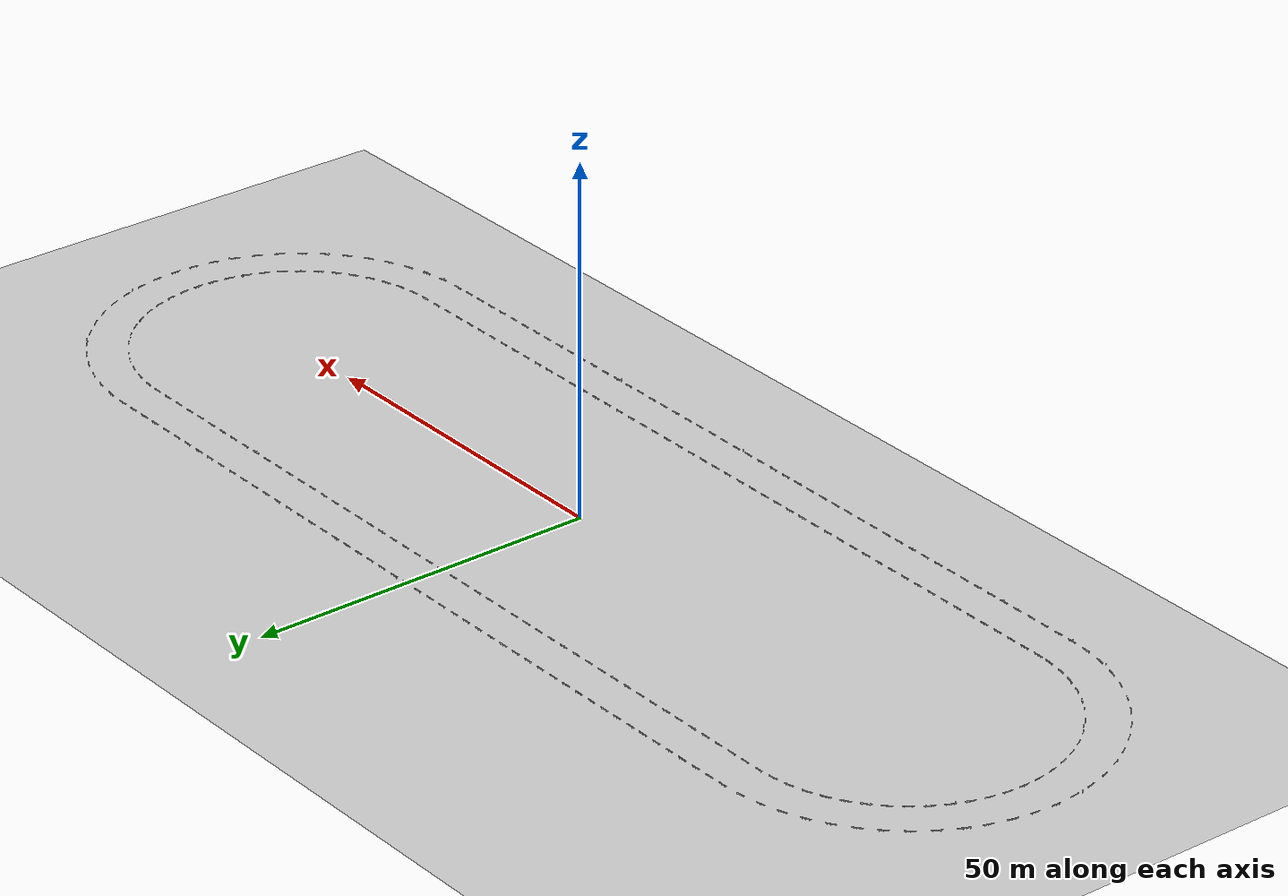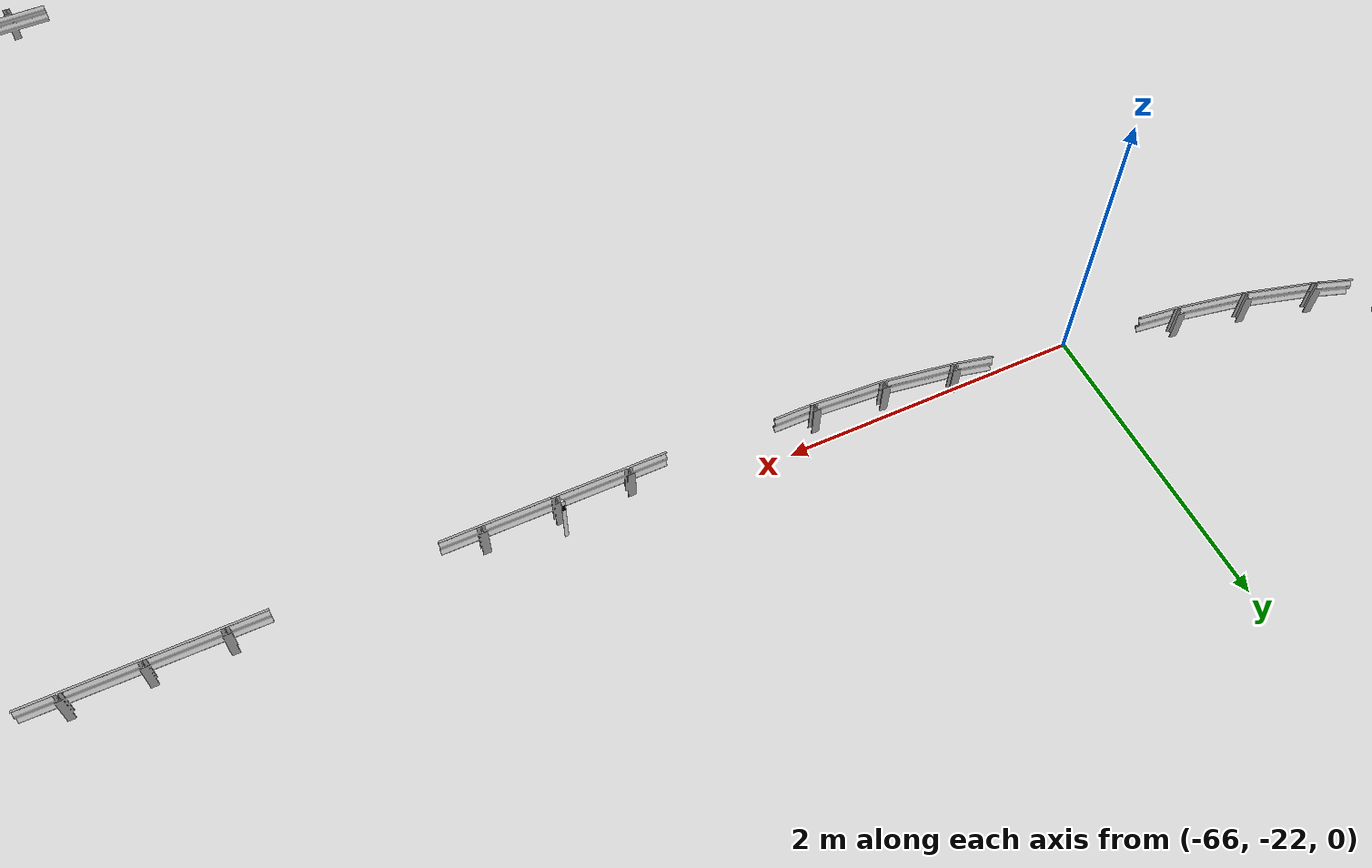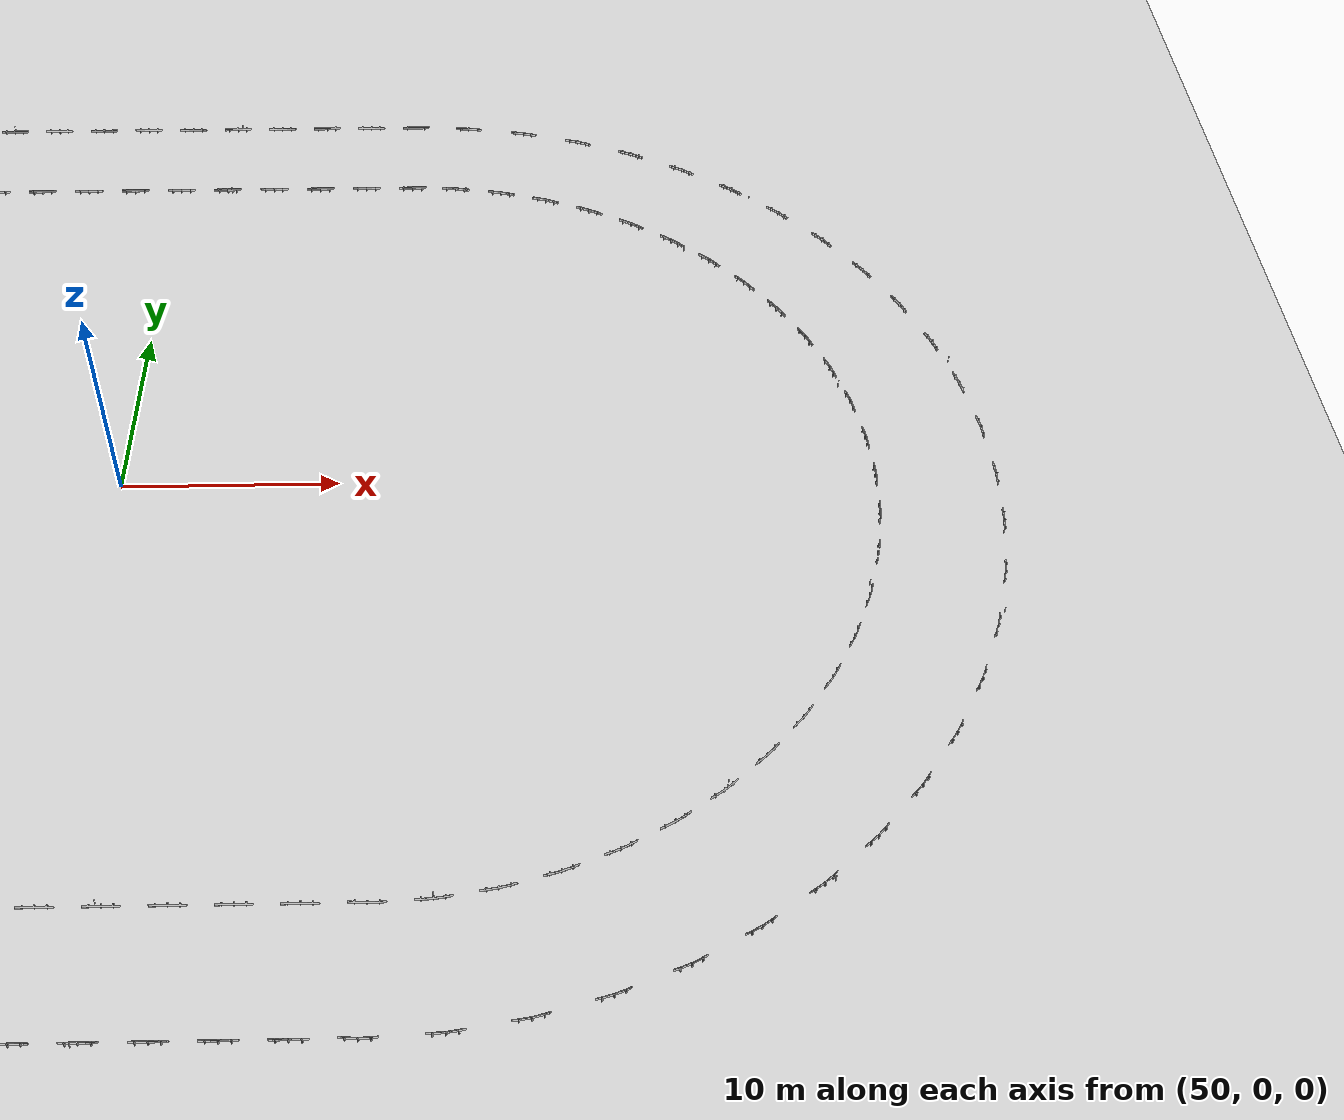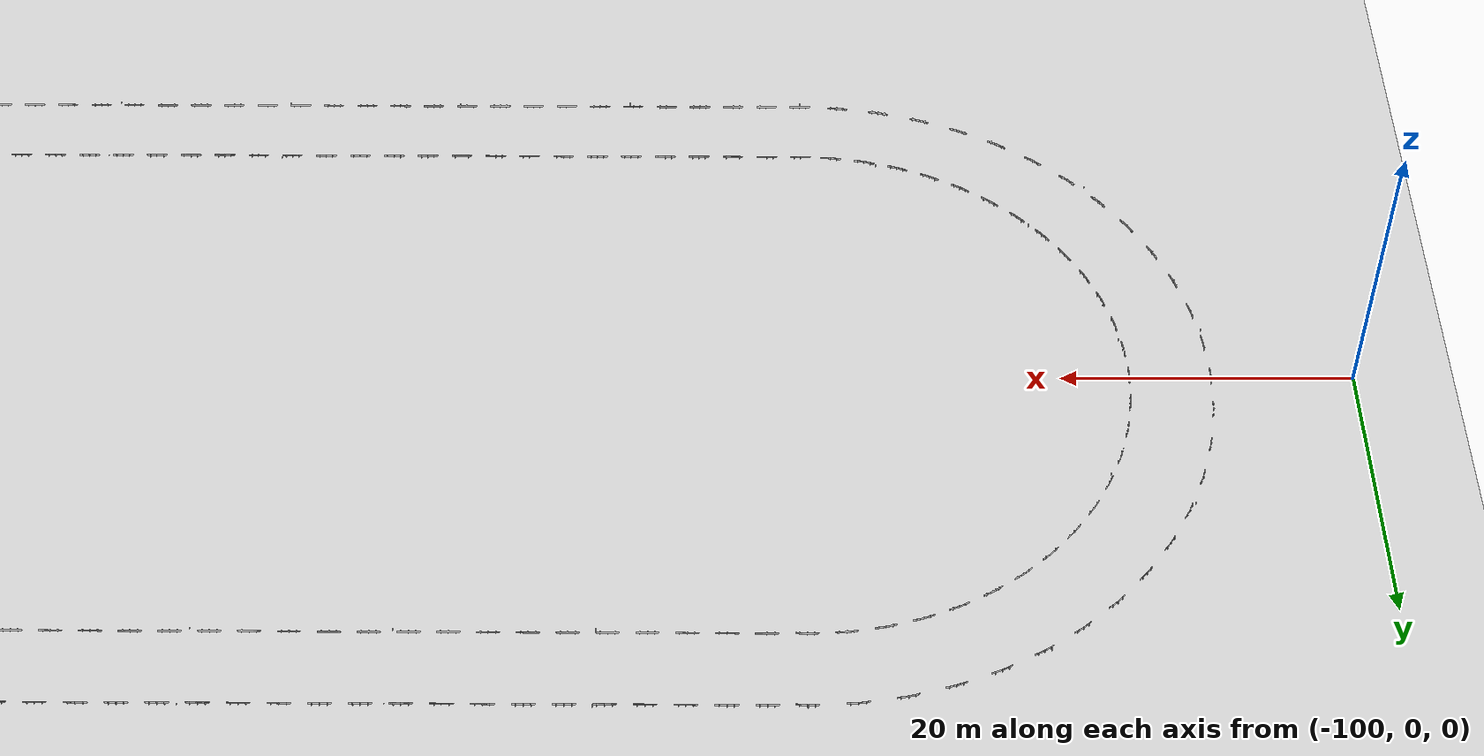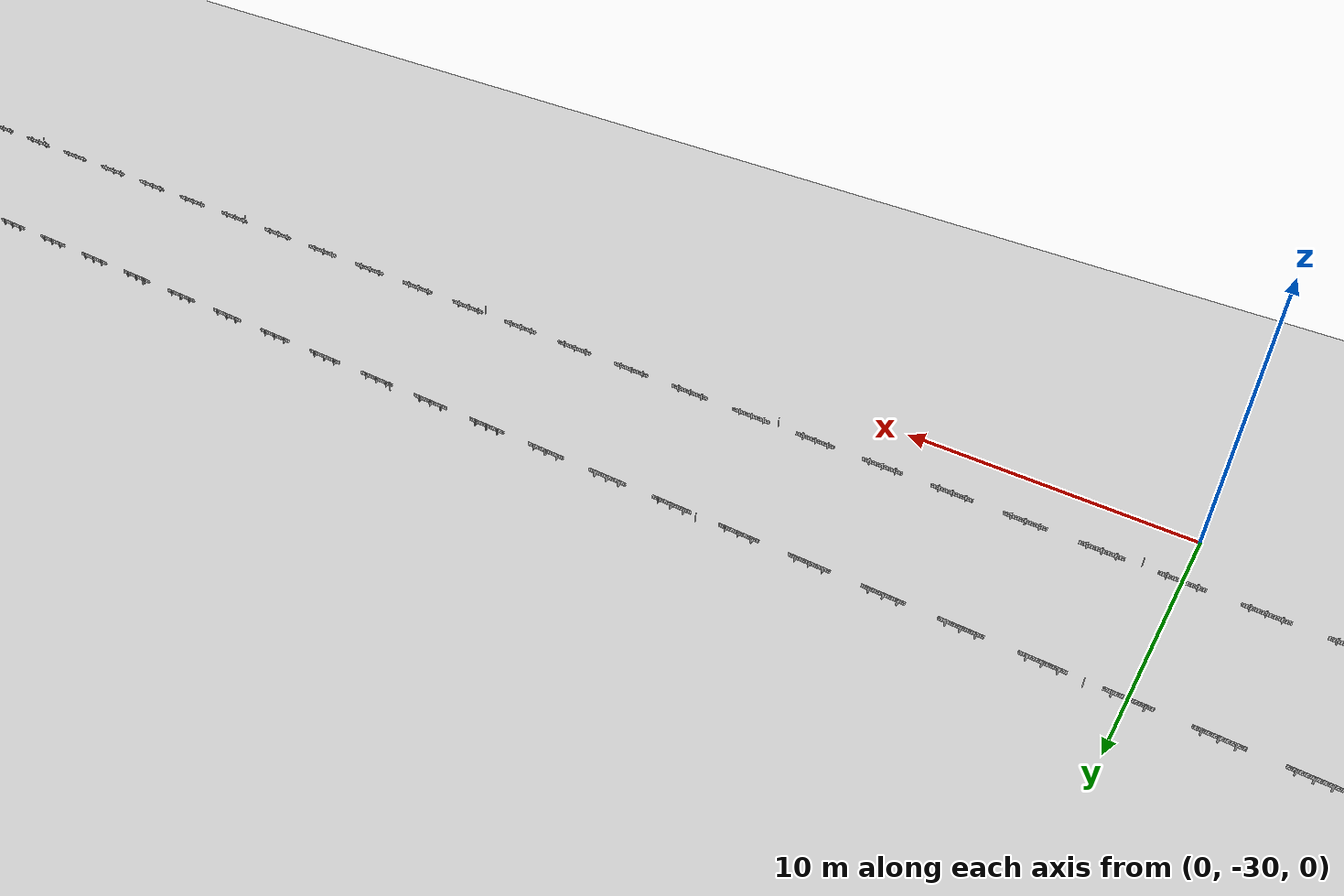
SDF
<sdf version="1.7">
 <world name="default">
  <light name="sun" type="directional">
   <pose>0 0 10 0 -0 0</pose>
   <diffuse>0.8 0.8 0.8 1</diffuse>
   <specular>0.2 0.2 0.2 1</specular>
   <attenuation>
    <range>1000</range>
    <constant>0.9</constant>
    <linear>0.01</linear>
    <quadratic>0.001</quadratic>
   </attenuation>
   <direction>-0.5 0.1 -0.9</direction>
   <spot><inner_angle>0</inner_angle><outer_angle>0</outer_angle><falloff>0</falloff></spot>
  </light>
  <gravity>0 0 -9.8</gravity>
  <magnetic_field>6e-06 2.3e-05 -4.2e-05</magnetic_field>
  <atmosphere type="adiabatic"/>
  <physics type="ode">
   <max_step_size>0.001</max_step_size>
   <real_time_factor>1</real_time_factor>
   <real_time_update_rate>1000</real_time_update_rate>
  </physics>
  <scene><ambient>0.4 0.4 0.4 1</ambient><background>0.7 0.7 0.7 1</background><shadows>1</shadows></scene>
  <spherical_coordinates>
   <surface_model>EARTH_WGS84</surface_model>
   <latitude_deg>0</latitude_deg>
   <longitude_deg>0</longitude_deg>
   <elevation>0</elevation>
   <heading_deg>0</heading_deg>
  </spherical_coordinates>
  <model name="highway">
   <static>1</static>
   <link name="link">
    <collision name="collision">
     <geometry><plane><normal>0 0 1</normal><size>300 300</size></plane></geometry>
     <surface><friction><ode><mu>100</mu><mu2>50</mu2></ode></friction></surface>
    </collision>
    <visual name="visual">
     <cast_shadows>0</cast_shadows>
     <geometry><plane><normal>0 0 1</normal><size>370 370</size></plane></geometry>
     <material>
      <script>
       <uri>model://highway/materials/scripts/highway.material</uri>
       <uri>model://highway/materials/textures</uri>
       <name>Highway/Image</name>
      </script>
     </material>
    </visual>
   </link>
  </model>
  <model name="guardrail_inner_curve_0.0">
   <link name="link">
    <visual name="visual">
     <geometry>
      <mesh>
       <uri>model://guardrail_inner_curve/meshes/guardrail_inner_curve.dae</uri>
       <scale>0.0025 0.0025 0.0025</scale>
      </mesh>
     </geometry>
    </visual>
    <collision name="collision">
     <geometry>
      <mesh>
       <uri>model://guardrail_inner_curve/meshes/guardrail_inner_curve.dae</uri>
       <scale>0.0025 0.0025 0.0025</scale>
      </mesh>
     </geometry>
    </collision>
   </link>
   <static>1</static>
   <pose>62.5 -22.1875 0 0 -0 3.14159</pose>
  </model>
  <model name="guardrail_inner_curve_1.0">
   <link name="link">
    <visual name="visual">
     <geometry>
      <mesh>
       <uri>model://guardrail_inner_curve/meshes/guardrail_inner_curve.dae</uri>
       <scale>0.0025 0.0025 0.0025</scale>
      </mesh>
     </geometry>
    </visual>
    <collision name="collision">
     <geometry>
      <mesh>
       <uri>model://guardrail_inner_curve/meshes/guardrail_inner_curve.dae</uri>
       <scale>0.0025 0.0025 0.0025</scale>
      </mesh>
     </geometry>
    </collision>
   </link>
   <static>1</static>
   <pose>64.9947 -22.0468 0 0 0 -3.02892</pose>
  </model>
  <model name="guardrail_inner_curve_2.0">
   <link name="link">
    <visual name="visual">
     <geometry>
      <mesh>
       <uri>model://guardrail_inner_curve/meshes/guardrail_inner_curve.dae</uri>
       <scale>0.0025 0.0025 0.0025</scale>
      </mesh>
     </geometry>
    </visual>
    <collision name="collision">
     <geometry>
      <mesh>
       <uri>model://guardrail_inner_curve/meshes/guardrail_inner_curve.dae</uri>
       <scale>0.0025 0.0025 0.0025</scale>
      </mesh>
     </geometry>
    </collision>
   </link>
   <static>1</static>
   <pose>67.4578 -21.6265 0 0 0 -2.91624</pose>
  </model>
  <model name="guardrail_inner_curve_3.0">
   <link name="link">
    <visual name="visual">
     <geometry>
      <mesh>
       <uri>model://guardrail_inner_curve/meshes/guardrail_inner_curve.dae</uri>
       <scale>0.0025 0.0025 0.0025</scale>
      </mesh>
     </geometry>
    </visual>
    <collision name="collision">
     <geometry>
      <mesh>
       <uri>model://guardrail_inner_curve/meshes/guardrail_inner_curve.dae</uri>
       <scale>0.0025 0.0025 0.0025</scale>
      </mesh>
     </geometry>
    </collision>
   </link>
   <static>1</static>
   <pose>69.858 -20.9319 0 0 0 -2.80356</pose>
  </model>
  <model name="guardrail_inner_curve_4.0">
   <link name="link">
    <visual name="visual">
     <geometry>
      <mesh>
       <uri>model://guardrail_inner_curve/meshes/guardrail_inner_curve.dae</uri>
       <scale>0.0025 0.0025 0.0025</scale>
      </mesh>
     </geometry>
    </visual>
    <collision name="collision">
     <geometry>
      <mesh>
       <uri>model://guardrail_inner_curve/meshes/guardrail_inner_curve.dae</uri>
       <scale>0.0025 0.0025 0.0025</scale>
      </mesh>
     </geometry>
    </collision>
   </link>
   <static>1</static>
   <pose>72.1649 -19.9719 0 0 0 -2.69089</pose>
  </model>
  <model name="guardrail_inner_curve_5.0">
   <link name="link">
    <visual name="visual">
     <geometry>
      <mesh>
       <uri>model://guardrail_inner_curve/meshes/guardrail_inner_curve.dae</uri>
       <scale>0.0025 0.0025 0.0025</scale>
      </mesh>
     </geometry>
    </visual>
    <collision name="collision">
     <geometry>
      <mesh>
       <uri>model://guardrail_inner_curve/meshes/guardrail_inner_curve.dae</uri>
       <scale>0.0025 0.0025 0.0025</scale>
      </mesh>
     </geometry>
    </collision>
   </link>
   <static>1</static>
   <pose>74.3492 -18.7585 0 0 0 -2.57821</pose>
  </model>
  <model name="guardrail_inner_curve_6.0">
   <link name="link">
    <visual name="visual">
     <geometry>
      <mesh>
       <uri>model://guardrail_inner_curve/meshes/guardrail_inner_curve.dae</uri>
       <scale>0.0025 0.0025 0.0025</scale>
      </mesh>
     </geometry>
    </visual>
    <collision name="collision">
     <geometry>
      <mesh>
       <uri>model://guardrail_inner_curve/meshes/guardrail_inner_curve.dae</uri>
       <scale>0.0025 0.0025 0.0025</scale>
      </mesh>
     </geometry>
    </collision>
   </link>
   <static>1</static>
   <pose>76.3832 -17.3073 0 0 0 -2.46554</pose>
  </model>
  <model name="guardrail_inner_curve_7.0">
   <link name="link">
    <visual name="visual">
     <geometry>
      <mesh>
       <uri>model://guardrail_inner_curve/meshes/guardrail_inner_curve.dae</uri>
       <scale>0.0025 0.0025 0.0025</scale>
      </mesh>
     </geometry>
    </visual>
    <collision name="collision">
     <geometry>
      <mesh>
       <uri>model://guardrail_inner_curve/meshes/guardrail_inner_curve.dae</uri>
       <scale>0.0025 0.0025 0.0025</scale>
      </mesh>
     </geometry>
    </collision>
   </link>
   <static>1</static>
   <pose>78.2412 -15.6365 0 0 0 -2.35286</pose>
  </model>
  <model name="guardrail_inner_curve_8.0">
   <link name="link">
    <visual name="visual">
     <geometry>
      <mesh>
       <uri>model://guardrail_inner_curve/meshes/guardrail_inner_curve.dae</uri>
       <scale>0.0025 0.0025 0.0025</scale>
      </mesh>
     </geometry>
    </visual>
    <collision name="collision">
     <geometry>
      <mesh>
       <uri>model://guardrail_inner_curve/meshes/guardrail_inner_curve.dae</uri>
       <scale>0.0025 0.0025 0.0025</scale>
      </mesh>
     </geometry>
    </collision>
   </link>
   <static>1</static>
   <pose>79.8995 -13.7675 0 0 0 -2.24018</pose>
  </model>
  <model name="guardrail_inner_curve_9.0">
   <link name="link">
    <visual name="visual">
     <geometry>
      <mesh>
       <uri>model://guardrail_inner_curve/meshes/guardrail_inner_curve.dae</uri>
       <scale>0.0025 0.0025 0.0025</scale>
      </mesh>
     </geometry>
    </visual>
    <collision name="collision">
     <geometry>
      <mesh>
       <uri>model://guardrail_inner_curve/meshes/guardrail_inner_curve.dae</uri>
       <scale>0.0025 0.0025 0.0025</scale>
      </mesh>
     </geometry>
    </collision>
   </link>
   <static>1</static>
   <pose>81.3371 -11.7238 0 0 0 -2.12751</pose>
  </model>
  <model name="guardrail_inner_curve_10.0">
   <link name="link">
    <visual name="visual">
     <geometry>
      <mesh>
       <uri>model://guardrail_inner_curve/meshes/guardrail_inner_curve.dae</uri>
       <scale>0.0025 0.0025 0.0025</scale>
      </mesh>
     </geometry>
    </visual>
    <collision name="collision">
     <geometry>
      <mesh>
       <uri>model://guardrail_inner_curve/meshes/guardrail_inner_curve.dae</uri>
       <scale>0.0025 0.0025 0.0025</scale>
      </mesh>
     </geometry>
    </collision>
   </link>
   <static>1</static>
   <pose>82.5359 -9.53147 0 0 0 -2.01483</pose>
  </model>
  <model name="guardrail_inner_curve_11.0">
   <link name="link">
    <visual name="visual">
     <geometry>
      <mesh>
       <uri>model://guardrail_inner_curve/meshes/guardrail_inner_curve.dae</uri>
       <scale>0.0025 0.0025 0.0025</scale>
      </mesh>
     </geometry>
    </visual>
    <collision name="collision">
     <geometry>
      <mesh>
       <uri>model://guardrail_inner_curve/meshes/guardrail_inner_curve.dae</uri>
       <scale>0.0025 0.0025 0.0025</scale>
      </mesh>
     </geometry>
    </collision>
   </link>
   <static>1</static>
   <pose>83.4805 -7.21824 0 0 0 -1.90216</pose>
  </model>
  <model name="guardrail_inner_curve_12.0">
   <link name="link">
    <visual name="visual">
     <geometry>
      <mesh>
       <uri>model://guardrail_inner_curve/meshes/guardrail_inner_curve.dae</uri>
       <scale>0.0025 0.0025 0.0025</scale>
      </mesh>
     </geometry>
    </visual>
    <collision name="collision">
     <geometry>
      <mesh>
       <uri>model://guardrail_inner_curve/meshes/guardrail_inner_curve.dae</uri>
       <scale>0.0025 0.0025 0.0025</scale>
      </mesh>
     </geometry>
    </collision>
   </link>
   <static>1</static>
   <pose>84.1591 -4.81346 0 0 0 -1.78948</pose>
  </model>
  <model name="guardrail_inner_curve_13.0">
   <link name="link">
    <visual name="visual">
     <geometry>
      <mesh>
       <uri>model://guardrail_inner_curve/meshes/guardrail_inner_curve.dae</uri>
       <scale>0.0025 0.0025 0.0025</scale>
      </mesh>
     </geometry>
    </visual>
    <collision name="collision">
     <geometry>
      <mesh>
       <uri>model://guardrail_inner_curve/meshes/guardrail_inner_curve.dae</uri>
       <scale>0.0025 0.0025 0.0025</scale>
      </mesh>
     </geometry>
    </collision>
   </link>
   <static>1</static>
   <pose>84.5629 -2.34764 0 0 0 -1.6768</pose>
  </model>
  <model name="guardrail_inner_curve_14.0">
   <link name="link">
    <visual name="visual">
     <geometry>
      <mesh>
       <uri>model://guardrail_inner_curve/meshes/guardrail_inner_curve.dae</uri>
       <scale>0.0025 0.0025 0.0025</scale>
      </mesh>
     </geometry>
    </visual>
    <collision name="collision">
     <geometry>
      <mesh>
       <uri>model://guardrail_inner_curve/meshes/guardrail_inner_curve.dae</uri>
       <scale>0.0025 0.0025 0.0025</scale>
      </mesh>
     </geometry>
    </collision>
   </link>
   <static>1</static>
   <pose>84.6875 0 0 0 0 -1.5708</pose>
  </model>
  <model name="guardrail_inner_curve_15.0">
   <link name="link">
    <visual name="visual">
     <geometry>
      <mesh>
       <uri>model://guardrail_inner_curve/meshes/guardrail_inner_curve.dae</uri>
       <scale>0.0025 0.0025 0.0025</scale>
      </mesh>
     </geometry>
    </visual>
    <collision name="collision">
     <geometry>
      <mesh>
       <uri>model://guardrail_inner_curve/meshes/guardrail_inner_curve.dae</uri>
       <scale>0.0025 0.0025 0.0025</scale>
      </mesh>
     </geometry>
    </collision>
   </link>
   <static>1</static>
   <pose>84.5468 2.49471 0 0 0 -1.45812</pose>
  </model>
  <model name="guardrail_inner_curve_16.0">
   <link name="link">
    <visual name="visual">
     <geometry>
      <mesh>
       <uri>model://guardrail_inner_curve/meshes/guardrail_inner_curve.dae</uri>
       <scale>0.0025 0.0025 0.0025</scale>
      </mesh>
     </geometry>
    </visual>
    <collision name="collision">
     <geometry>
      <mesh>
       <uri>model://guardrail_inner_curve/meshes/guardrail_inner_curve.dae</uri>
       <scale>0.0025 0.0025 0.0025</scale>
      </mesh>
     </geometry>
    </collision>
   </link>
   <static>1</static>
   <pose>84.1265 4.95779 0 0 0 -1.34544</pose>
  </model>
  <model name="guardrail_inner_curve_17.0">
   <link name="link">
    <visual name="visual">
     <geometry>
      <mesh>
       <uri>model://guardrail_inner_curve/meshes/guardrail_inner_curve.dae</uri>
       <scale>0.0025 0.0025 0.0025</scale>
      </mesh>
     </geometry>
    </visual>
    <collision name="collision">
     <geometry>
      <mesh>
       <uri>model://guardrail_inner_curve/meshes/guardrail_inner_curve.dae</uri>
       <scale>0.0025 0.0025 0.0025</scale>
      </mesh>
     </geometry>
    </collision>
   </link>
   <static>1</static>
   <pose>83.4319 7.35798 0 0 0 -1.23277</pose>
  </model>
  <model name="guardrail_inner_curve_18.0">
   <link name="link">
    <visual name="visual">
     <geometry>
      <mesh>
       <uri>model://guardrail_inner_curve/meshes/guardrail_inner_curve.dae</uri>
       <scale>0.0025 0.0025 0.0025</scale>
      </mesh>
     </geometry>
    </visual>
    <collision name="collision">
     <geometry>
      <mesh>
       <uri>model://guardrail_inner_curve/meshes/guardrail_inner_curve.dae</uri>
       <scale>0.0025 0.0025 0.0025</scale>
      </mesh>
     </geometry>
    </collision>
   </link>
   <static>1</static>
   <pose>82.4719 9.66486 0 0 0 -1.12009</pose>
  </model>
  <model name="guardrail_inner_curve_19.0">
   <link name="link">
    <visual name="visual">
     <geometry>
      <mesh>
       <uri>model://guardrail_inner_curve/meshes/guardrail_inner_curve.dae</uri>
       <scale>0.0025 0.0025 0.0025</scale>
      </mesh>
     </geometry>
    </visual>
    <collision name="collision">
     <geometry>
      <mesh>
       <uri>model://guardrail_inner_curve/meshes/guardrail_inner_curve.dae</uri>
       <scale>0.0025 0.0025 0.0025</scale>
      </mesh>
     </geometry>
    </collision>
   </link>
   <static>1</static>
   <pose>81.2585 11.8492 0 0 0 -1.00742</pose>
  </model>
  <model name="guardrail_inner_curve_20.0">
   <link name="link">
    <visual name="visual">
     <geometry>
      <mesh>
       <uri>model://guardrail_inner_curve/meshes/guardrail_inner_curve.dae</uri>
       <scale>0.0025 0.0025 0.0025</scale>
      </mesh>
     </geometry>
    </visual>
    <collision name="collision">
     <geometry>
      <mesh>
       <uri>model://guardrail_inner_curve/meshes/guardrail_inner_curve.dae</uri>
       <scale>0.0025 0.0025 0.0025</scale>
      </mesh>
     </geometry>
    </collision>
   </link>
   <static>1</static>
   <pose>79.8073 13.8832 0 0 0 -0.89474</pose>
  </model>
  <model name="guardrail_inner_curve_21.0">
   <link name="link">
    <visual name="visual">
     <geometry>
      <mesh>
       <uri>model://guardrail_inner_curve/meshes/guardrail_inner_curve.dae</uri>
       <scale>0.0025 0.0025 0.0025</scale>
      </mesh>
     </geometry>
    </visual>
    <collision name="collision">
     <geometry>
      <mesh>
       <uri>model://guardrail_inner_curve/meshes/guardrail_inner_curve.dae</uri>
       <scale>0.0025 0.0025 0.0025</scale>
      </mesh>
     </geometry>
    </collision>
   </link>
   <static>1</static>
   <pose>78.1365 15.7412 0 0 0 -0.782064</pose>
  </model>
  <model name="guardrail_inner_curve_22.0">
   <link name="link">
    <visual name="visual">
     <geometry>
      <mesh>
       <uri>model://guardrail_inner_curve/meshes/guardrail_inner_curve.dae</uri>
       <scale>0.0025 0.0025 0.0025</scale>
      </mesh>
     </geometry>
    </visual>
    <collision name="collision">
     <geometry>
      <mesh>
       <uri>model://guardrail_inner_curve/meshes/guardrail_inner_curve.dae</uri>
       <scale>0.0025 0.0025 0.0025</scale>
      </mesh>
     </geometry>
    </collision>
   </link>
   <static>1</static>
   <pose>76.2675 17.3995 0 0 0 -0.669388</pose>
  </model>
  <model name="guardrail_inner_curve_23.0">
   <link name="link">
    <visual name="visual">
     <geometry>
      <mesh>
       <uri>model://guardrail_inner_curve/meshes/guardrail_inner_curve.dae</uri>
       <scale>0.0025 0.0025 0.0025</scale>
      </mesh>
     </geometry>
    </visual>
    <collision name="collision">
     <geometry>
      <mesh>
       <uri>model://guardrail_inner_curve/meshes/guardrail_inner_curve.dae</uri>
       <scale>0.0025 0.0025 0.0025</scale>
      </mesh>
     </geometry>
    </collision>
   </link>
   <static>1</static>
   <pose>74.2238 18.8371 0 0 0 -0.556712</pose>
  </model>
  <model name="guardrail_inner_curve_24.0">
   <link name="link">
    <visual name="visual">
     <geometry>
      <mesh>
       <uri>model://guardrail_inner_curve/meshes/guardrail_inner_curve.dae</uri>
       <scale>0.0025 0.0025 0.0025</scale>
      </mesh>
     </geometry>
    </visual>
    <collision name="collision">
     <geometry>
      <mesh>
       <uri>model://guardrail_inner_curve/meshes/guardrail_inner_curve.dae</uri>
       <scale>0.0025 0.0025 0.0025</scale>
      </mesh>
     </geometry>
    </collision>
   </link>
   <static>1</static>
   <pose>72.0315 20.0359 0 0 0 -0.444036</pose>
  </model>
  <model name="guardrail_inner_curve_25.0">
   <link name="link">
    <visual name="visual">
     <geometry>
      <mesh>
       <uri>model://guardrail_inner_curve/meshes/guardrail_inner_curve.dae</uri>
       <scale>0.0025 0.0025 0.0025</scale>
      </mesh>
     </geometry>
    </visual>
    <collision name="collision">
     <geometry>
      <mesh>
       <uri>model://guardrail_inner_curve/meshes/guardrail_inner_curve.dae</uri>
       <scale>0.0025 0.0025 0.0025</scale>
      </mesh>
     </geometry>
    </collision>
   </link>
   <static>1</static>
   <pose>69.7182 20.9805 0 0 0 -0.33136</pose>
  </model>
  <model name="guardrail_inner_curve_26.0">
   <link name="link">
    <visual name="visual">
     <geometry>
      <mesh>
       <uri>model://guardrail_inner_curve/meshes/guardrail_inner_curve.dae</uri>
       <scale>0.0025 0.0025 0.0025</scale>
      </mesh>
     </geometry>
    </visual>
    <collision name="collision">
     <geometry>
      <mesh>
       <uri>model://guardrail_inner_curve/meshes/guardrail_inner_curve.dae</uri>
       <scale>0.0025 0.0025 0.0025</scale>
      </mesh>
     </geometry>
    </collision>
   </link>
   <static>1</static>
   <pose>67.3135 21.6591 0 0 0 -0.218684</pose>
  </model>
  <model name="guardrail_inner_curve_27.0">
   <link name="link">
    <visual name="visual">
     <geometry>
      <mesh>
       <uri>model://guardrail_inner_curve/meshes/guardrail_inner_curve.dae</uri>
       <scale>0.0025 0.0025 0.0025</scale>
      </mesh>
     </geometry>
    </visual>
    <collision name="collision">
     <geometry>
      <mesh>
       <uri>model://guardrail_inner_curve/meshes/guardrail_inner_curve.dae</uri>
       <scale>0.0025 0.0025 0.0025</scale>
      </mesh>
     </geometry>
    </collision>
   </link>
   <static>1</static>
   <pose>64.8476 22.0629 0 0 0 -0.106008</pose>
  </model>
  <model name="guardrail_inner_curve_28.0">
   <link name="link">
    <visual name="visual">
     <geometry>
      <mesh>
       <uri>model://guardrail_inner_curve/meshes/guardrail_inner_curve.dae</uri>
       <scale>0.0025 0.0025 0.0025</scale>
      </mesh>
     </geometry>
    </visual>
    <collision name="collision">
     <geometry>
      <mesh>
       <uri>model://guardrail_inner_curve/meshes/guardrail_inner_curve.dae</uri>
       <scale>0.0025 0.0025 0.0025</scale>
      </mesh>
     </geometry>
    </collision>
   </link>
   <static>1</static>
   <pose>-62.5 22.1875 0 0 -0 0</pose>
  </model>
  <model name="guardrail_inner_curve_29.0">
   <link name="link">
    <visual name="visual">
     <geometry>
      <mesh>
       <uri>model://guardrail_inner_curve/meshes/guardrail_inner_curve.dae</uri>
       <scale>0.0025 0.0025 0.0025</scale>
      </mesh>
     </geometry>
    </visual>
    <collision name="collision">
     <geometry>
      <mesh>
       <uri>model://guardrail_inner_curve/meshes/guardrail_inner_curve.dae</uri>
       <scale>0.0025 0.0025 0.0025</scale>
      </mesh>
     </geometry>
    </collision>
   </link>
   <static>1</static>
   <pose>-64.9947 22.0468 0 0 -0 0.112676</pose>
  </model>
  <model name="guardrail_inner_curve_30.0">
   <link name="link">
    <visual name="visual">
     <geometry>
      <mesh>
       <uri>model://guardrail_inner_curve/meshes/guardrail_inner_curve.dae</uri>
       <scale>0.0025 0.0025 0.0025</scale>
      </mesh>
     </geometry>
    </visual>
    <collision name="collision">
     <geometry>
      <mesh>
       <uri>model://guardrail_inner_curve/meshes/guardrail_inner_curve.dae</uri>
       <scale>0.0025 0.0025 0.0025</scale>
      </mesh>
     </geometry>
    </collision>
   </link>
   <static>1</static>
   <pose>-67.4578 21.6265 0 0 -0 0.225352</pose>
  </model>
  <model name="guardrail_inner_curve_31.0">
   <link name="link">
    <visual name="visual">
     <geometry>
      <mesh>
       <uri>model://guardrail_inner_curve/meshes/guardrail_inner_curve.dae</uri>
       <scale>0.0025 0.0025 0.0025</scale>
      </mesh>
     </geometry>
    </visual>
    <collision name="collision">
     <geometry>
      <mesh>
       <uri>model://guardrail_inner_curve/meshes/guardrail_inner_curve.dae</uri>
       <scale>0.0025 0.0025 0.0025</scale>
      </mesh>
     </geometry>
    </collision>
   </link>
   <static>1</static>
   <pose>-69.858 20.9319 0 0 -0 0.338028</pose>
  </model>
  <model name="guardrail_inner_curve_32.0">
   <link name="link">
    <visual name="visual">
     <geometry>
      <mesh>
       <uri>model://guardrail_inner_curve/meshes/guardrail_inner_curve.dae</uri>
       <scale>0.0025 0.0025 0.0025</scale>
      </mesh>
     </geometry>
    </visual>
    <collision name="collision">
     <geometry>
      <mesh>
       <uri>model://guardrail_inner_curve/meshes/guardrail_inner_curve.dae</uri>
       <scale>0.0025 0.0025 0.0025</scale>
      </mesh>
     </geometry>
    </collision>
   </link>
   <static>1</static>
   <pose>-72.1649 19.9719 0 0 -0 0.450704</pose>
  </model>
  <model name="guardrail_inner_curve_33.0">
   <link name="link">
    <visual name="visual">
     <geometry>
      <mesh>
       <uri>model://guardrail_inner_curve/meshes/guardrail_inner_curve.dae</uri>
       <scale>0.0025 0.0025 0.0025</scale>
      </mesh>
     </geometry>
    </visual>
    <collision name="collision">
     <geometry>
      <mesh>
       <uri>model://guardrail_inner_curve/meshes/guardrail_inner_curve.dae</uri>
       <scale>0.0025 0.0025 0.0025</scale>
      </mesh>
     </geometry>
    </collision>
   </link>
   <static>1</static>
   <pose>-74.3492 18.7585 0 0 -0 0.56338</pose>
  </model>
  <model name="guardrail_inner_curve_34.0">
   <link name="link">
    <visual name="visual">
     <geometry>
      <mesh>
       <uri>model://guardrail_inner_curve/meshes/guardrail_inner_curve.dae</uri>
       <scale>0.0025 0.0025 0.0025</scale>
      </mesh>
     </geometry>
    </visual>
    <collision name="collision">
     <geometry>
      <mesh>
       <uri>model://guardrail_inner_curve/meshes/guardrail_inner_curve.dae</uri>
       <scale>0.0025 0.0025 0.0025</scale>
      </mesh>
     </geometry>
    </collision>
   </link>
   <static>1</static>
   <pose>-76.3832 17.3073 0 0 -0 0.676056</pose>
  </model>
  <model name="guardrail_inner_curve_35.0">
   <link name="link">
    <visual name="visual">
     <geometry>
      <mesh>
       <uri>model://guardrail_inner_curve/meshes/guardrail_inner_curve.dae</uri>
       <scale>0.0025 0.0025 0.0025</scale>
      </mesh>
     </geometry>
    </visual>
    <collision name="collision">
     <geometry>
      <mesh>
       <uri>model://guardrail_inner_curve/meshes/guardrail_inner_curve.dae</uri>
       <scale>0.0025 0.0025 0.0025</scale>
      </mesh>
     </geometry>
    </collision>
   </link>
   <static>1</static>
   <pose>-78.2412 15.6365 0 0 -0 0.788732</pose>
  </model>
  <model name="guardrail_inner_curve_36.0">
   <link name="link">
    <visual name="visual">
     <geometry>
      <mesh>
       <uri>model://guardrail_inner_curve/meshes/guardrail_inner_curve.dae</uri>
       <scale>0.0025 0.0025 0.0025</scale>
      </mesh>
     </geometry>
    </visual>
    <collision name="collision">
     <geometry>
      <mesh>
       <uri>model://guardrail_inner_curve/meshes/guardrail_inner_curve.dae</uri>
       <scale>0.0025 0.0025 0.0025</scale>
      </mesh>
     </geometry>
    </collision>
   </link>
   <static>1</static>
   <pose>-79.8995 13.7675 0 0 -0 0.901408</pose>
  </model>
  <model name="guardrail_inner_curve_37.0">
   <link name="link">
    <visual name="visual">
     <geometry>
      <mesh>
       <uri>model://guardrail_inner_curve/meshes/guardrail_inner_curve.dae</uri>
       <scale>0.0025 0.0025 0.0025</scale>
      </mesh>
     </geometry>
    </visual>
    <collision name="collision">
     <geometry>
      <mesh>
       <uri>model://guardrail_inner_curve/meshes/guardrail_inner_curve.dae</uri>
       <scale>0.0025 0.0025 0.0025</scale>
      </mesh>
     </geometry>
    </collision>
   </link>
   <static>1</static>
   <pose>-81.3371 11.7238 0 0 -0 1.01408</pose>
  </model>
  <model name="guardrail_inner_curve_38.0">
   <link name="link">
    <visual name="visual">
     <geometry>
      <mesh>
       <uri>model://guardrail_inner_curve/meshes/guardrail_inner_curve.dae</uri>
       <scale>0.0025 0.0025 0.0025</scale>
      </mesh>
     </geometry>
    </visual>
    <collision name="collision">
     <geometry>
      <mesh>
       <uri>model://guardrail_inner_curve/meshes/guardrail_inner_curve.dae</uri>
       <scale>0.0025 0.0025 0.0025</scale>
      </mesh>
     </geometry>
    </collision>
   </link>
   <static>1</static>
   <pose>-82.5359 9.53147 0 0 -0 1.12676</pose>
  </model>
  <model name="guardrail_inner_curve_39.0">
   <link name="link">
    <visual name="visual">
     <geometry>
      <mesh>
       <uri>model://guardrail_inner_curve/meshes/guardrail_inner_curve.dae</uri>
       <scale>0.0025 0.0025 0.0025</scale>
      </mesh>
     </geometry>
    </visual>
    <collision name="collision">
     <geometry>
      <mesh>
       <uri>model://guardrail_inner_curve/meshes/guardrail_inner_curve.dae</uri>
       <scale>0.0025 0.0025 0.0025</scale>
      </mesh>
     </geometry>
    </collision>
   </link>
   <static>1</static>
   <pose>-83.4805 7.21824 0 0 -0 1.23944</pose>
  </model>
  <model name="guardrail_inner_curve_40.0">
   <link name="link">
    <visual name="visual">
     <geometry>
      <mesh>
       <uri>model://guardrail_inner_curve/meshes/guardrail_inner_curve.dae</uri>
       <scale>0.0025 0.0025 0.0025</scale>
      </mesh>
     </geometry>
    </visual>
    <collision name="collision">
     <geometry>
      <mesh>
       <uri>model://guardrail_inner_curve/meshes/guardrail_inner_curve.dae</uri>
       <scale>0.0025 0.0025 0.0025</scale>
      </mesh>
     </geometry>
    </collision>
   </link>
   <static>1</static>
   <pose>-84.1591 4.81346 0 0 -0 1.35211</pose>
  </model>
  <model name="guardrail_inner_curve_41.0">
   <link name="link">
    <visual name="visual">
     <geometry>
      <mesh>
       <uri>model://guardrail_inner_curve/meshes/guardrail_inner_curve.dae</uri>
       <scale>0.0025 0.0025 0.0025</scale>
      </mesh>
     </geometry>
    </visual>
    <collision name="collision">
     <geometry>
      <mesh>
       <uri>model://guardrail_inner_curve/meshes/guardrail_inner_curve.dae</uri>
       <scale>0.0025 0.0025 0.0025</scale>
      </mesh>
     </geometry>
    </collision>
   </link>
   <static>1</static>
   <pose>-84.5629 2.34764 0 0 -0 1.46479</pose>
  </model>
  <model name="guardrail_inner_curve_42.0">
   <link name="link">
    <visual name="visual">
     <geometry>
      <mesh>
       <uri>model://guardrail_inner_curve/meshes/guardrail_inner_curve.dae</uri>
       <scale>0.0025 0.0025 0.0025</scale>
      </mesh>
     </geometry>
    </visual>
    <collision name="collision">
     <geometry>
      <mesh>
       <uri>model://guardrail_inner_curve/meshes/guardrail_inner_curve.dae</uri>
       <scale>0.0025 0.0025 0.0025</scale>
      </mesh>
     </geometry>
    </collision>
   </link>
   <static>1</static>
   <pose>-84.687 -0.147955 0 0 -0 1.57746</pose>
  </model>
  <model name="guardrail_inner_curve_43.0">
   <link name="link">
    <visual name="visual">
     <geometry>
      <mesh>
       <uri>model://guardrail_inner_curve/meshes/guardrail_inner_curve.dae</uri>
       <scale>0.0025 0.0025 0.0025</scale>
      </mesh>
     </geometry>
    </visual>
    <collision name="collision">
     <geometry>
      <mesh>
       <uri>model://guardrail_inner_curve/meshes/guardrail_inner_curve.dae</uri>
       <scale>0.0025 0.0025 0.0025</scale>
      </mesh>
     </geometry>
    </collision>
   </link>
   <static>1</static>
   <pose>-84.5297 -2.64168 0 0 -0 1.69014</pose>
  </model>
  <model name="guardrail_inner_curve_44.0">
   <link name="link">
    <visual name="visual">
     <geometry>
      <mesh>
       <uri>model://guardrail_inner_curve/meshes/guardrail_inner_curve.dae</uri>
       <scale>0.0025 0.0025 0.0025</scale>
      </mesh>
     </geometry>
    </visual>
    <collision name="collision">
     <geometry>
      <mesh>
       <uri>model://guardrail_inner_curve/meshes/guardrail_inner_curve.dae</uri>
       <scale>0.0025 0.0025 0.0025</scale>
      </mesh>
     </geometry>
    </collision>
   </link>
   <static>1</static>
   <pose>-84.093 -5.10189 0 0 -0 1.80282</pose>
  </model>
  <model name="guardrail_inner_curve_45.0">
   <link name="link">
    <visual name="visual">
     <geometry>
      <mesh>
       <uri>model://guardrail_inner_curve/meshes/guardrail_inner_curve.dae</uri>
       <scale>0.0025 0.0025 0.0025</scale>
      </mesh>
     </geometry>
    </visual>
    <collision name="collision">
     <geometry>
      <mesh>
       <uri>model://guardrail_inner_curve/meshes/guardrail_inner_curve.dae</uri>
       <scale>0.0025 0.0025 0.0025</scale>
      </mesh>
     </geometry>
    </collision>
   </link>
   <static>1</static>
   <pose>-83.3824 -7.4974 0 0 -0 1.91549</pose>
  </model>
  <model name="guardrail_inner_curve_46.0">
   <link name="link">
    <visual name="visual">
     <geometry>
      <mesh>
       <uri>model://guardrail_inner_curve/meshes/guardrail_inner_curve.dae</uri>
       <scale>0.0025 0.0025 0.0025</scale>
      </mesh>
     </geometry>
    </visual>
    <collision name="collision">
     <geometry>
      <mesh>
       <uri>model://guardrail_inner_curve/meshes/guardrail_inner_curve.dae</uri>
       <scale>0.0025 0.0025 0.0025</scale>
      </mesh>
     </geometry>
    </collision>
   </link>
   <static>1</static>
   <pose>-82.407 -9.79783 0 0 -0 2.02817</pose>
  </model>
  <model name="guardrail_inner_curve_47.0">
   <link name="link">
    <visual name="visual">
     <geometry>
      <mesh>
       <uri>model://guardrail_inner_curve/meshes/guardrail_inner_curve.dae</uri>
       <scale>0.0025 0.0025 0.0025</scale>
      </mesh>
     </geometry>
    </visual>
    <collision name="collision">
     <geometry>
      <mesh>
       <uri>model://guardrail_inner_curve/meshes/guardrail_inner_curve.dae</uri>
       <scale>0.0025 0.0025 0.0025</scale>
      </mesh>
     </geometry>
    </collision>
   </link>
   <static>1</static>
   <pose>-81.1791 -11.974 0 0 -0 2.14085</pose>
  </model>
  <model name="guardrail_inner_curve_48.0">
   <link name="link">
    <visual name="visual">
     <geometry>
      <mesh>
       <uri>model://guardrail_inner_curve/meshes/guardrail_inner_curve.dae</uri>
       <scale>0.0025 0.0025 0.0025</scale>
      </mesh>
     </geometry>
    </visual>
    <collision name="collision">
     <geometry>
      <mesh>
       <uri>model://guardrail_inner_curve/meshes/guardrail_inner_curve.dae</uri>
       <scale>0.0025 0.0025 0.0025</scale>
      </mesh>
     </geometry>
    </collision>
   </link>
   <static>1</static>
   <pose>-79.7143 -13.9983 0 0 -0 2.25352</pose>
  </model>
  <model name="guardrail_inner_curve_49.0">
   <link name="link">
    <visual name="visual">
     <geometry>
      <mesh>
       <uri>model://guardrail_inner_curve/meshes/guardrail_inner_curve.dae</uri>
       <scale>0.0025 0.0025 0.0025</scale>
      </mesh>
     </geometry>
    </visual>
    <collision name="collision">
     <geometry>
      <mesh>
       <uri>model://guardrail_inner_curve/meshes/guardrail_inner_curve.dae</uri>
       <scale>0.0025 0.0025 0.0025</scale>
      </mesh>
     </geometry>
    </collision>
   </link>
   <static>1</static>
   <pose>-78.0312 -15.8451 0 0 -0 2.3662</pose>
  </model>
  <model name="guardrail_inner_curve_50.0">
   <link name="link">
    <visual name="visual">
     <geometry>
      <mesh>
       <uri>model://guardrail_inner_curve/meshes/guardrail_inner_curve.dae</uri>
       <scale>0.0025 0.0025 0.0025</scale>
      </mesh>
     </geometry>
    </visual>
    <collision name="collision">
     <geometry>
      <mesh>
       <uri>model://guardrail_inner_curve/meshes/guardrail_inner_curve.dae</uri>
       <scale>0.0025 0.0025 0.0025</scale>
      </mesh>
     </geometry>
    </collision>
   </link>
   <static>1</static>
   <pose>-76.1511 -17.4909 0 0 -0 2.47887</pose>
  </model>
  <model name="guardrail_inner_curve_51.0">
   <link name="link">
    <visual name="visual">
     <geometry>
      <mesh>
       <uri>model://guardrail_inner_curve/meshes/guardrail_inner_curve.dae</uri>
       <scale>0.0025 0.0025 0.0025</scale>
      </mesh>
     </geometry>
    </visual>
    <collision name="collision">
     <geometry>
      <mesh>
       <uri>model://guardrail_inner_curve/meshes/guardrail_inner_curve.dae</uri>
       <scale>0.0025 0.0025 0.0025</scale>
      </mesh>
     </geometry>
    </collision>
   </link>
   <static>1</static>
   <pose>-74.0979 -18.9149 0 0 -0 2.59155</pose>
  </model>
  <model name="guardrail_inner_curve_52.0">
   <link name="link">
    <visual name="visual">
     <geometry>
      <mesh>
       <uri>model://guardrail_inner_curve/meshes/guardrail_inner_curve.dae</uri>
       <scale>0.0025 0.0025 0.0025</scale>
      </mesh>
     </geometry>
    </visual>
    <collision name="collision">
     <geometry>
      <mesh>
       <uri>model://guardrail_inner_curve/meshes/guardrail_inner_curve.dae</uri>
       <scale>0.0025 0.0025 0.0025</scale>
      </mesh>
     </geometry>
    </collision>
   </link>
   <static>1</static>
   <pose>-71.8976 -20.099 0 0 -0 2.70423</pose>
  </model>
  <model name="guardrail_inner_curve_53.0">
   <link name="link">
    <visual name="visual">
     <geometry>
      <mesh>
       <uri>model://guardrail_inner_curve/meshes/guardrail_inner_curve.dae</uri>
       <scale>0.0025 0.0025 0.0025</scale>
      </mesh>
     </geometry>
    </visual>
    <collision name="collision">
     <geometry>
      <mesh>
       <uri>model://guardrail_inner_curve/meshes/guardrail_inner_curve.dae</uri>
       <scale>0.0025 0.0025 0.0025</scale>
      </mesh>
     </geometry>
    </collision>
   </link>
   <static>1</static>
   <pose>-69.5782 -21.0282 0 0 -0 2.8169</pose>
  </model>
  <model name="guardrail_inner_curve_54.0">
   <link name="link">
    <visual name="visual">
     <geometry>
      <mesh>
       <uri>model://guardrail_inner_curve/meshes/guardrail_inner_curve.dae</uri>
       <scale>0.0025 0.0025 0.0025</scale>
      </mesh>
     </geometry>
    </visual>
    <collision name="collision">
     <geometry>
      <mesh>
       <uri>model://guardrail_inner_curve/meshes/guardrail_inner_curve.dae</uri>
       <scale>0.0025 0.0025 0.0025</scale>
      </mesh>
     </geometry>
    </collision>
   </link>
   <static>1</static>
   <pose>-67.1689 -21.6907 0 0 -0 2.92958</pose>
  </model>
  <model name="guardrail_inner_curve_55.0">
   <link name="link">
    <visual name="visual">
     <geometry>
      <mesh>
       <uri>model://guardrail_inner_curve/meshes/guardrail_inner_curve.dae</uri>
       <scale>0.0025 0.0025 0.0025</scale>
      </mesh>
     </geometry>
    </visual>
    <collision name="collision">
     <geometry>
      <mesh>
       <uri>model://guardrail_inner_curve/meshes/guardrail_inner_curve.dae</uri>
       <scale>0.0025 0.0025 0.0025</scale>
      </mesh>
     </geometry>
    </collision>
   </link>
   <static>1</static>
   <pose>-64.7005 -22.0781 0 0 -0 3.04225</pose>
  </model>
  <model name="guardrail_straight_0.0">
   <link name="link">
    <visual name="visual">
     <geometry>
      <mesh>
       <uri>model://guardrail_straight/meshes/guardrail_straight.dae</uri>
       <scale>0.0025 0.0025 0.0025</scale>
      </mesh>
     </geometry>
    </visual>
    <collision name="collision">
     <geometry>
      <mesh>
       <uri>model://guardrail_straight/meshes/guardrail_straight.dae</uri>
       <scale>0.0025 0.0025 0.0025</scale>
      </mesh>
     </geometry>
    </collision>
   </link>
   <static>1</static>
   <pose>-62.5 -22.1875 0 0 -0 3.14159</pose>
  </model>
  <model name="guardrail_straight_0.1">
   <link name="link">
    <visual name="visual">
     <geometry>
      <mesh>
       <uri>model://guardrail_straight/meshes/guardrail_straight.dae</uri>
       <scale>0.0025 0.0025 0.0025</scale>
      </mesh>
     </geometry>
    </visual>
    <collision name="collision">
     <geometry>
      <mesh>
       <uri>model://guardrail_straight/meshes/guardrail_straight.dae</uri>
       <scale>0.0025 0.0025 0.0025</scale>
      </mesh>
     </geometry>
    </collision>
   </link>
   <static>1</static>
   <pose>-62.5 -27.8125 0 0 -0 0</pose>
  </model>
  <model name="guardrail_straight_1.0">
   <link name="link">
    <visual name="visual">
     <geometry>
      <mesh>
       <uri>model://guardrail_straight/meshes/guardrail_straight.dae</uri>
       <scale>0.0025 0.0025 0.0025</scale>
      </mesh>
     </geometry>
    </visual>
    <collision name="collision">
     <geometry>
      <mesh>
       <uri>model://guardrail_straight/meshes/guardrail_straight.dae</uri>
       <scale>0.0025 0.0025 0.0025</scale>
      </mesh>
     </geometry>
    </collision>
   </link>
   <static>1</static>
   <pose>-60 -22.1875 0 0 -0 3.14159</pose>
  </model>
  <model name="guardrail_straight_1.1">
   <link name="link">
    <visual name="visual">
     <geometry>
      <mesh>
       <uri>model://guardrail_straight/meshes/guardrail_straight.dae</uri>
       <scale>0.0025 0.0025 0.0025</scale>
      </mesh>
     </geometry>
    </visual>
    <collision name="collision">
     <geometry>
      <mesh>
       <uri>model://guardrail_straight/meshes/guardrail_straight.dae</uri>
       <scale>0.0025 0.0025 0.0025</scale>
      </mesh>
     </geometry>
    </collision>
   </link>
   <static>1</static>
   <pose>-60 -27.8125 0 0 -0 0</pose>
  </model>
  <model name="guardrail_straight_2.0">
   <link name="link">
    <visual name="visual">
     <geometry>
      <mesh>
       <uri>model://guardrail_straight/meshes/guardrail_straight.dae</uri>
       <scale>0.0025 0.0025 0.0025</scale>
      </mesh>
     </geometry>
    </visual>
    <collision name="collision">
     <geometry>
      <mesh>
       <uri>model://guardrail_straight/meshes/guardrail_straight.dae</uri>
       <scale>0.0025 0.0025 0.0025</scale>
      </mesh>
     </geometry>
    </collision>
   </link>
   <static>1</static>
   <pose>-57.5 -22.1875 0 0 -0 3.14159</pose>
  </model>
  <model name="guardrail_straight_2.1">
   <link name="link">
    <visual name="visual">
     <geometry>
      <mesh>
       <uri>model://guardrail_straight/meshes/guardrail_straight.dae</uri>
       <scale>0.0025 0.0025 0.0025</scale>
      </mesh>
     </geometry>
    </visual>
    <collision name="collision">
     <geometry>
      <mesh>
       <uri>model://guardrail_straight/meshes/guardrail_straight.dae</uri>
       <scale>0.0025 0.0025 0.0025</scale>
      </mesh>
     </geometry>
    </collision>
   </link>
   <static>1</static>
   <pose>-57.5 -27.8125 0 0 -0 0</pose>
  </model>
  <model name="guardrail_straight_3.0">
   <link name="link">
    <visual name="visual">
     <geometry>
      <mesh>
       <uri>model://guardrail_straight/meshes/guardrail_straight.dae</uri>
       <scale>0.0025 0.0025 0.0025</scale>
      </mesh>
     </geometry>
    </visual>
    <collision name="collision">
     <geometry>
      <mesh>
       <uri>model://guardrail_straight/meshes/guardrail_straight.dae</uri>
       <scale>0.0025 0.0025 0.0025</scale>
      </mesh>
     </geometry>
    </collision>
   </link>
   <static>1</static>
   <pose>-55 -22.1875 0 0 -0 3.14159</pose>
  </model>
  <model name="guardrail_straight_3.1">
   <link name="link">
    <visual name="visual">
     <geometry>
      <mesh>
       <uri>model://guardrail_straight/meshes/guardrail_straight.dae</uri>
       <scale>0.0025 0.0025 0.0025</scale>
      </mesh>
     </geometry>
    </visual>
    <collision name="collision">
     <geometry>
      <mesh>
       <uri>model://guardrail_straight/meshes/guardrail_straight.dae</uri>
       <scale>0.0025 0.0025 0.0025</scale>
      </mesh>
     </geometry>
    </collision>
   </link>
   <static>1</static>
   <pose>-55 -27.8125 0 0 -0 0</pose>
  </model>
  <model name="guardrail_straight_4.0">
   <link name="link">
    <visual name="visual">
     <geometry>
      <mesh>
       <uri>model://guardrail_straight/meshes/guardrail_straight.dae</uri>
       <scale>0.0025 0.0025 0.0025</scale>
      </mesh>
     </geometry>
    </visual>
    <collision name="collision">
     <geometry>
      <mesh>
       <uri>model://guardrail_straight/meshes/guardrail_straight.dae</uri>
       <scale>0.0025 0.0025 0.0025</scale>
      </mesh>
     </geometry>
    </collision>
   </link>
   <static>1</static>
   <pose>-52.5 -22.1875 0 0 -0 3.14159</pose>
  </model>
  <model name="guardrail_straight_4.1">
   <link name="link">
    <visual name="visual">
     <geometry>
      <mesh>
       <uri>model://guardrail_straight/meshes/guardrail_straight.dae</uri>
       <scale>0.0025 0.0025 0.0025</scale>
      </mesh>
     </geometry>
    </visual>
    <collision name="collision">
     <geometry>
      <mesh>
       <uri>model://guardrail_straight/meshes/guardrail_straight.dae</uri>
       <scale>0.0025 0.0025 0.0025</scale>
      </mesh>
     </geometry>
    </collision>
   </link>
   <static>1</static>
   <pose>-52.5 -27.8125 0 0 -0 0</pose>
  </model>
  <model name="guardrail_straight_5.0">
   <link name="link">
    <visual name="visual">
     <geometry>
      <mesh>
       <uri>model://guardrail_straight/meshes/guardrail_straight.dae</uri>
       <scale>0.0025 0.0025 0.0025</scale>
      </mesh>
     </geometry>
    </visual>
    <collision name="collision">
     <geometry>
      <mesh>
       <uri>model://guardrail_straight/meshes/guardrail_straight.dae</uri>
       <scale>0.0025 0.0025 0.0025</scale>
      </mesh>
     </geometry>
    </collision>
   </link>
   <static>1</static>
   <pose>-50 -22.1875 0 0 -0 3.14159</pose>
  </model>
  <model name="guardrail_straight_5.1">
   <link name="link">
    <visual name="visual">
     <geometry>
      <mesh>
       <uri>model://guardrail_straight/meshes/guardrail_straight.dae</uri>
       <scale>0.0025 0.0025 0.0025</scale>
      </mesh>
     </geometry>
    </visual>
    <collision name="collision">
     <geometry>
      <mesh>
       <uri>model://guardrail_straight/meshes/guardrail_straight.dae</uri>
       <scale>0.0025 0.0025 0.0025</scale>
      </mesh>
     </geometry>
    </collision>
   </link>
   <static>1</static>
   <pose>-50 -27.8125 0 0 -0 0</pose>
  </model>
  <model name="guardrail_straight_6.0">
   <link name="link">
    <visual name="visual">
     <geometry>
      <mesh>
       <uri>model://guardrail_straight/meshes/guardrail_straight.dae</uri>
       <scale>0.0025 0.0025 0.0025</scale>
      </mesh>
     </geometry>
    </visual>
    <collision name="collision">
     <geometry>
      <mesh>
       <uri>model://guardrail_straight/meshes/guardrail_straight.dae</uri>
       <scale>0.0025 0.0025 0.0025</scale>
      </mesh>
     </geometry>
    </collision>
   </link>
   <static>1</static>
   <pose>-47.5 -22.1875 0 0 -0 3.14159</pose>
  </model>
  <model name="guardrail_straight_6.1">
   <link name="link">
    <visual name="visual">
     <geometry>
      <mesh>
       <uri>model://guardrail_straight/meshes/guardrail_straight.dae</uri>
       <scale>0.0025 0.0025 0.0025</scale>
      </mesh>
     </geometry>
    </visual>
    <collision name="collision">
     <geometry>
      <mesh>
       <uri>model://guardrail_straight/meshes/guardrail_straight.dae</uri>
       <scale>0.0025 0.0025 0.0025</scale>
      </mesh>
     </geometry>
    </collision>
   </link>
   <static>1</static>
   <pose>-47.5 -27.8125 0 0 -0 0</pose>
  </model>
  <model name="guardrail_straight_7.0">
   <link name="link">
    <visual name="visual">
     <geometry>
      <mesh>
       <uri>model://guardrail_straight/meshes/guardrail_straight.dae</uri>
       <scale>0.0025 0.0025 0.0025</scale>
      </mesh>
     </geometry>
    </visual>
    <collision name="collision">
     <geometry>
      <mesh>
       <uri>model://guardrail_straight/meshes/guardrail_straight.dae</uri>
       <scale>0.0025 0.0025 0.0025</scale>
      </mesh>
     </geometry>
    </collision>
   </link>
   <static>1</static>
   <pose>-45 -22.1875 0 0 -0 3.14159</pose>
  </model>
  <model name="guardrail_straight_7.1">
   <link name="link">
    <visual name="visual">
     <geometry>
      <mesh>
       <uri>model://guardrail_straight/meshes/guardrail_straight.dae</uri>
       <scale>0.0025 0.0025 0.0025</scale>
      </mesh>
     </geometry>
    </visual>
    <collision name="collision">
     <geometry>
      <mesh>
       <uri>model://guardrail_straight/meshes/guardrail_straight.dae</uri>
       <scale>0.0025 0.0025 0.0025</scale>
      </mesh>
     </geometry>
    </collision>
   </link>
   <static>1</static>
   <pose>-45 -27.8125 0 0 -0 0</pose>
  </model>
  <model name="guardrail_straight_8.0">
   <link name="link">
    <visual name="visual">
     <geometry>
      <mesh>
       <uri>model://guardrail_straight/meshes/guardrail_straight.dae</uri>
       <scale>0.0025 0.0025 0.0025</scale>
      </mesh>
     </geometry>
    </visual>
    <collision name="collision">
     <geometry>
      <mesh>
       <uri>model://guardrail_straight/meshes/guardrail_straight.dae</uri>
       <scale>0.0025 0.0025 0.0025</scale>
      </mesh>
     </geometry>
    </collision>
   </link>
   <static>1</static>
   <pose>-42.5 -22.1875 0 0 -0 3.14159</pose>
  </model>
  <model name="guardrail_straight_8.1">
   <link name="link">
    <visual name="visual">
     <geometry>
      <mesh>
       <uri>model://guardrail_straight/meshes/guardrail_straight.dae</uri>
       <scale>0.0025 0.0025 0.0025</scale>
      </mesh>
     </geometry>
    </visual>
    <collision name="collision">
     <geometry>
      <mesh>
       <uri>model://guardrail_straight/meshes/guardrail_straight.dae</uri>
       <scale>0.0025 0.0025 0.0025</scale>
      </mesh>
     </geometry>
    </collision>
   </link>
   <static>1</static>
   <pose>-42.5 -27.8125 0 0 -0 0</pose>
  </model>
  <model name="guardrail_straight_9.0">
   <link name="link">
    <visual name="visual">
     <geometry>
      <mesh>
       <uri>model://guardrail_straight/meshes/guardrail_straight.dae</uri>
       <scale>0.0025 0.0025 0.0025</scale>
      </mesh>
     </geometry>
    </visual>
    <collision name="collision">
     <geometry>
      <mesh>
       <uri>model://guardrail_straight/meshes/guardrail_straight.dae</uri>
       <scale>0.0025 0.0025 0.0025</scale>
      </mesh>
     </geometry>
    </collision>
   </link>
   <static>1</static>
   <pose>-40 -22.1875 0 0 -0 3.14159</pose>
  </model>
  <model name="guardrail_straight_9.1">
   <link name="link">
    <visual name="visual">
     <geometry>
      <mesh>
       <uri>model://guardrail_straight/meshes/guardrail_straight.dae</uri>
       <scale>0.0025 0.0025 0.0025</scale>
      </mesh>
     </geometry>
    </visual>
    <collision name="collision">
     <geometry>
      <mesh>
       <uri>model://guardrail_straight/meshes/guardrail_straight.dae</uri>
       <scale>0.0025 0.0025 0.0025</scale>
      </mesh>
     </geometry>
    </collision>
   </link>
   <static>1</static>
   <pose>-40 -27.8125 0 0 -0 0</pose>
  </model>
  <model name="guardrail_straight_10.0">
   <link name="link">
    <visual name="visual">
     <geometry>
      <mesh>
       <uri>model://guardrail_straight/meshes/guardrail_straight.dae</uri>
       <scale>0.0025 0.0025 0.0025</scale>
      </mesh>
     </geometry>
    </visual>
    <collision name="collision">
     <geometry>
      <mesh>
       <uri>model://guardrail_straight/meshes/guardrail_straight.dae</uri>
       <scale>0.0025 0.0025 0.0025</scale>
      </mesh>
     </geometry>
    </collision>
   </link>
   <static>1</static>
   <pose>-37.5 -22.1875 0 0 -0 3.14159</pose>
  </model>
  <model name="guardrail_straight_10.1">
   <link name="link">
    <visual name="visual">
     <geometry>
      <mesh>
       <uri>model://guardrail_straight/meshes/guardrail_straight.dae</uri>
       <scale>0.0025 0.0025 0.0025</scale>
      </mesh>
     </geometry>
    </visual>
    <collision name="collision">
     <geometry>
      <mesh>
       <uri>model://guardrail_straight/meshes/guardrail_straight.dae</uri>
       <scale>0.0025 0.0025 0.0025</scale>
      </mesh>
     </geometry>
    </collision>
   </link>
   <static>1</static>
   <pose>-37.5 -27.8125 0 0 -0 0</pose>
  </model>
  <model name="guardrail_straight_11.0">
   <link name="link">
    <visual name="visual">
     <geometry>
      <mesh>
       <uri>model://guardrail_straight/meshes/guardrail_straight.dae</uri>
       <scale>0.0025 0.0025 0.0025</scale>
      </mesh>
     </geometry>
    </visual>
    <collision name="collision">
     <geometry>
      <mesh>
       <uri>model://guardrail_straight/meshes/guardrail_straight.dae</uri>
       <scale>0.0025 0.0025 0.0025</scale>
      </mesh>
     </geometry>
    </collision>
   </link>
   <static>1</static>
   <pose>-35 -22.1875 0 0 -0 3.14159</pose>
  </model>
  <model name="guardrail_straight_11.1">
   <link name="link">
    <visual name="visual">
     <geometry>
      <mesh>
       <uri>model://guardrail_straight/meshes/guardrail_straight.dae</uri>
       <scale>0.0025 0.0025 0.0025</scale>
      </mesh>
     </geometry>
    </visual>
    <collision name="collision">
     <geometry>
      <mesh>
       <uri>model://guardrail_straight/meshes/guardrail_straight.dae</uri>
       <scale>0.0025 0.0025 0.0025</scale>
      </mesh>
     </geometry>
    </collision>
   </link>
   <static>1</static>
   <pose>-35 -27.8125 0 0 -0 0</pose>
  </model>
  <model name="guardrail_straight_12.0">
   <link name="link">
    <visual name="visual">
     <geometry>
      <mesh>
       <uri>model://guardrail_straight/meshes/guardrail_straight.dae</uri>
       <scale>0.0025 0.0025 0.0025</scale>
      </mesh>
     </geometry>
    </visual>
    <collision name="collision">
     <geometry>
      <mesh>
       <uri>model://guardrail_straight/meshes/guardrail_straight.dae</uri>
       <scale>0.0025 0.0025 0.0025</scale>
      </mesh>
     </geometry>
    </collision>
   </link>
   <static>1</static>
   <pose>-32.5 -22.1875 0 0 -0 3.14159</pose>
  </model>
  <model name="guardrail_straight_12.1">
   <link name="link">
    <visual name="visual">
     <geometry>
      <mesh>
       <uri>model://guardrail_straight/meshes/guardrail_straight.dae</uri>
       <scale>0.0025 0.0025 0.0025</scale>
      </mesh>
     </geometry>
    </visual>
    <collision name="collision">
     <geometry>
      <mesh>
       <uri>model://guardrail_straight/meshes/guardrail_straight.dae</uri>
       <scale>0.0025 0.0025 0.0025</scale>
      </mesh>
     </geometry>
    </collision>
   </link>
   <static>1</static>
   <pose>-32.5 -27.8125 0 0 -0 0</pose>
  </model>
  <model name="guardrail_straight_13.0">
   <link name="link">
    <visual name="visual">
     <geometry>
      <mesh>
       <uri>model://guardrail_straight/meshes/guardrail_straight.dae</uri>
       <scale>0.0025 0.0025 0.0025</scale>
      </mesh>
     </geometry>
    </visual>
    <collision name="collision">
     <geometry>
      <mesh>
       <uri>model://guardrail_straight/meshes/guardrail_straight.dae</uri>
       <scale>0.0025 0.0025 0.0025</scale>
      </mesh>
     </geometry>
    </collision>
   </link>
   <static>1</static>
   <pose>-30 -22.1875 0 0 -0 3.14159</pose>
  </model>
  <model name="guardrail_straight_13.1">
   <link name="link">
    <visual name="visual">
     <geometry>
      <mesh>
       <uri>model://guardrail_straight/meshes/guardrail_straight.dae</uri>
       <scale>0.0025 0.0025 0.0025</scale>
      </mesh>
     </geometry>
    </visual>
    <collision name="collision">
     <geometry>
      <mesh>
       <uri>model://guardrail_straight/meshes/guardrail_straight.dae</uri>
       <scale>0.0025 0.0025 0.0025</scale>
      </mesh>
     </geometry>
    </collision>
   </link>
   <static>1</static>
   <pose>-30 -27.8125 0 0 -0 0</pose>
  </model>
  <model name="guardrail_straight_14.0">
   <link name="link">
    <visual name="visual">
     <geometry>
      <mesh>
       <uri>model://guardrail_straight/meshes/guardrail_straight.dae</uri>
       <scale>0.0025 0.0025 0.0025</scale>
      </mesh>
     </geometry>
    </visual>
    <collision name="collision">
     <geometry>
      <mesh>
       <uri>model://guardrail_straight/meshes/guardrail_straight.dae</uri>
       <scale>0.0025 0.0025 0.0025</scale>
      </mesh>
     </geometry>
    </collision>
   </link>
   <static>1</static>
   <pose>-27.5 -22.1875 0 0 -0 3.14159</pose>
  </model>
  <model name="guardrail_straight_14.1">
   <link name="link">
    <visual name="visual">
     <geometry>
      <mesh>
       <uri>model://guardrail_straight/meshes/guardrail_straight.dae</uri>
       <scale>0.0025 0.0025 0.0025</scale>
      </mesh>
     </geometry>
    </visual>
    <collision name="collision">
     <geometry>
      <mesh>
       <uri>model://guardrail_straight/meshes/guardrail_straight.dae</uri>
       <scale>0.0025 0.0025 0.0025</scale>
      </mesh>
     </geometry>
    </collision>
   </link>
   <static>1</static>
   <pose>-27.5 -27.8125 0 0 -0 0</pose>
  </model>
  <model name="guardrail_straight_15.0">
   <link name="link">
    <visual name="visual">
     <geometry>
      <mesh>
       <uri>model://guardrail_straight/meshes/guardrail_straight.dae</uri>
       <scale>0.0025 0.0025 0.0025</scale>
      </mesh>
     </geometry>
    </visual>
    <collision name="collision">
     <geometry>
      <mesh>
       <uri>model://guardrail_straight/meshes/guardrail_straight.dae</uri>
       <scale>0.0025 0.0025 0.0025</scale>
      </mesh>
     </geometry>
    </collision>
   </link>
   <static>1</static>
   <pose>-25 -22.1875 0 0 -0 3.14159</pose>
  </model>
  <model name="guardrail_straight_15.1">
   <link name="link">
    <visual name="visual">
     <geometry>
      <mesh>
       <uri>model://guardrail_straight/meshes/guardrail_straight.dae</uri>
       <scale>0.0025 0.0025 0.0025</scale>
      </mesh>
     </geometry>
    </visual>
    <collision name="collision">
     <geometry>
      <mesh>
       <uri>model://guardrail_straight/meshes/guardrail_straight.dae</uri>
       <scale>0.0025 0.0025 0.0025</scale>
      </mesh>
     </geometry>
    </collision>
   </link>
   <static>1</static>
   <pose>-25 -27.8125 0 0 -0 0</pose>
  </model>
  <model name="guardrail_straight_16.0">
   <link name="link">
    <visual name="visual">
     <geometry>
      <mesh>
       <uri>model://guardrail_straight/meshes/guardrail_straight.dae</uri>
       <scale>0.0025 0.0025 0.0025</scale>
      </mesh>
     </geometry>
    </visual>
    <collision name="collision">
     <geometry>
      <mesh>
       <uri>model://guardrail_straight/meshes/guardrail_straight.dae</uri>
       <scale>0.0025 0.0025 0.0025</scale>
      </mesh>
     </geometry>
    </collision>
   </link>
   <static>1</static>
   <pose>-22.5 -22.1875 0 0 -0 3.14159</pose>
  </model>
  <model name="guardrail_straight_16.1">
   <link name="link">
    <visual name="visual">
     <geometry>
      <mesh>
       <uri>model://guardrail_straight/meshes/guardrail_straight.dae</uri>
       <scale>0.0025 0.0025 0.0025</scale>
      </mesh>
     </geometry>
    </visual>
    <collision name="collision">
     <geometry>
      <mesh>
       <uri>model://guardrail_straight/meshes/guardrail_straight.dae</uri>
       <scale>0.0025 0.0025 0.0025</scale>
      </mesh>
     </geometry>
    </collision>
   </link>
   <static>1</static>
   <pose>-22.5 -27.8125 0 0 -0 0</pose>
  </model>
  <model name="guardrail_straight_17.0">
   <link name="link">
    <visual name="visual">
     <geometry>
      <mesh>
       <uri>model://guardrail_straight/meshes/guardrail_straight.dae</uri>
       <scale>0.0025 0.0025 0.0025</scale>
      </mesh>
     </geometry>
    </visual>
    <collision name="collision">
     <geometry>
      <mesh>
       <uri>model://guardrail_straight/meshes/guardrail_straight.dae</uri>
       <scale>0.0025 0.0025 0.0025</scale>
      </mesh>
     </geometry>
    </collision>
   </link>
   <static>1</static>
   <pose>-20 -22.1875 0 0 -0 3.14159</pose>
  </model>
  <model name="guardrail_straight_17.1">
   <link name="link">
    <visual name="visual">
     <geometry>
      <mesh>
       <uri>model://guardrail_straight/meshes/guardrail_straight.dae</uri>
       <scale>0.0025 0.0025 0.0025</scale>
      </mesh>
     </geometry>
    </visual>
    <collision name="collision">
     <geometry>
      <mesh>
       <uri>model://guardrail_straight/meshes/guardrail_straight.dae</uri>
       <scale>0.0025 0.0025 0.0025</scale>
      </mesh>
     </geometry>
    </collision>
   </link>
   <static>1</static>
   <pose>-20 -27.8125 0 0 -0 0</pose>
  </model>
  <model name="guardrail_straight_18.0">
   <link name="link">
    <visual name="visual">
     <geometry>
      <mesh>
       <uri>model://guardrail_straight/meshes/guardrail_straight.dae</uri>
       <scale>0.0025 0.0025 0.0025</scale>
      </mesh>
     </geometry>
    </visual>
    <collision name="collision">
     <geometry>
      <mesh>
       <uri>model://guardrail_straight/meshes/guardrail_straight.dae</uri>
       <scale>0.0025 0.0025 0.0025</scale>
      </mesh>
     </geometry>
    </collision>
   </link>
   <static>1</static>
   <pose>-17.5 -22.1875 0 0 -0 3.14159</pose>
  </model>
  <model name="guardrail_straight_18.1">
   <link name="link">
    <visual name="visual">
     <geometry>
      <mesh>
       <uri>model://guardrail_straight/meshes/guardrail_straight.dae</uri>
       <scale>0.0025 0.0025 0.0025</scale>
      </mesh>
     </geometry>
    </visual>
    <collision name="collision">
     <geometry>
      <mesh>
       <uri>model://guardrail_straight/meshes/guardrail_straight.dae</uri>
       <scale>0.0025 0.0025 0.0025</scale>
      </mesh>
     </geometry>
    </collision>
   </link>
   <static>1</static>
   <pose>-17.5 -27.8125 0 0 -0 0</pose>
  </model>
  <model name="guardrail_straight_19.0">
   <link name="link">
    <visual name="visual">
     <geometry>
      <mesh>
       <uri>model://guardrail_straight/meshes/guardrail_straight.dae</uri>
       <scale>0.0025 0.0025 0.0025</scale>
      </mesh>
     </geometry>
    </visual>
    <collision name="collision">
     <geometry>
      <mesh>
       <uri>model://guardrail_straight/meshes/guardrail_straight.dae</uri>
       <scale>0.0025 0.0025 0.0025</scale>
      </mesh>
     </geometry>
    </collision>
   </link>
   <static>1</static>
   <pose>-15 -22.1875 0 0 -0 3.14159</pose>
  </model>
  <model name="guardrail_straight_19.1">
   <link name="link">
    <visual name="visual">
     <geometry>
      <mesh>
       <uri>model://guardrail_straight/meshes/guardrail_straight.dae</uri>
       <scale>0.0025 0.0025 0.0025</scale>
      </mesh>
     </geometry>
    </visual>
    <collision name="collision">
     <geometry>
      <mesh>
       <uri>model://guardrail_straight/meshes/guardrail_straight.dae</uri>
       <scale>0.0025 0.0025 0.0025</scale>
      </mesh>
     </geometry>
    </collision>
   </link>
   <static>1</static>
   <pose>-15 -27.8125 0 0 -0 0</pose>
  </model>
  <model name="guardrail_straight_20.0">
   <link name="link">
    <visual name="visual">
     <geometry>
      <mesh>
       <uri>model://guardrail_straight/meshes/guardrail_straight.dae</uri>
       <scale>0.0025 0.0025 0.0025</scale>
      </mesh>
     </geometry>
    </visual>
    <collision name="collision">
     <geometry>
      <mesh>
       <uri>model://guardrail_straight/meshes/guardrail_straight.dae</uri>
       <scale>0.0025 0.0025 0.0025</scale>
      </mesh>
     </geometry>
    </collision>
   </link>
   <static>1</static>
   <pose>-12.5 -22.1875 0 0 -0 3.14159</pose>
  </model>
  <model name="guardrail_straight_20.1">
   <link name="link">
    <visual name="visual">
     <geometry>
      <mesh>
       <uri>model://guardrail_straight/meshes/guardrail_straight.dae</uri>
       <scale>0.0025 0.0025 0.0025</scale>
      </mesh>
     </geometry>
    </visual>
    <collision name="collision">
     <geometry>
      <mesh>
       <uri>model://guardrail_straight/meshes/guardrail_straight.dae</uri>
       <scale>0.0025 0.0025 0.0025</scale>
      </mesh>
     </geometry>
    </collision>
   </link>
   <static>1</static>
   <pose>-12.5 -27.8125 0 0 -0 0</pose>
  </model>
  <model name="guardrail_straight_21.0">
   <link name="link">
    <visual name="visual">
     <geometry>
      <mesh>
       <uri>model://guardrail_straight/meshes/guardrail_straight.dae</uri>
       <scale>0.0025 0.0025 0.0025</scale>
      </mesh>
     </geometry>
    </visual>
    <collision name="collision">
     <geometry>
      <mesh>
       <uri>model://guardrail_straight/meshes/guardrail_straight.dae</uri>
       <scale>0.0025 0.0025 0.0025</scale>
      </mesh>
     </geometry>
    </collision>
   </link>
   <static>1</static>
   <pose>-10 -22.1875 0 0 -0 3.14159</pose>
  </model>
  <model name="guardrail_straight_21.1">
   <link name="link">
    <visual name="visual">
     <geometry>
      <mesh>
       <uri>model://guardrail_straight/meshes/guardrail_straight.dae</uri>
       <scale>0.0025 0.0025 0.0025</scale>
      </mesh>
     </geometry>
    </visual>
    <collision name="collision">
     <geometry>
      <mesh>
       <uri>model://guardrail_straight/meshes/guardrail_straight.dae</uri>
       <scale>0.0025 0.0025 0.0025</scale>
      </mesh>
     </geometry>
    </collision>
   </link>
   <static>1</static>
   <pose>-10 -27.8125 0 0 -0 0</pose>
  </model>
  <model name="guardrail_straight_22.0">
   <link name="link">
    <visual name="visual">
     <geometry>
      <mesh>
       <uri>model://guardrail_straight/meshes/guardrail_straight.dae</uri>
       <scale>0.0025 0.0025 0.0025</scale>
      </mesh>
     </geometry>
    </visual>
    <collision name="collision">
     <geometry>
      <mesh>
       <uri>model://guardrail_straight/meshes/guardrail_straight.dae</uri>
       <scale>0.0025 0.0025 0.0025</scale>
      </mesh>
     </geometry>
    </collision>
   </link>
   <static>1</static>
   <pose>-7.5 -22.1875 0 0 -0 3.14159</pose>
  </model>
  <model name="guardrail_straight_22.1">
   <link name="link">
    <visual name="visual">
     <geometry>
      <mesh>
       <uri>model://guardrail_straight/meshes/guardrail_straight.dae</uri>
       <scale>0.0025 0.0025 0.0025</scale>
      </mesh>
     </geometry>
    </visual>
    <collision name="collision">
     <geometry>
      <mesh>
       <uri>model://guardrail_straight/meshes/guardrail_straight.dae</uri>
       <scale>0.0025 0.0025 0.0025</scale>
      </mesh>
     </geometry>
    </collision>
   </link>
   <static>1</static>
   <pose>-7.5 -27.8125 0 0 -0 0</pose>
  </model>
  <model name="guardrail_straight_23.0">
   <link name="link">
    <visual name="visual">
     <geometry>
      <mesh>
       <uri>model://guardrail_straight/meshes/guardrail_straight.dae</uri>
       <scale>0.0025 0.0025 0.0025</scale>
      </mesh>
     </geometry>
    </visual>
    <collision name="collision">
     <geometry>
      <mesh>
       <uri>model://guardrail_straight/meshes/guardrail_straight.dae</uri>
       <scale>0.0025 0.0025 0.0025</scale>
      </mesh>
     </geometry>
    </collision>
   </link>
   <static>1</static>
   <pose>-5 -22.1875 0 0 -0 3.14159</pose>
  </model>
  <model name="guardrail_straight_23.1">
   <link name="link">
    <visual name="visual">
     <geometry>
      <mesh>
       <uri>model://guardrail_straight/meshes/guardrail_straight.dae</uri>
       <scale>0.0025 0.0025 0.0025</scale>
      </mesh>
     </geometry>
    </visual>
    <collision name="collision">
     <geometry>
      <mesh>
       <uri>model://guardrail_straight/meshes/guardrail_straight.dae</uri>
       <scale>0.0025 0.0025 0.0025</scale>
      </mesh>
     </geometry>
    </collision>
   </link>
   <static>1</static>
   <pose>-5 -27.8125 0 0 -0 0</pose>
  </model>
  <model name="guardrail_straight_24.0">
   <link name="link">
    <visual name="visual">
     <geometry>
      <mesh>
       <uri>model://guardrail_straight/meshes/guardrail_straight.dae</uri>
       <scale>0.0025 0.0025 0.0025</scale>
      </mesh>
     </geometry>
    </visual>
    <collision name="collision">
     <geometry>
      <mesh>
       <uri>model://guardrail_straight/meshes/guardrail_straight.dae</uri>
       <scale>0.0025 0.0025 0.0025</scale>
      </mesh>
     </geometry>
    </collision>
   </link>
   <static>1</static>
   <pose>-2.5 -22.1875 0 0 -0 3.14159</pose>
  </model>
  <model name="guardrail_straight_24.1">
   <link name="link">
    <visual name="visual">
     <geometry>
      <mesh>
       <uri>model://guardrail_straight/meshes/guardrail_straight.dae</uri>
       <scale>0.0025 0.0025 0.0025</scale>
      </mesh>
     </geometry>
    </visual>
    <collision name="collision">
     <geometry>
      <mesh>
       <uri>model://guardrail_straight/meshes/guardrail_straight.dae</uri>
       <scale>0.0025 0.0025 0.0025</scale>
      </mesh>
     </geometry>
    </collision>
   </link>
   <static>1</static>
   <pose>-2.5 -27.8125 0 0 -0 0</pose>
  </model>
  <model name="guardrail_straight_25.0">
   <link name="link">
    <visual name="visual">
     <geometry>
      <mesh>
       <uri>model://guardrail_straight/meshes/guardrail_straight.dae</uri>
       <scale>0.0025 0.0025 0.0025</scale>
      </mesh>
     </geometry>
    </visual>
    <collision name="collision">
     <geometry>
      <mesh>
       <uri>model://guardrail_straight/meshes/guardrail_straight.dae</uri>
       <scale>0.0025 0.0025 0.0025</scale>
      </mesh>
     </geometry>
    </collision>
   </link>
   <static>1</static>
   <pose>0 -22.1875 0 0 -0 3.14159</pose>
  </model>
  <model name="guardrail_straight_25.1">
   <link name="link">
    <visual name="visual">
     <geometry>
      <mesh>
       <uri>model://guardrail_straight/meshes/guardrail_straight.dae</uri>
       <scale>0.0025 0.0025 0.0025</scale>
      </mesh>
     </geometry>
    </visual>
    <collision name="collision">
     <geometry>
      <mesh>
       <uri>model://guardrail_straight/meshes/guardrail_straight.dae</uri>
       <scale>0.0025 0.0025 0.0025</scale>
      </mesh>
     </geometry>
    </collision>
   </link>
   <static>1</static>
   <pose>0 -27.8125 0 0 -0 0</pose>
  </model>
  <model name="guardrail_straight_26.0">
   <link name="link">
    <visual name="visual">
     <geometry>
      <mesh>
       <uri>model://guardrail_straight/meshes/guardrail_straight.dae</uri>
       <scale>0.0025 0.0025 0.0025</scale>
      </mesh>
     </geometry>
    </visual>
    <collision name="collision">
     <geometry>
      <mesh>
       <uri>model://guardrail_straight/meshes/guardrail_straight.dae</uri>
       <scale>0.0025 0.0025 0.0025</scale>
      </mesh>
     </geometry>
    </collision>
   </link>
   <static>1</static>
   <pose>2.5 -22.1875 0 0 -0 3.14159</pose>
  </model>
  <model name="guardrail_straight_26.1">
   <link name="link">
    <visual name="visual">
     <geometry>
      <mesh>
       <uri>model://guardrail_straight/meshes/guardrail_straight.dae</uri>
       <scale>0.0025 0.0025 0.0025</scale>
      </mesh>
     </geometry>
    </visual>
    <collision name="collision">
     <geometry>
      <mesh>
       <uri>model://guardrail_straight/meshes/guardrail_straight.dae</uri>
       <scale>0.0025 0.0025 0.0025</scale>
      </mesh>
     </geometry>
    </collision>
   </link>
   <static>1</static>
   <pose>2.5 -27.8125 0 0 -0 0</pose>
  </model>
  <model name="guardrail_straight_27.0">
   <link name="link">
    <visual name="visual">
     <geometry>
      <mesh>
       <uri>model://guardrail_straight/meshes/guardrail_straight.dae</uri>
       <scale>0.0025 0.0025 0.0025</scale>
      </mesh>
     </geometry>
    </visual>
    <collision name="collision">
     <geometry>
      <mesh>
       <uri>model://guardrail_straight/meshes/guardrail_straight.dae</uri>
       <scale>0.0025 0.0025 0.0025</scale>
      </mesh>
     </geometry>
    </collision>
   </link>
   <static>1</static>
   <pose>5 -22.1875 0 0 -0 3.14159</pose>
  </model>
  <model name="guardrail_straight_27.1">
   <link name="link">
    <visual name="visual">
     <geometry>
      <mesh>
       <uri>model://guardrail_straight/meshes/guardrail_straight.dae</uri>
       <scale>0.0025 0.0025 0.0025</scale>
      </mesh>
     </geometry>
    </visual>
    <collision name="collision">
     <geometry>
      <mesh>
       <uri>model://guardrail_straight/meshes/guardrail_straight.dae</uri>
       <scale>0.0025 0.0025 0.0025</scale>
      </mesh>
     </geometry>
    </collision>
   </link>
   <static>1</static>
   <pose>5 -27.8125 0 0 -0 0</pose>
  </model>
  <model name="guardrail_straight_28.0">
   <link name="link">
    <visual name="visual">
     <geometry>
      <mesh>
       <uri>model://guardrail_straight/meshes/guardrail_straight.dae</uri>
       <scale>0.0025 0.0025 0.0025</scale>
      </mesh>
     </geometry>
    </visual>
    <collision name="collision">
     <geometry>
      <mesh>
       <uri>model://guardrail_straight/meshes/guardrail_straight.dae</uri>
       <scale>0.0025 0.0025 0.0025</scale>
      </mesh>
     </geometry>
    </collision>
   </link>
   <static>1</static>
   <pose>7.5 -22.1875 0 0 -0 3.14159</pose>
  </model>
  <model name="guardrail_straight_28.1">
   <link name="link">
    <visual name="visual">
     <geometry>
      <mesh>
       <uri>model://guardrail_straight/meshes/guardrail_straight.dae</uri>
       <scale>0.0025 0.0025 0.0025</scale>
      </mesh>
     </geometry>
    </visual>
    <collision name="collision">
     <geometry>
      <mesh>
       <uri>model://guardrail_straight/meshes/guardrail_straight.dae</uri>
       <scale>0.0025 0.0025 0.0025</scale>
      </mesh>
     </geometry>
    </collision>
   </link>
   <static>1</static>
   <pose>7.5 -27.8125 0 0 -0 0</pose>
  </model>
  <model name="guardrail_straight_29.0">
   <link name="link">
    <visual name="visual">
     <geometry>
      <mesh>
       <uri>model://guardrail_straight/meshes/guardrail_straight.dae</uri>
       <scale>0.0025 0.0025 0.0025</scale>
      </mesh>
     </geometry>
    </visual>
    <collision name="collision">
     <geometry>
      <mesh>
       <uri>model://guardrail_straight/meshes/guardrail_straight.dae</uri>
       <scale>0.0025 0.0025 0.0025</scale>
      </mesh>
     </geometry>
    </collision>
   </link>
   <static>1</static>
   <pose>10 -22.1875 0 0 -0 3.14159</pose>
  </model>
  <model name="guardrail_straight_29.1">
   <link name="link">
    <visual name="visual">
     <geometry>
      <mesh>
       <uri>model://guardrail_straight/meshes/guardrail_straight.dae</uri>
       <scale>0.0025 0.0025 0.0025</scale>
      </mesh>
     </geometry>
    </visual>
    <collision name="collision">
     <geometry>
      <mesh>
       <uri>model://guardrail_straight/meshes/guardrail_straight.dae</uri>
       <scale>0.0025 0.0025 0.0025</scale>
      </mesh>
     </geometry>
    </collision>
   </link>
   <static>1</static>
   <pose>10 -27.8125 0 0 -0 0</pose>
  </model>
  <model name="guardrail_straight_30.0">
   <link name="link">
    <visual name="visual">
     <geometry>
      <mesh>
       <uri>model://guardrail_straight/meshes/guardrail_straight.dae</uri>
       <scale>0.0025 0.0025 0.0025</scale>
      </mesh>
     </geometry>
    </visual>
    <collision name="collision">
     <geometry>
      <mesh>
       <uri>model://guardrail_straight/meshes/guardrail_straight.dae</uri>
       <scale>0.0025 0.0025 0.0025</scale>
      </mesh>
     </geometry>
    </collision>
   </link>
   <static>1</static>
   <pose>12.5 -22.1875 0 0 -0 3.14159</pose>
  </model>
  <model name="guardrail_straight_30.1">
   <link name="link">
    <visual name="visual">
     <geometry>
      <mesh>
       <uri>model://guardrail_straight/meshes/guardrail_straight.dae</uri>
       <scale>0.0025 0.0025 0.0025</scale>
      </mesh>
     </geometry>
    </visual>
    <collision name="collision">
     <geometry>
      <mesh>
       <uri>model://guardrail_straight/meshes/guardrail_straight.dae</uri>
       <scale>0.0025 0.0025 0.0025</scale>
      </mesh>
     </geometry>
    </collision>
   </link>
   <static>1</static>
   <pose>12.5 -27.8125 0 0 -0 0</pose>
  </model>
  <model name="guardrail_straight_31.0">
   <link name="link">
    <visual name="visual">
     <geometry>
      <mesh>
       <uri>model://guardrail_straight/meshes/guardrail_straight.dae</uri>
       <scale>0.0025 0.0025 0.0025</scale>
      </mesh>
     </geometry>
    </visual>
    <collision name="collision">
     <geometry>
      <mesh>
       <uri>model://guardrail_straight/meshes/guardrail_straight.dae</uri>
       <scale>0.0025 0.0025 0.0025</scale>
      </mesh>
     </geometry>
    </collision>
   </link>
   <static>1</static>
   <pose>15 -22.1875 0 0 -0 3.14159</pose>
  </model>
  <model name="guardrail_straight_31.1">
   <link name="link">
    <visual name="visual">
     <geometry>
      <mesh>
       <uri>model://guardrail_straight/meshes/guardrail_straight.dae</uri>
       <scale>0.0025 0.0025 0.0025</scale>
      </mesh>
     </geometry>
    </visual>
    <collision name="collision">
     <geometry>
      <mesh>
       <uri>model://guardrail_straight/meshes/guardrail_straight.dae</uri>
       <scale>0.0025 0.0025 0.0025</scale>
      </mesh>
     </geometry>
    </collision>
   </link>
   <static>1</static>
   <pose>15 -27.8125 0 0 -0 0</pose>
  </model>
  <model name="guardrail_straight_32.0">
   <link name="link">
    <visual name="visual">
     <geometry>
      <mesh>
       <uri>model://guardrail_straight/meshes/guardrail_straight.dae</uri>
       <scale>0.0025 0.0025 0.0025</scale>
      </mesh>
     </geometry>
    </visual>
    <collision name="collision">
     <geometry>
      <mesh>
       <uri>model://guardrail_straight/meshes/guardrail_straight.dae</uri>
       <scale>0.0025 0.0025 0.0025</scale>
      </mesh>
     </geometry>
    </collision>
   </link>
   <static>1</static>
   <pose>17.5 -22.1875 0 0 -0 3.14159</pose>
  </model>
  <model name="guardrail_straight_32.1">
   <link name="link">
    <visual name="visual">
     <geometry>
      <mesh>
       <uri>model://guardrail_straight/meshes/guardrail_straight.dae</uri>
       <scale>0.0025 0.0025 0.0025</scale>
      </mesh>
     </geometry>
    </visual>
    <collision name="collision">
     <geometry>
      <mesh>
       <uri>model://guardrail_straight/meshes/guardrail_straight.dae</uri>
       <scale>0.0025 0.0025 0.0025</scale>
      </mesh>
     </geometry>
    </collision>
   </link>
   <static>1</static>
   <pose>17.5 -27.8125 0 0 -0 0</pose>
  </model>
  <model name="guardrail_straight_33.0">
   <link name="link">
    <visual name="visual">
     <geometry>
      <mesh>
       <uri>model://guardrail_straight/meshes/guardrail_straight.dae</uri>
       <scale>0.0025 0.0025 0.0025</scale>
      </mesh>
     </geometry>
    </visual>
    <collision name="collision">
     <geometry>
      <mesh>
       <uri>model://guardrail_straight/meshes/guardrail_straight.dae</uri>
       <scale>0.0025 0.0025 0.0025</scale>
      </mesh>
     </geometry>
    </collision>
   </link>
   <static>1</static>
   <pose>20 -22.1875 0 0 -0 3.14159</pose>
  </model>
  <model name="guardrail_straight_33.1">
   <link name="link">
    <visual name="visual">
     <geometry>
      <mesh>
       <uri>model://guardrail_straight/meshes/guardrail_straight.dae</uri>
       <scale>0.0025 0.0025 0.0025</scale>
      </mesh>
     </geometry>
    </visual>
    <collision name="collision">
     <geometry>
      <mesh>
       <uri>model://guardrail_straight/meshes/guardrail_straight.dae</uri>
       <scale>0.0025 0.0025 0.0025</scale>
      </mesh>
     </geometry>
    </collision>
   </link>
   <static>1</static>
   <pose>20 -27.8125 0 0 -0 0</pose>
  </model>
  <model name="guardrail_straight_34.0">
   <link name="link">
    <visual name="visual">
     <geometry>
      <mesh>
       <uri>model://guardrail_straight/meshes/guardrail_straight.dae</uri>
       <scale>0.0025 0.0025 0.0025</scale>
      </mesh>
     </geometry>
    </visual>
    <collision name="collision">
     <geometry>
      <mesh>
       <uri>model://guardrail_straight/meshes/guardrail_straight.dae</uri>
       <scale>0.0025 0.0025 0.0025</scale>
      </mesh>
     </geometry>
    </collision>
   </link>
   <static>1</static>
   <pose>22.5 -22.1875 0 0 -0 3.14159</pose>
  </model>
  <model name="guardrail_straight_34.1">
   <link name="link">
    <visual name="visual">
     <geometry>
      <mesh>
       <uri>model://guardrail_straight/meshes/guardrail_straight.dae</uri>
       <scale>0.0025 0.0025 0.0025</scale>
      </mesh>
     </geometry>
    </visual>
    <collision name="collision">
     <geometry>
      <mesh>
       <uri>model://guardrail_straight/meshes/guardrail_straight.dae</uri>
       <scale>0.0025 0.0025 0.0025</scale>
      </mesh>
     </geometry>
    </collision>
   </link>
   <static>1</static>
   <pose>22.5 -27.8125 0 0 -0 0</pose>
  </model>
  <model name="guardrail_straight_35.0">
   <link name="link">
    <visual name="visual">
     <geometry>
      <mesh>
       <uri>model://guardrail_straight/meshes/guardrail_straight.dae</uri>
       <scale>0.0025 0.0025 0.0025</scale>
      </mesh>
     </geometry>
    </visual>
    <collision name="collision">
     <geometry>
      <mesh>
       <uri>model://guardrail_straight/meshes/guardrail_straight.dae</uri>
       <scale>0.0025 0.0025 0.0025</scale>
      </mesh>
     </geometry>
    </collision>
   </link>
   <static>1</static>
   <pose>25 -22.1875 0 0 -0 3.14159</pose>
  </model>
  <model name="guardrail_straight_35.1">
   <link name="link">
    <visual name="visual">
     <geometry>
      <mesh>
       <uri>model://guardrail_straight/meshes/guardrail_straight.dae</uri>
       <scale>0.0025 0.0025 0.0025</scale>
      </mesh>
     </geometry>
    </visual>
    <collision name="collision">
     <geometry>
      <mesh>
       <uri>model://guardrail_straight/meshes/guardrail_straight.dae</uri>
       <scale>0.0025 0.0025 0.0025</scale>
      </mesh>
     </geometry>
    </collision>
   </link>
   <static>1</static>
   <pose>25 -27.8125 0 0 -0 0</pose>
  </model>
  <model name="guardrail_straight_36.0">
   <link name="link">
    <visual name="visual">
     <geometry>
      <mesh>
       <uri>model://guardrail_straight/meshes/guardrail_straight.dae</uri>
       <scale>0.0025 0.0025 0.0025</scale>
      </mesh>
     </geometry>
    </visual>
    <collision name="collision">
     <geometry>
      <mesh>
       <uri>model://guardrail_straight/meshes/guardrail_straight.dae</uri>
       <scale>0.0025 0.0025 0.0025</scale>
      </mesh>
     </geometry>
    </collision>
   </link>
   <static>1</static>
   <pose>27.5 -22.1875 0 0 -0 3.14159</pose>
  </model>
  <model name="guardrail_straight_36.1">
   <link name="link">
    <visual name="visual">
     <geometry>
      <mesh>
       <uri>model://guardrail_straight/meshes/guardrail_straight.dae</uri>
       <scale>0.0025 0.0025 0.0025</scale>
      </mesh>
     </geometry>
    </visual>
    <collision name="collision">
     <geometry>
      <mesh>
       <uri>model://guardrail_straight/meshes/guardrail_straight.dae</uri>
       <scale>0.0025 0.0025 0.0025</scale>
      </mesh>
     </geometry>
    </collision>
   </link>
   <static>1</static>
   <pose>27.5 -27.8125 0 0 -0 0</pose>
  </model>
  <model name="guardrail_straight_37.0">
   <link name="link">
    <visual name="visual">
     <geometry>
      <mesh>
       <uri>model://guardrail_straight/meshes/guardrail_straight.dae</uri>
       <scale>0.0025 0.0025 0.0025</scale>
      </mesh>
     </geometry>
    </visual>
    <collision name="collision">
     <geometry>
      <mesh>
       <uri>model://guardrail_straight/meshes/guardrail_straight.dae</uri>
       <scale>0.0025 0.0025 0.0025</scale>
      </mesh>
     </geometry>
    </collision>
   </link>
   <static>1</static>
   <pose>30 -22.1875 0 0 -0 3.14159</pose>
  </model>
  <model name="guardrail_straight_37.1">
   <link name="link">
    <visual name="visual">
     <geometry>
      <mesh>
       <uri>model://guardrail_straight/meshes/guardrail_straight.dae</uri>
       <scale>0.0025 0.0025 0.0025</scale>
      </mesh>
     </geometry>
    </visual>
    <collision name="collision">
     <geometry>
      <mesh>
       <uri>model://guardrail_straight/meshes/guardrail_straight.dae</uri>
       <scale>0.0025 0.0025 0.0025</scale>
      </mesh>
     </geometry>
    </collision>
   </link>
   <static>1</static>
   <pose>30 -27.8125 0 0 -0 0</pose>
  </model>
  <model name="guardrail_straight_38.0">
   <link name="link">
    <visual name="visual">
     <geometry>
      <mesh>
       <uri>model://guardrail_straight/meshes/guardrail_straight.dae</uri>
       <scale>0.0025 0.0025 0.0025</scale>
      </mesh>
     </geometry>
    </visual>
    <collision name="collision">
     <geometry>
      <mesh>
       <uri>model://guardrail_straight/meshes/guardrail_straight.dae</uri>
       <scale>0.0025 0.0025 0.0025</scale>
      </mesh>
     </geometry>
    </collision>
   </link>
   <static>1</static>
   <pose>32.5 -22.1875 0 0 -0 3.14159</pose>
  </model>
  <model name="guardrail_straight_38.1">
   <link name="link">
    <visual name="visual">
     <geometry>
      <mesh>
       <uri>model://guardrail_straight/meshes/guardrail_straight.dae</uri>
       <scale>0.0025 0.0025 0.0025</scale>
      </mesh>
     </geometry>
    </visual>
    <collision name="collision">
     <geometry>
      <mesh>
       <uri>model://guardrail_straight/meshes/guardrail_straight.dae</uri>
       <scale>0.0025 0.0025 0.0025</scale>
      </mesh>
     </geometry>
    </collision>
   </link>
   <static>1</static>
   <pose>32.5 -27.8125 0 0 -0 0</pose>
  </model>
  <model name="guardrail_straight_39.0">
   <link name="link">
    <visual name="visual">
     <geometry>
      <mesh>
       <uri>model://guardrail_straight/meshes/guardrail_straight.dae</uri>
       <scale>0.0025 0.0025 0.0025</scale>
      </mesh>
     </geometry>
    </visual>
    <collision name="collision">
     <geometry>
      <mesh>
       <uri>model://guardrail_straight/meshes/guardrail_straight.dae</uri>
       <scale>0.0025 0.0025 0.0025</scale>
      </mesh>
     </geometry>
    </collision>
   </link>
   <static>1</static>
   <pose>35 -22.1875 0 0 -0 3.14159</pose>
  </model>
  <model name="guardrail_straight_39.1">
   <link name="link">
    <visual name="visual">
     <geometry>
      <mesh>
       <uri>model://guardrail_straight/meshes/guardrail_straight.dae</uri>
       <scale>0.0025 0.0025 0.0025</scale>
      </mesh>
     </geometry>
    </visual>
    <collision name="collision">
     <geometry>
      <mesh>
       <uri>model://guardrail_straight/meshes/guardrail_straight.dae</uri>
       <scale>0.0025 0.0025 0.0025</scale>
      </mesh>
     </geometry>
    </collision>
   </link>
   <static>1</static>
   <pose>35 -27.8125 0 0 -0 0</pose>
  </model>
  <model name="guardrail_straight_40.0">
   <link name="link">
    <visual name="visual">
     <geometry>
      <mesh>
       <uri>model://guardrail_straight/meshes/guardrail_straight.dae</uri>
       <scale>0.0025 0.0025 0.0025</scale>
      </mesh>
     </geometry>
    </visual>
    <collision name="collision">
     <geometry>
      <mesh>
       <uri>model://guardrail_straight/meshes/guardrail_straight.dae</uri>
       <scale>0.0025 0.0025 0.0025</scale>
      </mesh>
     </geometry>
    </collision>
   </link>
   <static>1</static>
   <pose>37.5 -22.1875 0 0 -0 3.14159</pose>
  </model>
  <model name="guardrail_straight_40.1">
   <link name="link">
    <visual name="visual">
     <geometry>
      <mesh>
       <uri>model://guardrail_straight/meshes/guardrail_straight.dae</uri>
       <scale>0.0025 0.0025 0.0025</scale>
      </mesh>
     </geometry>
    </visual>
    <collision name="collision">
     <geometry>
      <mesh>
       <uri>model://guardrail_straight/meshes/guardrail_straight.dae</uri>
       <scale>0.0025 0.0025 0.0025</scale>
      </mesh>
     </geometry>
    </collision>
   </link>
   <static>1</static>
   <pose>37.5 -27.8125 0 0 -0 0</pose>
  </model>
  <model name="guardrail_straight_41.0">
   <link name="link">
    <visual name="visual">
     <geometry>
      <mesh>
       <uri>model://guardrail_straight/meshes/guardrail_straight.dae</uri>
       <scale>0.0025 0.0025 0.0025</scale>
      </mesh>
     </geometry>
    </visual>
    <collision name="collision">
     <geometry>
      <mesh>
       <uri>model://guardrail_straight/meshes/guardrail_straight.dae</uri>
       <scale>0.0025 0.0025 0.0025</scale>
      </mesh>
     </geometry>
    </collision>
   </link>
   <static>1</static>
   <pose>40 -22.1875 0 0 -0 3.14159</pose>
  </model>
  <model name="guardrail_straight_41.1">
   <link name="link">
    <visual name="visual">
     <geometry>
      <mesh>
       <uri>model://guardrail_straight/meshes/guardrail_straight.dae</uri>
       <scale>0.0025 0.0025 0.0025</scale>
      </mesh>
     </geometry>
    </visual>
    <collision name="collision">
     <geometry>
      <mesh>
       <uri>model://guardrail_straight/meshes/guardrail_straight.dae</uri>
       <scale>0.0025 0.0025 0.0025</scale>
      </mesh>
     </geometry>
    </collision>
   </link>
   <static>1</static>
   <pose>40 -27.8125 0 0 -0 0</pose>
  </model>
  <model name="guardrail_straight_42.0">
   <link name="link">
    <visual name="visual">
     <geometry>
      <mesh>
       <uri>model://guardrail_straight/meshes/guardrail_straight.dae</uri>
       <scale>0.0025 0.0025 0.0025</scale>
      </mesh>
     </geometry>
    </visual>
    <collision name="collision">
     <geometry>
      <mesh>
       <uri>model://guardrail_straight/meshes/guardrail_straight.dae</uri>
       <scale>0.0025 0.0025 0.0025</scale>
      </mesh>
     </geometry>
    </collision>
   </link>
   <static>1</static>
   <pose>42.5 -22.1875 0 0 -0 3.14159</pose>
  </model>
  <model name="guardrail_straight_42.1">
   <link name="link">
    <visual name="visual">
     <geometry>
      <mesh>
       <uri>model://guardrail_straight/meshes/guardrail_straight.dae</uri>
       <scale>0.0025 0.0025 0.0025</scale>
      </mesh>
     </geometry>
    </visual>
    <collision name="collision">
     <geometry>
      <mesh>
       <uri>model://guardrail_straight/meshes/guardrail_straight.dae</uri>
       <scale>0.0025 0.0025 0.0025</scale>
      </mesh>
     </geometry>
    </collision>
   </link>
   <static>1</static>
   <pose>42.5 -27.8125 0 0 -0 0</pose>
  </model>
  <model name="guardrail_straight_43.0">
   <link name="link">
    <visual name="visual">
     <geometry>
      <mesh>
       <uri>model://guardrail_straight/meshes/guardrail_straight.dae</uri>
       <scale>0.0025 0.0025 0.0025</scale>
      </mesh>
     </geometry>
    </visual>
    <collision name="collision">
     <geometry>
      <mesh>
       <uri>model://guardrail_straight/meshes/guardrail_straight.dae</uri>
       <scale>0.0025 0.0025 0.0025</scale>
      </mesh>
     </geometry>
    </collision>
   </link>
   <static>1</static>
   <pose>45 -22.1875 0 0 -0 3.14159</pose>
  </model>
  <model name="guardrail_straight_43.1">
   <link name="link">
    <visual name="visual">
     <geometry>
      <mesh>
       <uri>model://guardrail_straight/meshes/guardrail_straight.dae</uri>
       <scale>0.0025 0.0025 0.0025</scale>
      </mesh>
     </geometry>
    </visual>
    <collision name="collision">
     <geometry>
      <mesh>
       <uri>model://guardrail_straight/meshes/guardrail_straight.dae</uri>
       <scale>0.0025 0.0025 0.0025</scale>
      </mesh>
     </geometry>
    </collision>
   </link>
   <static>1</static>
   <pose>45 -27.8125 0 0 -0 0</pose>
  </model>
  <model name="guardrail_straight_44.0">
   <link name="link">
    <visual name="visual">
     <geometry>
      <mesh>
       <uri>model://guardrail_straight/meshes/guardrail_straight.dae</uri>
       <scale>0.0025 0.0025 0.0025</scale>
      </mesh>
     </geometry>
    </visual>
    <collision name="collision">
     <geometry>
      <mesh>
       <uri>model://guardrail_straight/meshes/guardrail_straight.dae</uri>
       <scale>0.0025 0.0025 0.0025</scale>
      </mesh>
     </geometry>
    </collision>
   </link>
   <static>1</static>
   <pose>47.5 -22.1875 0 0 -0 3.14159</pose>
  </model>
  <model name="guardrail_straight_44.1">
   <link name="link">
    <visual name="visual">
     <geometry>
      <mesh>
       <uri>model://guardrail_straight/meshes/guardrail_straight.dae</uri>
       <scale>0.0025 0.0025 0.0025</scale>
      </mesh>
     </geometry>
    </visual>
    <collision name="collision">
     <geometry>
      <mesh>
       <uri>model://guardrail_straight/meshes/guardrail_straight.dae</uri>
       <scale>0.0025 0.0025 0.0025</scale>
      </mesh>
     </geometry>
    </collision>
   </link>
   <static>1</static>
   <pose>47.5 -27.8125 0 0 -0 0</pose>
  </model>
  <model name="guardrail_straight_45.0">
   <link name="link">
    <visual name="visual">
     <geometry>
      <mesh>
       <uri>model://guardrail_straight/meshes/guardrail_straight.dae</uri>
       <scale>0.0025 0.0025 0.0025</scale>
      </mesh>
     </geometry>
    </visual>
    <collision name="collision">
     <geometry>
      <mesh>
       <uri>model://guardrail_straight/meshes/guardrail_straight.dae</uri>
       <scale>0.0025 0.0025 0.0025</scale>
      </mesh>
     </geometry>
    </collision>
   </link>
   <static>1</static>
   <pose>50 -22.1875 0 0 -0 3.14159</pose>
  </model>
  <model name="guardrail_straight_45.1">
   <link name="link">
    <visual name="visual">
     <geometry>
      <mesh>
       <uri>model://guardrail_straight/meshes/guardrail_straight.dae</uri>
       <scale>0.0025 0.0025 0.0025</scale>
      </mesh>
     </geometry>
    </visual>
    <collision name="collision">
     <geometry>
      <mesh>
       <uri>model://guardrail_straight/meshes/guardrail_straight.dae</uri>
       <scale>0.0025 0.0025 0.0025</scale>
      </mesh>
     </geometry>
    </collision>
   </link>
   <static>1</static>
   <pose>50 -27.8125 0 0 -0 0</pose>
  </model>
  <model name="guardrail_straight_46.0">
   <link name="link">
    <visual name="visual">
     <geometry>
      <mesh>
       <uri>model://guardrail_straight/meshes/guardrail_straight.dae</uri>
       <scale>0.0025 0.0025 0.0025</scale>
      </mesh>
     </geometry>
    </visual>
    <collision name="collision">
     <geometry>
      <mesh>
       <uri>model://guardrail_straight/meshes/guardrail_straight.dae</uri>
       <scale>0.0025 0.0025 0.0025</scale>
      </mesh>
     </geometry>
    </collision>
   </link>
   <static>1</static>
   <pose>52.5 -22.1875 0 0 -0 3.14159</pose>
  </model>
  <model name="guardrail_straight_46.1">
   <link name="link">
    <visual name="visual">
     <geometry>
      <mesh>
       <uri>model://guardrail_straight/meshes/guardrail_straight.dae</uri>
       <scale>0.0025 0.0025 0.0025</scale>
      </mesh>
     </geometry>
    </visual>
    <collision name="collision">
     <geometry>
      <mesh>
       <uri>model://guardrail_straight/meshes/guardrail_straight.dae</uri>
       <scale>0.0025 0.0025 0.0025</scale>
      </mesh>
     </geometry>
    </collision>
   </link>
   <static>1</static>
   <pose>52.5 -27.8125 0 0 -0 0</pose>
  </model>
  <model name="guardrail_straight_47.0">
   <link name="link">
    <visual name="visual">
     <geometry>
      <mesh>
       <uri>model://guardrail_straight/meshes/guardrail_straight.dae</uri>
       <scale>0.0025 0.0025 0.0025</scale>
      </mesh>
     </geometry>
    </visual>
    <collision name="collision">
     <geometry>
      <mesh>
       <uri>model://guardrail_straight/meshes/guardrail_straight.dae</uri>
       <scale>0.0025 0.0025 0.0025</scale>
      </mesh>
     </geometry>
    </collision>
   </link>
   <static>1</static>
   <pose>55 -22.1875 0 0 -0 3.14159</pose>
  </model>
  <model name="guardrail_straight_47.1">
   <link name="link">
    <visual name="visual">
     <geometry>
      <mesh>
       <uri>model://guardrail_straight/meshes/guardrail_straight.dae</uri>
       <scale>0.0025 0.0025 0.0025</scale>
      </mesh>
     </geometry>
    </visual>
    <collision name="collision">
     <geometry>
      <mesh>
       <uri>model://guardrail_straight/meshes/guardrail_straight.dae</uri>
       <scale>0.0025 0.0025 0.0025</scale>
      </mesh>
     </geometry>
    </collision>
   </link>
   <static>1</static>
   <pose>55 -27.8125 0 0 -0 0</pose>
  </model>
  <model name="guardrail_straight_48.0">
   <link name="link">
    <visual name="visual">
     <geometry>
      <mesh>
       <uri>model://guardrail_straight/meshes/guardrail_straight.dae</uri>
       <scale>0.0025 0.0025 0.0025</scale>
      </mesh>
     </geometry>
    </visual>
    <collision name="collision">
     <geometry>
      <mesh>
       <uri>model://guardrail_straight/meshes/guardrail_straight.dae</uri>
       <scale>0.0025 0.0025 0.0025</scale>
      </mesh>
     </geometry>
    </collision>
   </link>
   <static>1</static>
   <pose>57.5 -22.1875 0 0 -0 3.14159</pose>
  </model>
  <model name="guardrail_straight_48.1">
   <link name="link">
    <visual name="visual">
     <geometry>
      <mesh>
       <uri>model://guardrail_straight/meshes/guardrail_straight.dae</uri>
       <scale>0.0025 0.0025 0.0025</scale>
      </mesh>
     </geometry>
    </visual>
    <collision name="collision">
     <geometry>
      <mesh>
       <uri>model://guardrail_straight/meshes/guardrail_straight.dae</uri>
       <scale>0.0025 0.0025 0.0025</scale>
      </mesh>
     </geometry>
    </collision>
   </link>
   <static>1</static>
   <pose>57.5 -27.8125 0 0 -0 0</pose>
  </model>
  <model name="guardrail_straight_49.0">
   <link name="link">
    <visual name="visual">
     <geometry>
      <mesh>
       <uri>model://guardrail_straight/meshes/guardrail_straight.dae</uri>
       <scale>0.0025 0.0025 0.0025</scale>
      </mesh>
     </geometry>
    </visual>
    <collision name="collision">
     <geometry>
      <mesh>
       <uri>model://guardrail_straight/meshes/guardrail_straight.dae</uri>
       <scale>0.0025 0.0025 0.0025</scale>
      </mesh>
     </geometry>
    </collision>
   </link>
   <static>1</static>
   <pose>60 -22.1875 0 0 -0 3.14159</pose>
  </model>
  <model name="guardrail_straight_49.1">
   <link name="link">
    <visual name="visual">
     <geometry>
      <mesh>
       <uri>model://guardrail_straight/meshes/guardrail_straight.dae</uri>
       <scale>0.0025 0.0025 0.0025</scale>
      </mesh>
     </geometry>
    </visual>
    <collision name="collision">
     <geometry>
      <mesh>
       <uri>model://guardrail_straight/meshes/guardrail_straight.dae</uri>
       <scale>0.0025 0.0025 0.0025</scale>
      </mesh>
     </geometry>
    </collision>
   </link>
   <static>1</static>
   <pose>60 -27.8125 0 0 -0 0</pose>
  </model>
  <model name="guardrail_straight_50.0">
   <link name="link">
    <visual name="visual">
     <geometry>
      <mesh>
       <uri>model://guardrail_straight/meshes/guardrail_straight.dae</uri>
       <scale>0.0025 0.0025 0.0025</scale>
      </mesh>
     </geometry>
    </visual>
    <collision name="collision">
     <geometry>
      <mesh>
       <uri>model://guardrail_straight/meshes/guardrail_straight.dae</uri>
       <scale>0.0025 0.0025 0.0025</scale>
      </mesh>
     </geometry>
    </collision>
   </link>
   <static>1</static>
   <pose>62.5 22.1875 0 0 -0 0</pose>
  </model>
  <model name="guardrail_straight_50.1">
   <link name="link">
    <visual name="visual">
     <geometry>
      <mesh>
       <uri>model://guardrail_straight/meshes/guardrail_straight.dae</uri>
       <scale>0.0025 0.0025 0.0025</scale>
      </mesh>
     </geometry>
    </visual>
    <collision name="collision">
     <geometry>
      <mesh>
       <uri>model://guardrail_straight/meshes/guardrail_straight.dae</uri>
       <scale>0.0025 0.0025 0.0025</scale>
      </mesh>
     </geometry>
    </collision>
   </link>
   <static>1</static>
   <pose>62.5 27.8125 0 0 -0 3.14159</pose>
  </model>
  <model name="guardrail_straight_51.0">
   <link name="link">
    <visual name="visual">
     <geometry>
      <mesh>
       <uri>model://guardrail_straight/meshes/guardrail_straight.dae</uri>
       <scale>0.0025 0.0025 0.0025</scale>
      </mesh>
     </geometry>
    </visual>
    <collision name="collision">
     <geometry>
      <mesh>
       <uri>model://guardrail_straight/meshes/guardrail_straight.dae</uri>
       <scale>0.0025 0.0025 0.0025</scale>
      </mesh>
     </geometry>
    </collision>
   </link>
   <static>1</static>
   <pose>60 22.1875 0 0 -0 0</pose>
  </model>
  <model name="guardrail_straight_51.1">
   <link name="link">
    <visual name="visual">
     <geometry>
      <mesh>
       <uri>model://guardrail_straight/meshes/guardrail_straight.dae</uri>
       <scale>0.0025 0.0025 0.0025</scale>
      </mesh>
     </geometry>
    </visual>
    <collision name="collision">
     <geometry>
      <mesh>
       <uri>model://guardrail_straight/meshes/guardrail_straight.dae</uri>
       <scale>0.0025 0.0025 0.0025</scale>
      </mesh>
     </geometry>
    </collision>
   </link>
   <static>1</static>
   <pose>60 27.8125 0 0 -0 3.14159</pose>
  </model>
  <model name="guardrail_straight_52.0">
   <link name="link">
    <visual name="visual">
     <geometry>
      <mesh>
       <uri>model://guardrail_straight/meshes/guardrail_straight.dae</uri>
       <scale>0.0025 0.0025 0.0025</scale>
      </mesh>
     </geometry>
    </visual>
    <collision name="collision">
     <geometry>
      <mesh>
       <uri>model://guardrail_straight/meshes/guardrail_straight.dae</uri>
       <scale>0.0025 0.0025 0.0025</scale>
      </mesh>
     </geometry>
    </collision>
   </link>
   <static>1</static>
   <pose>57.5 22.1875 0 0 -0 0</pose>
  </model>
  <model name="guardrail_straight_52.1">
   <link name="link">
    <visual name="visual">
     <geometry>
      <mesh>
       <uri>model://guardrail_straight/meshes/guardrail_straight.dae</uri>
       <scale>0.0025 0.0025 0.0025</scale>
      </mesh>
     </geometry>
    </visual>
    <collision name="collision">
     <geometry>
      <mesh>
       <uri>model://guardrail_straight/meshes/guardrail_straight.dae</uri>
       <scale>0.0025 0.0025 0.0025</scale>
      </mesh>
     </geometry>
    </collision>
   </link>
   <static>1</static>
   <pose>57.5 27.8125 0 0 -0 3.14159</pose>
  </model>
  <model name="guardrail_straight_53.0">
   <link name="link">
    <visual name="visual">
     <geometry>
      <mesh>
       <uri>model://guardrail_straight/meshes/guardrail_straight.dae</uri>
       <scale>0.0025 0.0025 0.0025</scale>
      </mesh>
     </geometry>
    </visual>
    <collision name="collision">
     <geometry>
      <mesh>
       <uri>model://guardrail_straight/meshes/guardrail_straight.dae</uri>
       <scale>0.0025 0.0025 0.0025</scale>
      </mesh>
     </geometry>
    </collision>
   </link>
   <static>1</static>
   <pose>55 22.1875 0 0 -0 0</pose>
  </model>
  <model name="guardrail_straight_53.1">
   <link name="link">
    <visual name="visual">
     <geometry>
      <mesh>
       <uri>model://guardrail_straight/meshes/guardrail_straight.dae</uri>
       <scale>0.0025 0.0025 0.0025</scale>
      </mesh>
     </geometry>
    </visual>
    <collision name="collision">
     <geometry>
      <mesh>
       <uri>model://guardrail_straight/meshes/guardrail_straight.dae</uri>
       <scale>0.0025 0.0025 0.0025</scale>
      </mesh>
     </geometry>
    </collision>
   </link>
   <static>1</static>
   <pose>55 27.8125 0 0 -0 3.14159</pose>
  </model>
  <model name="guardrail_straight_54.0">
   <link name="link">
    <visual name="visual">
     <geometry>
      <mesh>
       <uri>model://guardrail_straight/meshes/guardrail_straight.dae</uri>
       <scale>0.0025 0.0025 0.0025</scale>
      </mesh>
     </geometry>
    </visual>
    <collision name="collision">
     <geometry>
      <mesh>
       <uri>model://guardrail_straight/meshes/guardrail_straight.dae</uri>
       <scale>0.0025 0.0025 0.0025</scale>
      </mesh>
     </geometry>
    </collision>
   </link>
   <static>1</static>
   <pose>52.5 22.1875 0 0 -0 0</pose>
  </model>
  <model name="guardrail_straight_54.1">
   <link name="link">
    <visual name="visual">
     <geometry>
      <mesh>
       <uri>model://guardrail_straight/meshes/guardrail_straight.dae</uri>
       <scale>0.0025 0.0025 0.0025</scale>
      </mesh>
     </geometry>
    </visual>
    <collision name="collision">
     <geometry>
      <mesh>
       <uri>model://guardrail_straight/meshes/guardrail_straight.dae</uri>
       <scale>0.0025 0.0025 0.0025</scale>
      </mesh>
     </geometry>
    </collision>
   </link>
   <static>1</static>
   <pose>52.5 27.8125 0 0 -0 3.14159</pose>
  </model>
  <model name="guardrail_straight_55.0">
   <link name="link">
    <visual name="visual">
     <geometry>
      <mesh>
       <uri>model://guardrail_straight/meshes/guardrail_straight.dae</uri>
       <scale>0.0025 0.0025 0.0025</scale>
      </mesh>
     </geometry>
    </visual>
    <collision name="collision">
     <geometry>
      <mesh>
       <uri>model://guardrail_straight/meshes/guardrail_straight.dae</uri>
       <scale>0.0025 0.0025 0.0025</scale>
      </mesh>
     </geometry>
    </collision>
   </link>
   <static>1</static>
   <pose>50 22.1875 0 0 -0 0</pose>
  </model>
  <model name="guardrail_straight_55.1">
   <link name="link">
    <visual name="visual">
     <geometry>
      <mesh>
       <uri>model://guardrail_straight/meshes/guardrail_straight.dae</uri>
       <scale>0.0025 0.0025 0.0025</scale>
      </mesh>
     </geometry>
    </visual>
    <collision name="collision">
     <geometry>
      <mesh>
       <uri>model://guardrail_straight/meshes/guardrail_straight.dae</uri>
       <scale>0.0025 0.0025 0.0025</scale>
      </mesh>
     </geometry>
    </collision>
   </link>
   <static>1</static>
   <pose>50 27.8125 0 0 -0 3.14159</pose>
  </model>
  <model name="guardrail_straight_56.0">
   <link name="link">
    <visual name="visual">
     <geometry>
      <mesh>
       <uri>model://guardrail_straight/meshes/guardrail_straight.dae</uri>
       <scale>0.0025 0.0025 0.0025</scale>
      </mesh>
     </geometry>
    </visual>
    <collision name="collision">
     <geometry>
      <mesh>
       <uri>model://guardrail_straight/meshes/guardrail_straight.dae</uri>
       <scale>0.0025 0.0025 0.0025</scale>
      </mesh>
     </geometry>
    </collision>
   </link>
   <static>1</static>
   <pose>47.5 22.1875 0 0 -0 0</pose>
  </model>
  <model name="guardrail_straight_56.1">
   <link name="link">
    <visual name="visual">
     <geometry>
      <mesh>
       <uri>model://guardrail_straight/meshes/guardrail_straight.dae</uri>
       <scale>0.0025 0.0025 0.0025</scale>
      </mesh>
     </geometry>
    </visual>
    <collision name="collision">
     <geometry>
      <mesh>
       <uri>model://guardrail_straight/meshes/guardrail_straight.dae</uri>
       <scale>0.0025 0.0025 0.0025</scale>
      </mesh>
     </geometry>
    </collision>
   </link>
   <static>1</static>
   <pose>47.5 27.8125 0 0 -0 3.14159</pose>
  </model>
  <model name="guardrail_straight_57.0">
   <link name="link">
    <visual name="visual">
     <geometry>
      <mesh>
       <uri>model://guardrail_straight/meshes/guardrail_straight.dae</uri>
       <scale>0.0025 0.0025 0.0025</scale>
      </mesh>
     </geometry>
    </visual>
    <collision name="collision">
     <geometry>
      <mesh>
       <uri>model://guardrail_straight/meshes/guardrail_straight.dae</uri>
       <scale>0.0025 0.0025 0.0025</scale>
      </mesh>
     </geometry>
    </collision>
   </link>
   <static>1</static>
   <pose>45 22.1875 0 0 -0 0</pose>
  </model>
  <model name="guardrail_straight_57.1">
   <link name="link">
    <visual name="visual">
     <geometry>
      <mesh>
       <uri>model://guardrail_straight/meshes/guardrail_straight.dae</uri>
       <scale>0.0025 0.0025 0.0025</scale>
      </mesh>
     </geometry>
    </visual>
    <collision name="collision">
     <geometry>
      <mesh>
       <uri>model://guardrail_straight/meshes/guardrail_straight.dae</uri>
       <scale>0.0025 0.0025 0.0025</scale>
      </mesh>
     </geometry>
    </collision>
   </link>
   <static>1</static>
   <pose>45 27.8125 0 0 -0 3.14159</pose>
  </model>
  <model name="guardrail_straight_58.0">
   <link name="link">
    <visual name="visual">
     <geometry>
      <mesh>
       <uri>model://guardrail_straight/meshes/guardrail_straight.dae</uri>
       <scale>0.0025 0.0025 0.0025</scale>
      </mesh>
     </geometry>
    </visual>
    <collision name="collision">
     <geometry>
      <mesh>
       <uri>model://guardrail_straight/meshes/guardrail_straight.dae</uri>
       <scale>0.0025 0.0025 0.0025</scale>
      </mesh>
     </geometry>
    </collision>
   </link>
   <static>1</static>
   <pose>42.5 22.1875 0 0 -0 0</pose>
  </model>
  <model name="guardrail_straight_58.1">
   <link name="link">
    <visual name="visual">
     <geometry>
      <mesh>
       <uri>model://guardrail_straight/meshes/guardrail_straight.dae</uri>
       <scale>0.0025 0.0025 0.0025</scale>
      </mesh>
     </geometry>
    </visual>
    <collision name="collision">
     <geometry>
      <mesh>
       <uri>model://guardrail_straight/meshes/guardrail_straight.dae</uri>
       <scale>0.0025 0.0025 0.0025</scale>
      </mesh>
     </geometry>
    </collision>
   </link>
   <static>1</static>
   <pose>42.5 27.8125 0 0 -0 3.14159</pose>
  </model>
  <model name="guardrail_straight_59.0">
   <link name="link">
    <visual name="visual">
     <geometry>
      <mesh>
       <uri>model://guardrail_straight/meshes/guardrail_straight.dae</uri>
       <scale>0.0025 0.0025 0.0025</scale>
      </mesh>
     </geometry>
    </visual>
    <collision name="collision">
     <geometry>
      <mesh>
       <uri>model://guardrail_straight/meshes/guardrail_straight.dae</uri>
       <scale>0.0025 0.0025 0.0025</scale>
      </mesh>
     </geometry>
    </collision>
   </link>
   <static>1</static>
   <pose>40 22.1875 0 0 -0 0</pose>
  </model>
  <model name="guardrail_straight_59.1">
   <link name="link">
    <visual name="visual">
     <geometry>
      <mesh>
       <uri>model://guardrail_straight/meshes/guardrail_straight.dae</uri>
       <scale>0.0025 0.0025 0.0025</scale>
      </mesh>
     </geometry>
    </visual>
    <collision name="collision">
     <geometry>
      <mesh>
       <uri>model://guardrail_straight/meshes/guardrail_straight.dae</uri>
       <scale>0.0025 0.0025 0.0025</scale>
      </mesh>
     </geometry>
    </collision>
   </link>
   <static>1</static>
   <pose>40 27.8125 0 0 -0 3.14159</pose>
  </model>
  <model name="guardrail_straight_60.0">
   <link name="link">
    <visual name="visual">
     <geometry>
      <mesh>
       <uri>model://guardrail_straight/meshes/guardrail_straight.dae</uri>
       <scale>0.0025 0.0025 0.0025</scale>
      </mesh>
     </geometry>
    </visual>
    <collision name="collision">
     <geometry>
      <mesh>
       <uri>model://guardrail_straight/meshes/guardrail_straight.dae</uri>
       <scale>0.0025 0.0025 0.0025</scale>
      </mesh>
     </geometry>
    </collision>
   </link>
   <static>1</static>
   <pose>37.5 22.1875 0 0 -0 0</pose>
  </model>
  <model name="guardrail_straight_60.1">
   <link name="link">
    <visual name="visual">
     <geometry>
      <mesh>
       <uri>model://guardrail_straight/meshes/guardrail_straight.dae</uri>
       <scale>0.0025 0.0025 0.0025</scale>
      </mesh>
     </geometry>
    </visual>
    <collision name="collision">
     <geometry>
      <mesh>
       <uri>model://guardrail_straight/meshes/guardrail_straight.dae</uri>
       <scale>0.0025 0.0025 0.0025</scale>
      </mesh>
     </geometry>
    </collision>
   </link>
   <static>1</static>
   <pose>37.5 27.8125 0 0 -0 3.14159</pose>
  </model>
  <model name="guardrail_straight_61.0">
   <link name="link">
    <visual name="visual">
     <geometry>
      <mesh>
       <uri>model://guardrail_straight/meshes/guardrail_straight.dae</uri>
       <scale>0.0025 0.0025 0.0025</scale>
      </mesh>
     </geometry>
    </visual>
    <collision name="collision">
     <geometry>
      <mesh>
       <uri>model://guardrail_straight/meshes/guardrail_straight.dae</uri>
       <scale>0.0025 0.0025 0.0025</scale>
      </mesh>
     </geometry>
    </collision>
   </link>
   <static>1</static>
   <pose>35 22.1875 0 0 -0 0</pose>
  </model>
  <model name="guardrail_straight_61.1">
   <link name="link">
    <visual name="visual">
     <geometry>
      <mesh>
       <uri>model://guardrail_straight/meshes/guardrail_straight.dae</uri>
       <scale>0.0025 0.0025 0.0025</scale>
      </mesh>
     </geometry>
    </visual>
    <collision name="collision">
     <geometry>
      <mesh>
       <uri>model://guardrail_straight/meshes/guardrail_straight.dae</uri>
       <scale>0.0025 0.0025 0.0025</scale>
      </mesh>
     </geometry>
    </collision>
   </link>
   <static>1</static>
   <pose>35 27.8125 0 0 -0 3.14159</pose>
  </model>
  <model name="guardrail_straight_62.0">
   <link name="link">
    <visual name="visual">
     <geometry>
      <mesh>
       <uri>model://guardrail_straight/meshes/guardrail_straight.dae</uri>
       <scale>0.0025 0.0025 0.0025</scale>
      </mesh>
     </geometry>
    </visual>
    <collision name="collision">
     <geometry>
      <mesh>
       <uri>model://guardrail_straight/meshes/guardrail_straight.dae</uri>
       <scale>0.0025 0.0025 0.0025</scale>
      </mesh>
     </geometry>
    </collision>
   </link>
   <static>1</static>
   <pose>32.5 22.1875 0 0 -0 0</pose>
  </model>
  <model name="guardrail_straight_62.1">
   <link name="link">
    <visual name="visual">
     <geometry>
      <mesh>
       <uri>model://guardrail_straight/meshes/guardrail_straight.dae</uri>
       <scale>0.0025 0.0025 0.0025</scale>
      </mesh>
     </geometry>
    </visual>
    <collision name="collision">
     <geometry>
      <mesh>
       <uri>model://guardrail_straight/meshes/guardrail_straight.dae</uri>
       <scale>0.0025 0.0025 0.0025</scale>
      </mesh>
     </geometry>
    </collision>
   </link>
   <static>1</static>
   <pose>32.5 27.8125 0 0 -0 3.14159</pose>
  </model>
  <model name="guardrail_straight_63.0">
   <link name="link">
    <visual name="visual">
     <geometry>
      <mesh>
       <uri>model://guardrail_straight/meshes/guardrail_straight.dae</uri>
       <scale>0.0025 0.0025 0.0025</scale>
      </mesh>
     </geometry>
    </visual>
    <collision name="collision">
     <geometry>
      <mesh>
       <uri>model://guardrail_straight/meshes/guardrail_straight.dae</uri>
       <scale>0.0025 0.0025 0.0025</scale>
      </mesh>
     </geometry>
    </collision>
   </link>
   <static>1</static>
   <pose>30 22.1875 0 0 -0 0</pose>
  </model>
  <model name="guardrail_straight_63.1">
   <link name="link">
    <visual name="visual">
     <geometry>
      <mesh>
       <uri>model://guardrail_straight/meshes/guardrail_straight.dae</uri>
       <scale>0.0025 0.0025 0.0025</scale>
      </mesh>
     </geometry>
    </visual>
    <collision name="collision">
     <geometry>
      <mesh>
       <uri>model://guardrail_straight/meshes/guardrail_straight.dae</uri>
       <scale>0.0025 0.0025 0.0025</scale>
      </mesh>
     </geometry>
    </collision>
   </link>
   <static>1</static>
   <pose>30 27.8125 0 0 -0 3.14159</pose>
  </model>
  <model name="guardrail_straight_64.0">
   <link name="link">
    <visual name="visual">
     <geometry>
      <mesh>
       <uri>model://guardrail_straight/meshes/guardrail_straight.dae</uri>
       <scale>0.0025 0.0025 0.0025</scale>
      </mesh>
     </geometry>
    </visual>
    <collision name="collision">
     <geometry>
      <mesh>
       <uri>model://guardrail_straight/meshes/guardrail_straight.dae</uri>
       <scale>0.0025 0.0025 0.0025</scale>
      </mesh>
     </geometry>
    </collision>
   </link>
   <static>1</static>
   <pose>27.5 22.1875 0 0 -0 0</pose>
  </model>
  <model name="guardrail_straight_64.1">
   <link name="link">
    <visual name="visual">
     <geometry>
      <mesh>
       <uri>model://guardrail_straight/meshes/guardrail_straight.dae</uri>
       <scale>0.0025 0.0025 0.0025</scale>
      </mesh>
     </geometry>
    </visual>
    <collision name="collision">
     <geometry>
      <mesh>
       <uri>model://guardrail_straight/meshes/guardrail_straight.dae</uri>
       <scale>0.0025 0.0025 0.0025</scale>
      </mesh>
     </geometry>
    </collision>
   </link>
   <static>1</static>
   <pose>27.5 27.8125 0 0 -0 3.14159</pose>
  </model>
  <model name="guardrail_straight_65.0">
   <link name="link">
    <visual name="visual">
     <geometry>
      <mesh>
       <uri>model://guardrail_straight/meshes/guardrail_straight.dae</uri>
       <scale>0.0025 0.0025 0.0025</scale>
      </mesh>
     </geometry>
    </visual>
    <collision name="collision">
     <geometry>
      <mesh>
       <uri>model://guardrail_straight/meshes/guardrail_straight.dae</uri>
       <scale>0.0025 0.0025 0.0025</scale>
      </mesh>
     </geometry>
    </collision>
   </link>
   <static>1</static>
   <pose>25 22.1875 0 0 -0 0</pose>
  </model>
  <model name="guardrail_straight_65.1">
   <link name="link">
    <visual name="visual">
     <geometry>
      <mesh>
       <uri>model://guardrail_straight/meshes/guardrail_straight.dae</uri>
       <scale>0.0025 0.0025 0.0025</scale>
      </mesh>
     </geometry>
    </visual>
    <collision name="collision">
     <geometry>
      <mesh>
       <uri>model://guardrail_straight/meshes/guardrail_straight.dae</uri>
       <scale>0.0025 0.0025 0.0025</scale>
      </mesh>
     </geometry>
    </collision>
   </link>
   <static>1</static>
   <pose>25 27.8125 0 0 -0 3.14159</pose>
  </model>
  <model name="guardrail_straight_66.0">
   <link name="link">
    <visual name="visual">
     <geometry>
      <mesh>
       <uri>model://guardrail_straight/meshes/guardrail_straight.dae</uri>
       <scale>0.0025 0.0025 0.0025</scale>
      </mesh>
     </geometry>
    </visual>
    <collision name="collision">
     <geometry>
      <mesh>
       <uri>model://guardrail_straight/meshes/guardrail_straight.dae</uri>
       <scale>0.0025 0.0025 0.0025</scale>
      </mesh>
     </geometry>
    </collision>
   </link>
   <static>1</static>
   <pose>22.5 22.1875 0 0 -0 0</pose>
  </model>
  <model name="guardrail_straight_66.1">
   <link name="link">
    <visual name="visual">
     <geometry>
      <mesh>
       <uri>model://guardrail_straight/meshes/guardrail_straight.dae</uri>
       <scale>0.0025 0.0025 0.0025</scale>
      </mesh>
     </geometry>
    </visual>
    <collision name="collision">
     <geometry>
      <mesh>
       <uri>model://guardrail_straight/meshes/guardrail_straight.dae</uri>
       <scale>0.0025 0.0025 0.0025</scale>
      </mesh>
     </geometry>
    </collision>
   </link>
   <static>1</static>
   <pose>22.5 27.8125 0 0 -0 3.14159</pose>
  </model>
  <model name="guardrail_straight_67.0">
   <link name="link">
    <visual name="visual">
     <geometry>
      <mesh>
       <uri>model://guardrail_straight/meshes/guardrail_straight.dae</uri>
       <scale>0.0025 0.0025 0.0025</scale>
      </mesh>
     </geometry>
    </visual>
    <collision name="collision">
     <geometry>
      <mesh>
       <uri>model://guardrail_straight/meshes/guardrail_straight.dae</uri>
       <scale>0.0025 0.0025 0.0025</scale>
      </mesh>
     </geometry>
    </collision>
   </link>
   <static>1</static>
   <pose>20 22.1875 0 0 -0 0</pose>
  </model>
  <model name="guardrail_straight_67.1">
   <link name="link">
    <visual name="visual">
     <geometry>
      <mesh>
       <uri>model://guardrail_straight/meshes/guardrail_straight.dae</uri>
       <scale>0.0025 0.0025 0.0025</scale>
      </mesh>
     </geometry>
    </visual>
    <collision name="collision">
     <geometry>
      <mesh>
       <uri>model://guardrail_straight/meshes/guardrail_straight.dae</uri>
       <scale>0.0025 0.0025 0.0025</scale>
      </mesh>
     </geometry>
    </collision>
   </link>
   <static>1</static>
   <pose>20 27.8125 0 0 -0 3.14159</pose>
  </model>
  <model name="guardrail_straight_68.0">
   <link name="link">
    <visual name="visual">
     <geometry>
      <mesh>
       <uri>model://guardrail_straight/meshes/guardrail_straight.dae</uri>
       <scale>0.0025 0.0025 0.0025</scale>
      </mesh>
     </geometry>
    </visual>
    <collision name="collision">
     <geometry>
      <mesh>
       <uri>model://guardrail_straight/meshes/guardrail_straight.dae</uri>
       <scale>0.0025 0.0025 0.0025</scale>
      </mesh>
     </geometry>
    </collision>
   </link>
   <static>1</static>
   <pose>17.5 22.1875 0 0 -0 0</pose>
  </model>
  <model name="guardrail_straight_68.1">
   <link name="link">
    <visual name="visual">
     <geometry>
      <mesh>
       <uri>model://guardrail_straight/meshes/guardrail_straight.dae</uri>
       <scale>0.0025 0.0025 0.0025</scale>
      </mesh>
     </geometry>
    </visual>
    <collision name="collision">
     <geometry>
      <mesh>
       <uri>model://guardrail_straight/meshes/guardrail_straight.dae</uri>
       <scale>0.0025 0.0025 0.0025</scale>
      </mesh>
     </geometry>
    </collision>
   </link>
   <static>1</static>
   <pose>17.5 27.8125 0 0 -0 3.14159</pose>
  </model>
  <model name="guardrail_straight_69.0">
   <link name="link">
    <visual name="visual">
     <geometry>
      <mesh>
       <uri>model://guardrail_straight/meshes/guardrail_straight.dae</uri>
       <scale>0.0025 0.0025 0.0025</scale>
      </mesh>
     </geometry>
    </visual>
    <collision name="collision">
     <geometry>
      <mesh>
       <uri>model://guardrail_straight/meshes/guardrail_straight.dae</uri>
       <scale>0.0025 0.0025 0.0025</scale>
      </mesh>
     </geometry>
    </collision>
   </link>
   <static>1</static>
   <pose>15 22.1875 0 0 -0 0</pose>
  </model>
  <model name="guardrail_straight_69.1">
   <link name="link">
    <visual name="visual">
     <geometry>
      <mesh>
       <uri>model://guardrail_straight/meshes/guardrail_straight.dae</uri>
       <scale>0.0025 0.0025 0.0025</scale>
      </mesh>
     </geometry>
    </visual>
    <collision name="collision">
     <geometry>
      <mesh>
       <uri>model://guardrail_straight/meshes/guardrail_straight.dae</uri>
       <scale>0.0025 0.0025 0.0025</scale>
      </mesh>
     </geometry>
    </collision>
   </link>
   <static>1</static>
   <pose>15 27.8125 0 0 -0 3.14159</pose>
  </model>
  <model name="guardrail_straight_70.0">
   <link name="link">
    <visual name="visual">
     <geometry>
      <mesh>
       <uri>model://guardrail_straight/meshes/guardrail_straight.dae</uri>
       <scale>0.0025 0.0025 0.0025</scale>
      </mesh>
     </geometry>
    </visual>
    <collision name="collision">
     <geometry>
      <mesh>
       <uri>model://guardrail_straight/meshes/guardrail_straight.dae</uri>
       <scale>0.0025 0.0025 0.0025</scale>
      </mesh>
     </geometry>
    </collision>
   </link>
   <static>1</static>
   <pose>12.5 22.1875 0 0 -0 0</pose>
  </model>
  <model name="guardrail_straight_70.1">
   <link name="link">
    <visual name="visual">
     <geometry>
      <mesh>
       <uri>model://guardrail_straight/meshes/guardrail_straight.dae</uri>
       <scale>0.0025 0.0025 0.0025</scale>
      </mesh>
     </geometry>
    </visual>
    <collision name="collision">
     <geometry>
      <mesh>
       <uri>model://guardrail_straight/meshes/guardrail_straight.dae</uri>
       <scale>0.0025 0.0025 0.0025</scale>
      </mesh>
     </geometry>
    </collision>
   </link>
   <static>1</static>
   <pose>12.5 27.8125 0 0 -0 3.14159</pose>
  </model>
  <model name="guardrail_straight_71.0">
   <link name="link">
    <visual name="visual">
     <geometry>
      <mesh>
       <uri>model://guardrail_straight/meshes/guardrail_straight.dae</uri>
       <scale>0.0025 0.0025 0.0025</scale>
      </mesh>
     </geometry>
    </visual>
    <collision name="collision">
     <geometry>
      <mesh>
       <uri>model://guardrail_straight/meshes/guardrail_straight.dae</uri>
       <scale>0.0025 0.0025 0.0025</scale>
      </mesh>
     </geometry>
    </collision>
   </link>
   <static>1</static>
   <pose>10 22.1875 0 0 -0 0</pose>
  </model>
  <model name="guardrail_straight_71.1">
   <link name="link">
    <visual name="visual">
     <geometry>
      <mesh>
       <uri>model://guardrail_straight/meshes/guardrail_straight.dae</uri>
       <scale>0.0025 0.0025 0.0025</scale>
      </mesh>
     </geometry>
    </visual>
    <collision name="collision">
     <geometry>
      <mesh>
       <uri>model://guardrail_straight/meshes/guardrail_straight.dae</uri>
       <scale>0.0025 0.0025 0.0025</scale>
      </mesh>
     </geometry>
    </collision>
   </link>
   <static>1</static>
   <pose>10 27.8125 0 0 -0 3.14159</pose>
  </model>
  <model name="guardrail_straight_72.0">
   <link name="link">
    <visual name="visual">
     <geometry>
      <mesh>
       <uri>model://guardrail_straight/meshes/guardrail_straight.dae</uri>
       <scale>0.0025 0.0025 0.0025</scale>
      </mesh>
     </geometry>
    </visual>
    <collision name="collision">
     <geometry>
      <mesh>
       <uri>model://guardrail_straight/meshes/guardrail_straight.dae</uri>
       <scale>0.0025 0.0025 0.0025</scale>
      </mesh>
     </geometry>
    </collision>
   </link>
   <static>1</static>
   <pose>7.5 22.1875 0 0 -0 0</pose>
  </model>
  <model name="guardrail_straight_72.1">
   <link name="link">
    <visual name="visual">
     <geometry>
      <mesh>
       <uri>model://guardrail_straight/meshes/guardrail_straight.dae</uri>
       <scale>0.0025 0.0025 0.0025</scale>
      </mesh>
     </geometry>
    </visual>
    <collision name="collision">
     <geometry>
      <mesh>
       <uri>model://guardrail_straight/meshes/guardrail_straight.dae</uri>
       <scale>0.0025 0.0025 0.0025</scale>
      </mesh>
     </geometry>
    </collision>
   </link>
   <static>1</static>
   <pose>7.5 27.8125 0 0 -0 3.14159</pose>
  </model>
  <model name="guardrail_straight_73.0">
   <link name="link">
    <visual name="visual">
     <geometry>
      <mesh>
       <uri>model://guardrail_straight/meshes/guardrail_straight.dae</uri>
       <scale>0.0025 0.0025 0.0025</scale>
      </mesh>
     </geometry>
    </visual>
    <collision name="collision">
     <geometry>
      <mesh>
       <uri>model://guardrail_straight/meshes/guardrail_straight.dae</uri>
       <scale>0.0025 0.0025 0.0025</scale>
      </mesh>
     </geometry>
    </collision>
   </link>
   <static>1</static>
   <pose>5 22.1875 0 0 -0 0</pose>
  </model>
  <model name="guardrail_straight_73.1">
   <link name="link">
    <visual name="visual">
     <geometry>
      <mesh>
       <uri>model://guardrail_straight/meshes/guardrail_straight.dae</uri>
       <scale>0.0025 0.0025 0.0025</scale>
      </mesh>
     </geometry>
    </visual>
    <collision name="collision">
     <geometry>
      <mesh>
       <uri>model://guardrail_straight/meshes/guardrail_straight.dae</uri>
       <scale>0.0025 0.0025 0.0025</scale>
      </mesh>
     </geometry>
    </collision>
   </link>
   <static>1</static>
   <pose>5 27.8125 0 0 -0 3.14159</pose>
  </model>
  <model name="guardrail_straight_74.0">
   <link name="link">
    <visual name="visual">
     <geometry>
      <mesh>
       <uri>model://guardrail_straight/meshes/guardrail_straight.dae</uri>
       <scale>0.0025 0.0025 0.0025</scale>
      </mesh>
     </geometry>
    </visual>
    <collision name="collision">
     <geometry>
      <mesh>
       <uri>model://guardrail_straight/meshes/guardrail_straight.dae</uri>
       <scale>0.0025 0.0025 0.0025</scale>
      </mesh>
     </geometry>
    </collision>
   </link>
   <static>1</static>
   <pose>2.5 22.1875 0 0 -0 0</pose>
  </model>
  <model name="guardrail_straight_74.1">
   <link name="link">
    <visual name="visual">
     <geometry>
      <mesh>
       <uri>model://guardrail_straight/meshes/guardrail_straight.dae</uri>
       <scale>0.0025 0.0025 0.0025</scale>
      </mesh>
     </geometry>
    </visual>
    <collision name="collision">
     <geometry>
      <mesh>
       <uri>model://guardrail_straight/meshes/guardrail_straight.dae</uri>
       <scale>0.0025 0.0025 0.0025</scale>
      </mesh>
     </geometry>
    </collision>
   </link>
   <static>1</static>
   <pose>2.5 27.8125 0 0 -0 3.14159</pose>
  </model>
  <model name="guardrail_straight_75.0">
   <link name="link">
    <visual name="visual">
     <geometry>
      <mesh>
       <uri>model://guardrail_straight/meshes/guardrail_straight.dae</uri>
       <scale>0.0025 0.0025 0.0025</scale>
      </mesh>
     </geometry>
    </visual>
    <collision name="collision">
     <geometry>
      <mesh>
       <uri>model://guardrail_straight/meshes/guardrail_straight.dae</uri>
       <scale>0.0025 0.0025 0.0025</scale>
      </mesh>
     </geometry>
    </collision>
   </link>
   <static>1</static>
   <pose>0 22.1875 0 0 -0 0</pose>
  </model>
  <model name="guardrail_straight_75.1">
   <link name="link">
    <visual name="visual">
     <geometry>
      <mesh>
       <uri>model://guardrail_straight/meshes/guardrail_straight.dae</uri>
       <scale>0.0025 0.0025 0.0025</scale>
      </mesh>
     </geometry>
    </visual>
    <collision name="collision">
     <geometry>
      <mesh>
       <uri>model://guardrail_straight/meshes/guardrail_straight.dae</uri>
       <scale>0.0025 0.0025 0.0025</scale>
      </mesh>
     </geometry>
    </collision>
   </link>
   <static>1</static>
   <pose>0 27.8125 0 0 -0 3.14159</pose>
  </model>
  <model name="guardrail_straight_76.0">
   <link name="link">
    <visual name="visual">
     <geometry>
      <mesh>
       <uri>model://guardrail_straight/meshes/guardrail_straight.dae</uri>
       <scale>0.0025 0.0025 0.0025</scale>
      </mesh>
     </geometry>
    </visual>
    <collision name="collision">
     <geometry>
      <mesh>
       <uri>model://guardrail_straight/meshes/guardrail_straight.dae</uri>
       <scale>0.0025 0.0025 0.0025</scale>
      </mesh>
     </geometry>
    </collision>
   </link>
   <static>1</static>
   <pose>-2.5 22.1875 0 0 -0 0</pose>
  </model>
  <model name="guardrail_straight_76.1">
   <link name="link">
    <visual name="visual">
     <geometry>
      <mesh>
       <uri>model://guardrail_straight/meshes/guardrail_straight.dae</uri>
       <scale>0.0025 0.0025 0.0025</scale>
      </mesh>
     </geometry>
    </visual>
    <collision name="collision">
     <geometry>
      <mesh>
       <uri>model://guardrail_straight/meshes/guardrail_straight.dae</uri>
       <scale>0.0025 0.0025 0.0025</scale>
      </mesh>
     </geometry>
    </collision>
   </link>
   <static>1</static>
   <pose>-2.5 27.8125 0 0 -0 3.14159</pose>
  </model>
  <model name="guardrail_straight_77.0">
   <link name="link">
    <visual name="visual">
     <geometry>
      <mesh>
       <uri>model://guardrail_straight/meshes/guardrail_straight.dae</uri>
       <scale>0.0025 0.0025 0.0025</scale>
      </mesh>
     </geometry>
    </visual>
    <collision name="collision">
     <geometry>
      <mesh>
       <uri>model://guardrail_straight/meshes/guardrail_straight.dae</uri>
       <scale>0.0025 0.0025 0.0025</scale>
      </mesh>
     </geometry>
    </collision>
   </link>
   <static>1</static>
   <pose>-5 22.1875 0 0 -0 0</pose>
  </model>
  <model name="guardrail_straight_77.1">
   <link name="link">
    <visual name="visual">
     <geometry>
      <mesh>
       <uri>model://guardrail_straight/meshes/guardrail_straight.dae</uri>
       <scale>0.0025 0.0025 0.0025</scale>
      </mesh>
     </geometry>
    </visual>
    <collision name="collision">
     <geometry>
      <mesh>
       <uri>model://guardrail_straight/meshes/guardrail_straight.dae</uri>
       <scale>0.0025 0.0025 0.0025</scale>
      </mesh>
     </geometry>
    </collision>
   </link>
   <static>1</static>
   <pose>-5 27.8125 0 0 -0 3.14159</pose>
  </model>
  <model name="guardrail_straight_78.0">
   <link name="link">
    <visual name="visual">
     <geometry>
      <mesh>
       <uri>model://guardrail_straight/meshes/guardrail_straight.dae</uri>
       <scale>0.0025 0.0025 0.0025</scale>
      </mesh>
     </geometry>
    </visual>
    <collision name="collision">
     <geometry>
      <mesh>
       <uri>model://guardrail_straight/meshes/guardrail_straight.dae</uri>
       <scale>0.0025 0.0025 0.0025</scale>
      </mesh>
     </geometry>
    </collision>
   </link>
   <static>1</static>
   <pose>-7.5 22.1875 0 0 -0 0</pose>
  </model>
  <model name="guardrail_straight_78.1">
   <link name="link">
    <visual name="visual">
     <geometry>
      <mesh>
       <uri>model://guardrail_straight/meshes/guardrail_straight.dae</uri>
       <scale>0.0025 0.0025 0.0025</scale>
      </mesh>
     </geometry>
    </visual>
    <collision name="collision">
     <geometry>
      <mesh>
       <uri>model://guardrail_straight/meshes/guardrail_straight.dae</uri>
       <scale>0.0025 0.0025 0.0025</scale>
      </mesh>
     </geometry>
    </collision>
   </link>
   <static>1</static>
   <pose>-7.5 27.8125 0 0 -0 3.14159</pose>
  </model>
  <model name="guardrail_straight_79.0">
   <link name="link">
    <visual name="visual">
     <geometry>
      <mesh>
       <uri>model://guardrail_straight/meshes/guardrail_straight.dae</uri>
       <scale>0.0025 0.0025 0.0025</scale>
      </mesh>
     </geometry>
    </visual>
    <collision name="collision">
     <geometry>
      <mesh>
       <uri>model://guardrail_straight/meshes/guardrail_straight.dae</uri>
       <scale>0.0025 0.0025 0.0025</scale>
      </mesh>
     </geometry>
    </collision>
   </link>
   <static>1</static>
   <pose>-10 22.1875 0 0 -0 0</pose>
  </model>
  <model name="guardrail_straight_79.1">
   <link name="link">
    <visual name="visual">
     <geometry>
      <mesh>
       <uri>model://guardrail_straight/meshes/guardrail_straight.dae</uri>
       <scale>0.0025 0.0025 0.0025</scale>
      </mesh>
     </geometry>
    </visual>
    <collision name="collision">
     <geometry>
      <mesh>
       <uri>model://guardrail_straight/meshes/guardrail_straight.dae</uri>
       <scale>0.0025 0.0025 0.0025</scale>
      </mesh>
     </geometry>
    </collision>
   </link>
   <static>1</static>
   <pose>-10 27.8125 0 0 -0 3.14159</pose>
  </model>
  <model name="guardrail_straight_80.0">
   <link name="link">
    <visual name="visual">
     <geometry>
      <mesh>
       <uri>model://guardrail_straight/meshes/guardrail_straight.dae</uri>
       <scale>0.0025 0.0025 0.0025</scale>
      </mesh>
     </geometry>
    </visual>
    <collision name="collision">
     <geometry>
      <mesh>
       <uri>model://guardrail_straight/meshes/guardrail_straight.dae</uri>
       <scale>0.0025 0.0025 0.0025</scale>
      </mesh>
     </geometry>
    </collision>
   </link>
   <static>1</static>
   <pose>-12.5 22.1875 0 0 -0 0</pose>
  </model>
  <model name="guardrail_straight_80.1">
   <link name="link">
    <visual name="visual">
     <geometry>
      <mesh>
       <uri>model://guardrail_straight/meshes/guardrail_straight.dae</uri>
       <scale>0.0025 0.0025 0.0025</scale>
      </mesh>
     </geometry>
    </visual>
    <collision name="collision">
     <geometry>
      <mesh>
       <uri>model://guardrail_straight/meshes/guardrail_straight.dae</uri>
       <scale>0.0025 0.0025 0.0025</scale>
      </mesh>
     </geometry>
    </collision>
   </link>
   <static>1</static>
   <pose>-12.5 27.8125 0 0 -0 3.14159</pose>
  </model>
  <model name="guardrail_straight_81.0">
   <link name="link">
    <visual name="visual">
     <geometry>
      <mesh>
       <uri>model://guardrail_straight/meshes/guardrail_straight.dae</uri>
       <scale>0.0025 0.0025 0.0025</scale>
      </mesh>
     </geometry>
    </visual>
    <collision name="collision">
     <geometry>
      <mesh>
       <uri>model://guardrail_straight/meshes/guardrail_straight.dae</uri>
       <scale>0.0025 0.0025 0.0025</scale>
      </mesh>
     </geometry>
    </collision>
   </link>
   <static>1</static>
   <pose>-15 22.1875 0 0 -0 0</pose>
  </model>
  <model name="guardrail_straight_81.1">
   <link name="link">
    <visual name="visual">
     <geometry>
      <mesh>
       <uri>model://guardrail_straight/meshes/guardrail_straight.dae</uri>
       <scale>0.0025 0.0025 0.0025</scale>
      </mesh>
     </geometry>
    </visual>
    <collision name="collision">
     <geometry>
      <mesh>
       <uri>model://guardrail_straight/meshes/guardrail_straight.dae</uri>
       <scale>0.0025 0.0025 0.0025</scale>
      </mesh>
     </geometry>
    </collision>
   </link>
   <static>1</static>
   <pose>-15 27.8125 0 0 -0 3.14159</pose>
  </model>
  <model name="guardrail_straight_82.0">
   <link name="link">
    <visual name="visual">
     <geometry>
      <mesh>
       <uri>model://guardrail_straight/meshes/guardrail_straight.dae</uri>
       <scale>0.0025 0.0025 0.0025</scale>
      </mesh>
     </geometry>
    </visual>
    <collision name="collision">
     <geometry>
      <mesh>
       <uri>model://guardrail_straight/meshes/guardrail_straight.dae</uri>
       <scale>0.0025 0.0025 0.0025</scale>
      </mesh>
     </geometry>
    </collision>
   </link>
   <static>1</static>
   <pose>-17.5 22.1875 0 0 -0 0</pose>
  </model>
  <model name="guardrail_straight_82.1">
   <link name="link">
    <visual name="visual">
     <geometry>
      <mesh>
       <uri>model://guardrail_straight/meshes/guardrail_straight.dae</uri>
       <scale>0.0025 0.0025 0.0025</scale>
      </mesh>
     </geometry>
    </visual>
    <collision name="collision">
     <geometry>
      <mesh>
       <uri>model://guardrail_straight/meshes/guardrail_straight.dae</uri>
       <scale>0.0025 0.0025 0.0025</scale>
      </mesh>
     </geometry>
    </collision>
   </link>
   <static>1</static>
   <pose>-17.5 27.8125 0 0 -0 3.14159</pose>
  </model>
  <model name="guardrail_straight_83.0">
   <link name="link">
    <visual name="visual">
     <geometry>
      <mesh>
       <uri>model://guardrail_straight/meshes/guardrail_straight.dae</uri>
       <scale>0.0025 0.0025 0.0025</scale>
      </mesh>
     </geometry>
    </visual>
    <collision name="collision">
     <geometry>
      <mesh>
       <uri>model://guardrail_straight/meshes/guardrail_straight.dae</uri>
       <scale>0.0025 0.0025 0.0025</scale>
      </mesh>
     </geometry>
    </collision>
   </link>
   <static>1</static>
   <pose>-20 22.1875 0 0 -0 0</pose>
  </model>
  <model name="guardrail_straight_83.1">
   <link name="link">
    <visual name="visual">
     <geometry>
      <mesh>
       <uri>model://guardrail_straight/meshes/guardrail_straight.dae</uri>
       <scale>0.0025 0.0025 0.0025</scale>
      </mesh>
     </geometry>
    </visual>
    <collision name="collision">
     <geometry>
      <mesh>
       <uri>model://guardrail_straight/meshes/guardrail_straight.dae</uri>
       <scale>0.0025 0.0025 0.0025</scale>
      </mesh>
     </geometry>
    </collision>
   </link>
   <static>1</static>
   <pose>-20 27.8125 0 0 -0 3.14159</pose>
  </model>
  <model name="guardrail_straight_84.0">
   <link name="link">
    <visual name="visual">
     <geometry>
      <mesh>
       <uri>model://guardrail_straight/meshes/guardrail_straight.dae</uri>
       <scale>0.0025 0.0025 0.0025</scale>
      </mesh>
     </geometry>
    </visual>
    <collision name="collision">
     <geometry>
      <mesh>
       <uri>model://guardrail_straight/meshes/guardrail_straight.dae</uri>
       <scale>0.0025 0.0025 0.0025</scale>
      </mesh>
     </geometry>
    </collision>
   </link>
   <static>1</static>
   <pose>-22.5 22.1875 0 0 -0 0</pose>
  </model>
  <model name="guardrail_straight_84.1">
   <link name="link">
    <visual name="visual">
     <geometry>
      <mesh>
       <uri>model://guardrail_straight/meshes/guardrail_straight.dae</uri>
       <scale>0.0025 0.0025 0.0025</scale>
      </mesh>
     </geometry>
    </visual>
    <collision name="collision">
     <geometry>
      <mesh>
       <uri>model://guardrail_straight/meshes/guardrail_straight.dae</uri>
       <scale>0.0025 0.0025 0.0025</scale>
      </mesh>
     </geometry>
    </collision>
   </link>
   <static>1</static>
   <pose>-22.5 27.8125 0 0 -0 3.14159</pose>
  </model>
  <model name="guardrail_straight_85.0">
   <link name="link">
    <visual name="visual">
     <geometry>
      <mesh>
       <uri>model://guardrail_straight/meshes/guardrail_straight.dae</uri>
       <scale>0.0025 0.0025 0.0025</scale>
      </mesh>
     </geometry>
    </visual>
    <collision name="collision">
     <geometry>
      <mesh>
       <uri>model://guardrail_straight/meshes/guardrail_straight.dae</uri>
       <scale>0.0025 0.0025 0.0025</scale>
      </mesh>
     </geometry>
    </collision>
   </link>
   <static>1</static>
   <pose>-25 22.1875 0 0 -0 0</pose>
  </model>
  <model name="guardrail_straight_85.1">
   <link name="link">
    <visual name="visual">
     <geometry>
      <mesh>
       <uri>model://guardrail_straight/meshes/guardrail_straight.dae</uri>
       <scale>0.0025 0.0025 0.0025</scale>
      </mesh>
     </geometry>
    </visual>
    <collision name="collision">
     <geometry>
      <mesh>
       <uri>model://guardrail_straight/meshes/guardrail_straight.dae</uri>
       <scale>0.0025 0.0025 0.0025</scale>
      </mesh>
     </geometry>
    </collision>
   </link>
   <static>1</static>
   <pose>-25 27.8125 0 0 -0 3.14159</pose>
  </model>
  <model name="guardrail_straight_86.0">
   <link name="link">
    <visual name="visual">
     <geometry>
      <mesh>
       <uri>model://guardrail_straight/meshes/guardrail_straight.dae</uri>
       <scale>0.0025 0.0025 0.0025</scale>
      </mesh>
     </geometry>
    </visual>
    <collision name="collision">
     <geometry>
      <mesh>
       <uri>model://guardrail_straight/meshes/guardrail_straight.dae</uri>
       <scale>0.0025 0.0025 0.0025</scale>
      </mesh>
     </geometry>
    </collision>
   </link>
   <static>1</static>
   <pose>-27.5 22.1875 0 0 -0 0</pose>
  </model>
  <model name="guardrail_straight_86.1">
   <link name="link">
    <visual name="visual">
     <geometry>
      <mesh>
       <uri>model://guardrail_straight/meshes/guardrail_straight.dae</uri>
       <scale>0.0025 0.0025 0.0025</scale>
      </mesh>
     </geometry>
    </visual>
    <collision name="collision">
     <geometry>
      <mesh>
       <uri>model://guardrail_straight/meshes/guardrail_straight.dae</uri>
       <scale>0.0025 0.0025 0.0025</scale>
      </mesh>
     </geometry>
    </collision>
   </link>
   <static>1</static>
   <pose>-27.5 27.8125 0 0 -0 3.14159</pose>
  </model>
  <model name="guardrail_straight_87.0">
   <link name="link">
    <visual name="visual">
     <geometry>
      <mesh>
       <uri>model://guardrail_straight/meshes/guardrail_straight.dae</uri>
       <scale>0.0025 0.0025 0.0025</scale>
      </mesh>
     </geometry>
    </visual>
    <collision name="collision">
     <geometry>
      <mesh>
       <uri>model://guardrail_straight/meshes/guardrail_straight.dae</uri>
       <scale>0.0025 0.0025 0.0025</scale>
      </mesh>
     </geometry>
    </collision>
   </link>
   <static>1</static>
   <pose>-30 22.1875 0 0 -0 0</pose>
  </model>
  <model name="guardrail_straight_87.1">
   <link name="link">
    <visual name="visual">
     <geometry>
      <mesh>
       <uri>model://guardrail_straight/meshes/guardrail_straight.dae</uri>
       <scale>0.0025 0.0025 0.0025</scale>
      </mesh>
     </geometry>
    </visual>
    <collision name="collision">
     <geometry>
      <mesh>
       <uri>model://guardrail_straight/meshes/guardrail_straight.dae</uri>
       <scale>0.0025 0.0025 0.0025</scale>
      </mesh>
     </geometry>
    </collision>
   </link>
   <static>1</static>
   <pose>-30 27.8125 0 0 -0 3.14159</pose>
  </model>
  <model name="guardrail_straight_88.0">
   <link name="link">
    <visual name="visual">
     <geometry>
      <mesh>
       <uri>model://guardrail_straight/meshes/guardrail_straight.dae</uri>
       <scale>0.0025 0.0025 0.0025</scale>
      </mesh>
     </geometry>
    </visual>
    <collision name="collision">
     <geometry>
      <mesh>
       <uri>model://guardrail_straight/meshes/guardrail_straight.dae</uri>
       <scale>0.0025 0.0025 0.0025</scale>
      </mesh>
     </geometry>
    </collision>
   </link>
   <static>1</static>
   <pose>-32.5 22.1875 0 0 -0 0</pose>
  </model>
  <model name="guardrail_straight_88.1">
   <link name="link">
    <visual name="visual">
     <geometry>
      <mesh>
       <uri>model://guardrail_straight/meshes/guardrail_straight.dae</uri>
       <scale>0.0025 0.0025 0.0025</scale>
      </mesh>
     </geometry>
    </visual>
    <collision name="collision">
     <geometry>
      <mesh>
       <uri>model://guardrail_straight/meshes/guardrail_straight.dae</uri>
       <scale>0.0025 0.0025 0.0025</scale>
      </mesh>
     </geometry>
    </collision>
   </link>
   <static>1</static>
   <pose>-32.5 27.8125 0 0 -0 3.14159</pose>
  </model>
  <model name="guardrail_straight_89.0">
   <link name="link">
    <visual name="visual">
     <geometry>
      <mesh>
       <uri>model://guardrail_straight/meshes/guardrail_straight.dae</uri>
       <scale>0.0025 0.0025 0.0025</scale>
      </mesh>
     </geometry>
    </visual>
    <collision name="collision">
     <geometry>
      <mesh>
       <uri>model://guardrail_straight/meshes/guardrail_straight.dae</uri>
       <scale>0.0025 0.0025 0.0025</scale>
      </mesh>
     </geometry>
    </collision>
   </link>
   <static>1</static>
   <pose>-35 22.1875 0 0 -0 0</pose>
  </model>
  <model name="guardrail_straight_89.1">
   <link name="link">
    <visual name="visual">
     <geometry>
      <mesh>
       <uri>model://guardrail_straight/meshes/guardrail_straight.dae</uri>
       <scale>0.0025 0.0025 0.0025</scale>
      </mesh>
     </geometry>
    </visual>
    <collision name="collision">
     <geometry>
      <mesh>
       <uri>model://guardrail_straight/meshes/guardrail_straight.dae</uri>
       <scale>0.0025 0.0025 0.0025</scale>
      </mesh>
     </geometry>
    </collision>
   </link>
   <static>1</static>
   <pose>-35 27.8125 0 0 -0 3.14159</pose>
  </model>
  <model name="guardrail_straight_90.0">
   <link name="link">
    <visual name="visual">
     <geometry>
      <mesh>
       <uri>model://guardrail_straight/meshes/guardrail_straight.dae</uri>
       <scale>0.0025 0.0025 0.0025</scale>
      </mesh>
     </geometry>
    </visual>
    <collision name="collision">
     <geometry>
      <mesh>
       <uri>model://guardrail_straight/meshes/guardrail_straight.dae</uri>
       <scale>0.0025 0.0025 0.0025</scale>
      </mesh>
     </geometry>
    </collision>
   </link>
   <static>1</static>
   <pose>-37.5 22.1875 0 0 -0 0</pose>
  </model>
  <model name="guardrail_straight_90.1">
   <link name="link">
    <visual name="visual">
     <geometry>
      <mesh>
       <uri>model://guardrail_straight/meshes/guardrail_straight.dae</uri>
       <scale>0.0025 0.0025 0.0025</scale>
      </mesh>
     </geometry>
    </visual>
    <collision name="collision">
     <geometry>
      <mesh>
       <uri>model://guardrail_straight/meshes/guardrail_straight.dae</uri>
       <scale>0.0025 0.0025 0.0025</scale>
      </mesh>
     </geometry>
    </collision>
   </link>
   <static>1</static>
   <pose>-37.5 27.8125 0 0 -0 3.14159</pose>
  </model>
  <model name="guardrail_straight_91.0">
   <link name="link">
    <visual name="visual">
     <geometry>
      <mesh>
       <uri>model://guardrail_straight/meshes/guardrail_straight.dae</uri>
       <scale>0.0025 0.0025 0.0025</scale>
      </mesh>
     </geometry>
    </visual>
    <collision name="collision">
     <geometry>
      <mesh>
       <uri>model://guardrail_straight/meshes/guardrail_straight.dae</uri>
       <scale>0.0025 0.0025 0.0025</scale>
      </mesh>
     </geometry>
    </collision>
   </link>
   <static>1</static>
   <pose>-40 22.1875 0 0 -0 0</pose>
  </model>
  <model name="guardrail_straight_91.1">
   <link name="link">
    <visual name="visual">
     <geometry>
      <mesh>
       <uri>model://guardrail_straight/meshes/guardrail_straight.dae</uri>
       <scale>0.0025 0.0025 0.0025</scale>
      </mesh>
     </geometry>
    </visual>
    <collision name="collision">
     <geometry>
      <mesh>
       <uri>model://guardrail_straight/meshes/guardrail_straight.dae</uri>
       <scale>0.0025 0.0025 0.0025</scale>
      </mesh>
     </geometry>
    </collision>
   </link>
   <static>1</static>
   <pose>-40 27.8125 0 0 -0 3.14159</pose>
  </model>
  <model name="guardrail_straight_92.0">
   <link name="link">
    <visual name="visual">
     <geometry>
      <mesh>
       <uri>model://guardrail_straight/meshes/guardrail_straight.dae</uri>
       <scale>0.0025 0.0025 0.0025</scale>
      </mesh>
     </geometry>
    </visual>
    <collision name="collision">
     <geometry>
      <mesh>
       <uri>model://guardrail_straight/meshes/guardrail_straight.dae</uri>
       <scale>0.0025 0.0025 0.0025</scale>
      </mesh>
     </geometry>
    </collision>
   </link>
   <static>1</static>
   <pose>-42.5 22.1875 0 0 -0 0</pose>
  </model>
  <model name="guardrail_straight_92.1">
   <link name="link">
    <visual name="visual">
     <geometry>
      <mesh>
       <uri>model://guardrail_straight/meshes/guardrail_straight.dae</uri>
       <scale>0.0025 0.0025 0.0025</scale>
      </mesh>
     </geometry>
    </visual>
    <collision name="collision">
     <geometry>
      <mesh>
       <uri>model://guardrail_straight/meshes/guardrail_straight.dae</uri>
       <scale>0.0025 0.0025 0.0025</scale>
      </mesh>
     </geometry>
    </collision>
   </link>
   <static>1</static>
   <pose>-42.5 27.8125 0 0 -0 3.14159</pose>
  </model>
  <model name="guardrail_straight_93.0">
   <link name="link">
    <visual name="visual">
     <geometry>
      <mesh>
       <uri>model://guardrail_straight/meshes/guardrail_straight.dae</uri>
       <scale>0.0025 0.0025 0.0025</scale>
      </mesh>
     </geometry>
    </visual>
    <collision name="collision">
     <geometry>
      <mesh>
       <uri>model://guardrail_straight/meshes/guardrail_straight.dae</uri>
       <scale>0.0025 0.0025 0.0025</scale>
      </mesh>
     </geometry>
    </collision>
   </link>
   <static>1</static>
   <pose>-45 22.1875 0 0 -0 0</pose>
  </model>
  <model name="guardrail_straight_93.1">
   <link name="link">
    <visual name="visual">
     <geometry>
      <mesh>
       <uri>model://guardrail_straight/meshes/guardrail_straight.dae</uri>
       <scale>0.0025 0.0025 0.0025</scale>
      </mesh>
     </geometry>
    </visual>
    <collision name="collision">
     <geometry>
      <mesh>
       <uri>model://guardrail_straight/meshes/guardrail_straight.dae</uri>
       <scale>0.0025 0.0025 0.0025</scale>
      </mesh>
     </geometry>
    </collision>
   </link>
   <static>1</static>
   <pose>-45 27.8125 0 0 -0 3.14159</pose>
  </model>
  <model name="guardrail_straight_94.0">
   <link name="link">
    <visual name="visual">
     <geometry>
      <mesh>
       <uri>model://guardrail_straight/meshes/guardrail_straight.dae</uri>
       <scale>0.0025 0.0025 0.0025</scale>
      </mesh>
     </geometry>
    </visual>
    <collision name="collision">
     <geometry>
      <mesh>
       <uri>model://guardrail_straight/meshes/guardrail_straight.dae</uri>
       <scale>0.0025 0.0025 0.0025</scale>
      </mesh>
     </geometry>
    </collision>
   </link>
   <static>1</static>
   <pose>-47.5 22.1875 0 0 -0 0</pose>
  </model>
  <model name="guardrail_straight_94.1">
   <link name="link">
    <visual name="visual">
     <geometry>
      <mesh>
       <uri>model://guardrail_straight/meshes/guardrail_straight.dae</uri>
       <scale>0.0025 0.0025 0.0025</scale>
      </mesh>
     </geometry>
    </visual>
    <collision name="collision">
     <geometry>
      <mesh>
       <uri>model://guardrail_straight/meshes/guardrail_straight.dae</uri>
       <scale>0.0025 0.0025 0.0025</scale>
      </mesh>
     </geometry>
    </collision>
   </link>
   <static>1</static>
   <pose>-47.5 27.8125 0 0 -0 3.14159</pose>
  </model>
  <model name="guardrail_straight_95.0">
   <link name="link">
    <visual name="visual">
     <geometry>
      <mesh>
       <uri>model://guardrail_straight/meshes/guardrail_straight.dae</uri>
       <scale>0.0025 0.0025 0.0025</scale>
      </mesh>
     </geometry>
    </visual>
    <collision name="collision">
     <geometry>
      <mesh>
       <uri>model://guardrail_straight/meshes/guardrail_straight.dae</uri>
       <scale>0.0025 0.0025 0.0025</scale>
      </mesh>
     </geometry>
    </collision>
   </link>
   <static>1</static>
   <pose>-50 22.1875 0 0 -0 0</pose>
  </model>
  <model name="guardrail_straight_95.1">
   <link name="link">
    <visual name="visual">
     <geometry>
      <mesh>
       <uri>model://guardrail_straight/meshes/guardrail_straight.dae</uri>
       <scale>0.0025 0.0025 0.0025</scale>
      </mesh>
     </geometry>
    </visual>
    <collision name="collision">
     <geometry>
      <mesh>
       <uri>model://guardrail_straight/meshes/guardrail_straight.dae</uri>
       <scale>0.0025 0.0025 0.0025</scale>
      </mesh>
     </geometry>
    </collision>
   </link>
   <static>1</static>
   <pose>-50 27.8125 0 0 -0 3.14159</pose>
  </model>
  <model name="guardrail_straight_96.0">
   <link name="link">
    <visual name="visual">
     <geometry>
      <mesh>
       <uri>model://guardrail_straight/meshes/guardrail_straight.dae</uri>
       <scale>0.0025 0.0025 0.0025</scale>
      </mesh>
     </geometry>
    </visual>
    <collision name="collision">
     <geometry>
      <mesh>
       <uri>model://guardrail_straight/meshes/guardrail_straight.dae</uri>
       <scale>0.0025 0.0025 0.0025</scale>
      </mesh>
     </geometry>
    </collision>
   </link>
   <static>1</static>
   <pose>-52.5 22.1875 0 0 -0 0</pose>
  </model>
  <model name="guardrail_straight_96.1">
   <link name="link">
    <visual name="visual">
     <geometry>
      <mesh>
       <uri>model://guardrail_straight/meshes/guardrail_straight.dae</uri>
       <scale>0.0025 0.0025 0.0025</scale>
      </mesh>
     </geometry>
    </visual>
    <collision name="collision">
     <geometry>
      <mesh>
       <uri>model://guardrail_straight/meshes/guardrail_straight.dae</uri>
       <scale>0.0025 0.0025 0.0025</scale>
      </mesh>
     </geometry>
    </collision>
   </link>
   <static>1</static>
   <pose>-52.5 27.8125 0 0 -0 3.14159</pose>
  </model>
  <model name="guardrail_straight_97.0">
   <link name="link">
    <visual name="visual">
     <geometry>
      <mesh>
       <uri>model://guardrail_straight/meshes/guardrail_straight.dae</uri>
       <scale>0.0025 0.0025 0.0025</scale>
      </mesh>
     </geometry>
    </visual>
    <collision name="collision">
     <geometry>
      <mesh>
       <uri>model://guardrail_straight/meshes/guardrail_straight.dae</uri>
       <scale>0.0025 0.0025 0.0025</scale>
      </mesh>
     </geometry>
    </collision>
   </link>
   <static>1</static>
   <pose>-55 22.1875 0 0 -0 0</pose>
  </model>
  <model name="guardrail_straight_97.1">
   <link name="link">
    <visual name="visual">
     <geometry>
      <mesh>
       <uri>model://guardrail_straight/meshes/guardrail_straight.dae</uri>
       <scale>0.0025 0.0025 0.0025</scale>
      </mesh>
     </geometry>
    </visual>
    <collision name="collision">
     <geometry>
      <mesh>
       <uri>model://guardrail_straight/meshes/guardrail_straight.dae</uri>
       <scale>0.0025 0.0025 0.0025</scale>
      </mesh>
     </geometry>
    </collision>
   </link>
   <static>1</static>
   <pose>-55 27.8125 0 0 -0 3.14159</pose>
  </model>
  <model name="guardrail_straight_98.0">
   <link name="link">
    <visual name="visual">
     <geometry>
      <mesh>
       <uri>model://guardrail_straight/meshes/guardrail_straight.dae</uri>
       <scale>0.0025 0.0025 0.0025</scale>
      </mesh>
     </geometry>
    </visual>
    <collision name="collision">
     <geometry>
      <mesh>
       <uri>model://guardrail_straight/meshes/guardrail_straight.dae</uri>
       <scale>0.0025 0.0025 0.0025</scale>
      </mesh>
     </geometry>
    </collision>
   </link>
   <static>1</static>
   <pose>-57.5 22.1875 0 0 -0 0</pose>
  </model>
  <model name="guardrail_straight_98.1">
   <link name="link">
    <visual name="visual">
     <geometry>
      <mesh>
       <uri>model://guardrail_straight/meshes/guardrail_straight.dae</uri>
       <scale>0.0025 0.0025 0.0025</scale>
      </mesh>
     </geometry>
    </visual>
    <collision name="collision">
     <geometry>
      <mesh>
       <uri>model://guardrail_straight/meshes/guardrail_straight.dae</uri>
       <scale>0.0025 0.0025 0.0025</scale>
      </mesh>
     </geometry>
    </collision>
   </link>
   <static>1</static>
   <pose>-57.5 27.8125 0 0 -0 3.14159</pose>
  </model>
  <model name="guardrail_straight_99.0">
   <link name="link">
    <visual name="visual">
     <geometry>
      <mesh>
       <uri>model://guardrail_straight/meshes/guardrail_straight.dae</uri>
       <scale>0.0025 0.0025 0.0025</scale>
      </mesh>
     </geometry>
    </visual>
    <collision name="collision">
     <geometry>
      <mesh>
       <uri>model://guardrail_straight/meshes/guardrail_straight.dae</uri>
       <scale>0.0025 0.0025 0.0025</scale>
      </mesh>
     </geometry>
    </collision>
   </link>
   <static>1</static>
   <pose>-60 22.1875 0 0 -0 0</pose>
  </model>
  <model name="guardrail_straight_99.1">
   <link name="link">
    <visual name="visual">
     <geometry>
      <mesh>
       <uri>model://guardrail_straight/meshes/guardrail_straight.dae</uri>
       <scale>0.0025 0.0025 0.0025</scale>
      </mesh>
     </geometry>
    </visual>
    <collision name="collision">
     <geometry>
      <mesh>
       <uri>model://guardrail_straight/meshes/guardrail_straight.dae</uri>
       <scale>0.0025 0.0025 0.0025</scale>
      </mesh>
     </geometry>
    </collision>
   </link>
   <static>1</static>
   <pose>-60 27.8125 0 0 -0 3.14159</pose>
  </model>
  <model name="post_0.0">
   <link name="link">
    <visual name="visual">
     <geometry>
      <mesh><uri>model://post/meshes/model_adapted.dae</uri><scale>0.25 0.25 0.25</scale></mesh>
     </geometry>
    </visual>
    <collision name="collision">
     <geometry>
      <mesh><uri>model://post/meshes/model_adapted.dae</uri><scale>0.25 0.25 0.25</scale></mesh>
     </geometry>
    </collision>
   </link>
   <static>1</static>
   <pose>-62.5 -22.0625 0 0 -0 3.14159</pose>
  </model>
  <model name="post_0.1">
   <link name="link">
    <visual name="visual">
     <geometry>
      <mesh><uri>model://post/meshes/model_adapted.dae</uri><scale>0.25 0.25 0.25</scale></mesh>
     </geometry>
    </visual>
    <collision name="collision">
     <geometry>
      <mesh><uri>model://post/meshes/model_adapted.dae</uri><scale>0.25 0.25 0.25</scale></mesh>
     </geometry>
    </collision>
   </link>
   <static>1</static>
   <pose>-62.5 -27.9375 0 0 -0 0</pose>
  </model>
  <model name="post_1.0">
   <link name="link">
    <visual name="visual">
     <geometry>
      <mesh><uri>model://post/meshes/model_adapted.dae</uri><scale>0.25 0.25 0.25</scale></mesh>
     </geometry>
    </visual>
    <collision name="collision">
     <geometry>
      <mesh><uri>model://post/meshes/model_adapted.dae</uri><scale>0.25 0.25 0.25</scale></mesh>
     </geometry>
    </collision>
   </link>
   <static>1</static>
   <pose>-49.75 -22.0625 0 0 -0 3.14159</pose>
  </model>
  <model name="post_1.1">
   <link name="link">
    <visual name="visual">
     <geometry>
      <mesh><uri>model://post/meshes/model_adapted.dae</uri><scale>0.25 0.25 0.25</scale></mesh>
     </geometry>
    </visual>
    <collision name="collision">
     <geometry>
      <mesh><uri>model://post/meshes/model_adapted.dae</uri><scale>0.25 0.25 0.25</scale></mesh>
     </geometry>
    </collision>
   </link>
   <static>1</static>
   <pose>-49.75 -27.9375 0 0 -0 0</pose>
  </model>
  <model name="post_2.0">
   <link name="link">
    <visual name="visual">
     <geometry>
      <mesh><uri>model://post/meshes/model_adapted.dae</uri><scale>0.25 0.25 0.25</scale></mesh>
     </geometry>
    </visual>
    <collision name="collision">
     <geometry>
      <mesh><uri>model://post/meshes/model_adapted.dae</uri><scale>0.25 0.25 0.25</scale></mesh>
     </geometry>
    </collision>
   </link>
   <static>1</static>
   <pose>-37 -22.0625 0 0 -0 3.14159</pose>
  </model>
  <model name="post_2.1">
   <link name="link">
    <visual name="visual">
     <geometry>
      <mesh><uri>model://post/meshes/model_adapted.dae</uri><scale>0.25 0.25 0.25</scale></mesh>
     </geometry>
    </visual>
    <collision name="collision">
     <geometry>
      <mesh><uri>model://post/meshes/model_adapted.dae</uri><scale>0.25 0.25 0.25</scale></mesh>
     </geometry>
    </collision>
   </link>
   <static>1</static>
   <pose>-37 -27.9375 0 0 -0 0</pose>
  </model>
  <model name="post_3.0">
   <link name="link">
    <visual name="visual">
     <geometry>
      <mesh><uri>model://post/meshes/model_adapted.dae</uri><scale>0.25 0.25 0.25</scale></mesh>
     </geometry>
    </visual>
    <collision name="collision">
     <geometry>
      <mesh><uri>model://post/meshes/model_adapted.dae</uri><scale>0.25 0.25 0.25</scale></mesh>
     </geometry>
    </collision>
   </link>
   <static>1</static>
   <pose>-24.25 -22.0625 0 0 -0 3.14159</pose>
  </model>
  <model name="post_3.1">
   <link name="link">
    <visual name="visual">
     <geometry>
      <mesh><uri>model://post/meshes/model_adapted.dae</uri><scale>0.25 0.25 0.25</scale></mesh>
     </geometry>
    </visual>
    <collision name="collision">
     <geometry>
      <mesh><uri>model://post/meshes/model_adapted.dae</uri><scale>0.25 0.25 0.25</scale></mesh>
     </geometry>
    </collision>
   </link>
   <static>1</static>
   <pose>-24.25 -27.9375 0 0 -0 0</pose>
  </model>
  <model name="post_4.0">
   <link name="link">
    <visual name="visual">
     <geometry>
      <mesh><uri>model://post/meshes/model_adapted.dae</uri><scale>0.25 0.25 0.25</scale></mesh>
     </geometry>
    </visual>
    <collision name="collision">
     <geometry>
      <mesh><uri>model://post/meshes/model_adapted.dae</uri><scale>0.25 0.25 0.25</scale></mesh>
     </geometry>
    </collision>
   </link>
   <static>1</static>
   <pose>-11.5 -22.0625 0 0 -0 3.14159</pose>
  </model>
  <model name="post_4.1">
   <link name="link">
    <visual name="visual">
     <geometry>
      <mesh><uri>model://post/meshes/model_adapted.dae</uri><scale>0.25 0.25 0.25</scale></mesh>
     </geometry>
    </visual>
    <collision name="collision">
     <geometry>
      <mesh><uri>model://post/meshes/model_adapted.dae</uri><scale>0.25 0.25 0.25</scale></mesh>
     </geometry>
    </collision>
   </link>
   <static>1</static>
   <pose>-11.5 -27.9375 0 0 -0 0</pose>
  </model>
  <model name="post_5.0">
   <link name="link">
    <visual name="visual">
     <geometry>
      <mesh><uri>model://post/meshes/model_adapted.dae</uri><scale>0.25 0.25 0.25</scale></mesh>
     </geometry>
    </visual>
    <collision name="collision">
     <geometry>
      <mesh><uri>model://post/meshes/model_adapted.dae</uri><scale>0.25 0.25 0.25</scale></mesh>
     </geometry>
    </collision>
   </link>
   <static>1</static>
   <pose>1.25 -22.0625 0 0 -0 3.14159</pose>
  </model>
  <model name="post_5.1">
   <link name="link">
    <visual name="visual">
     <geometry>
      <mesh><uri>model://post/meshes/model_adapted.dae</uri><scale>0.25 0.25 0.25</scale></mesh>
     </geometry>
    </visual>
    <collision name="collision">
     <geometry>
      <mesh><uri>model://post/meshes/model_adapted.dae</uri><scale>0.25 0.25 0.25</scale></mesh>
     </geometry>
    </collision>
   </link>
   <static>1</static>
   <pose>1.25 -27.9375 0 0 -0 0</pose>
  </model>
  <model name="post_6.0">
   <link name="link">
    <visual name="visual">
     <geometry>
      <mesh><uri>model://post/meshes/model_adapted.dae</uri><scale>0.25 0.25 0.25</scale></mesh>
     </geometry>
    </visual>
    <collision name="collision">
     <geometry>
      <mesh><uri>model://post/meshes/model_adapted.dae</uri><scale>0.25 0.25 0.25</scale></mesh>
     </geometry>
    </collision>
   </link>
   <static>1</static>
   <pose>14 -22.0625 0 0 -0 3.14159</pose>
  </model>
  <model name="post_6.1">
   <link name="link">
    <visual name="visual">
     <geometry>
      <mesh><uri>model://post/meshes/model_adapted.dae</uri><scale>0.25 0.25 0.25</scale></mesh>
     </geometry>
    </visual>
    <collision name="collision">
     <geometry>
      <mesh><uri>model://post/meshes/model_adapted.dae</uri><scale>0.25 0.25 0.25</scale></mesh>
     </geometry>
    </collision>
   </link>
   <static>1</static>
   <pose>14 -27.9375 0 0 -0 0</pose>
  </model>
  <model name="post_7.0">
   <link name="link">
    <visual name="visual">
     <geometry>
      <mesh><uri>model://post/meshes/model_adapted.dae</uri><scale>0.25 0.25 0.25</scale></mesh>
     </geometry>
    </visual>
    <collision name="collision">
     <geometry>
      <mesh><uri>model://post/meshes/model_adapted.dae</uri><scale>0.25 0.25 0.25</scale></mesh>
     </geometry>
    </collision>
   </link>
   <static>1</static>
   <pose>26.75 -22.0625 0 0 -0 3.14159</pose>
  </model>
  <model name="post_7.1">
   <link name="link">
    <visual name="visual">
     <geometry>
      <mesh><uri>model://post/meshes/model_adapted.dae</uri><scale>0.25 0.25 0.25</scale></mesh>
     </geometry>
    </visual>
    <collision name="collision">
     <geometry>
      <mesh><uri>model://post/meshes/model_adapted.dae</uri><scale>0.25 0.25 0.25</scale></mesh>
     </geometry>
    </collision>
   </link>
   <static>1</static>
   <pose>26.75 -27.9375 0 0 -0 0</pose>
  </model>
  <model name="post_8.0">
   <link name="link">
    <visual name="visual">
     <geometry>
      <mesh><uri>model://post/meshes/model_adapted.dae</uri><scale>0.25 0.25 0.25</scale></mesh>
     </geometry>
    </visual>
    <collision name="collision">
     <geometry>
      <mesh><uri>model://post/meshes/model_adapted.dae</uri><scale>0.25 0.25 0.25</scale></mesh>
     </geometry>
    </collision>
   </link>
   <static>1</static>
   <pose>39.5 -22.0625 0 0 -0 3.14159</pose>
  </model>
  <model name="post_8.1">
   <link name="link">
    <visual name="visual">
     <geometry>
      <mesh><uri>model://post/meshes/model_adapted.dae</uri><scale>0.25 0.25 0.25</scale></mesh>
     </geometry>
    </visual>
    <collision name="collision">
     <geometry>
      <mesh><uri>model://post/meshes/model_adapted.dae</uri><scale>0.25 0.25 0.25</scale></mesh>
     </geometry>
    </collision>
   </link>
   <static>1</static>
   <pose>39.5 -27.9375 0 0 -0 0</pose>
  </model>
  <model name="post_9.0">
   <link name="link">
    <visual name="visual">
     <geometry>
      <mesh><uri>model://post/meshes/model_adapted.dae</uri><scale>0.25 0.25 0.25</scale></mesh>
     </geometry>
    </visual>
    <collision name="collision">
     <geometry>
      <mesh><uri>model://post/meshes/model_adapted.dae</uri><scale>0.25 0.25 0.25</scale></mesh>
     </geometry>
    </collision>
   </link>
   <static>1</static>
   <pose>52.25 -22.0625 0 0 -0 3.14159</pose>
  </model>
  <model name="post_9.1">
   <link name="link">
    <visual name="visual">
     <geometry>
      <mesh><uri>model://post/meshes/model_adapted.dae</uri><scale>0.25 0.25 0.25</scale></mesh>
     </geometry>
    </visual>
    <collision name="collision">
     <geometry>
      <mesh><uri>model://post/meshes/model_adapted.dae</uri><scale>0.25 0.25 0.25</scale></mesh>
     </geometry>
    </collision>
   </link>
   <static>1</static>
   <pose>52.25 -27.9375 0 0 -0 0</pose>
  </model>
  <model name="post_10.0">
   <link name="link">
    <visual name="visual">
     <geometry>
      <mesh><uri>model://post/meshes/model_adapted.dae</uri><scale>0.25 0.25 0.25</scale></mesh>
     </geometry>
    </visual>
    <collision name="collision">
     <geometry>
      <mesh><uri>model://post/meshes/model_adapted.dae</uri><scale>0.25 0.25 0.25</scale></mesh>
     </geometry>
    </collision>
   </link>
   <static>1</static>
   <pose>64.9947 -21.921 0 0 0 -3.02828</pose>
  </model>
  <model name="post_10.1">
   <link name="link">
    <visual name="visual">
     <geometry>
      <mesh><uri>model://post/meshes/model_adapted.dae</uri><scale>0.25 0.25 0.25</scale></mesh>
     </geometry>
    </visual>
    <collision name="collision">
     <geometry>
      <mesh><uri>model://post/meshes/model_adapted.dae</uri><scale>0.25 0.25 0.25</scale></mesh>
     </geometry>
    </collision>
   </link>
   <static>1</static>
   <pose>65.659 -27.7583 0 0 -0 0.113314</pose>
  </model>
  <model name="post_11.0">
   <link name="link">
    <visual name="visual">
     <geometry>
      <mesh><uri>model://post/meshes/model_adapted.dae</uri><scale>0.25 0.25 0.25</scale></mesh>
     </geometry>
    </visual>
    <collision name="collision">
     <geometry>
      <mesh><uri>model://post/meshes/model_adapted.dae</uri><scale>0.25 0.25 0.25</scale></mesh>
     </geometry>
    </collision>
   </link>
   <static>1</static>
   <pose>76.5643 -16.9985 0 0 0 -2.45037</pose>
  </model>
  <model name="post_11.1">
   <link name="link">
    <visual name="visual">
     <geometry>
      <mesh><uri>model://post/meshes/model_adapted.dae</uri><scale>0.25 0.25 0.25</scale></mesh>
     </geometry>
    </visual>
    <collision name="collision">
     <geometry>
      <mesh><uri>model://post/meshes/model_adapted.dae</uri><scale>0.25 0.25 0.25</scale></mesh>
     </geometry>
    </collision>
   </link>
   <static>1</static>
   <pose>80.3095 -21.525 0 0 -0 0.691218</pose>
  </model>
  <model name="post_12.0">
   <link name="link">
    <visual name="visual">
     <geometry>
      <mesh><uri>model://post/meshes/model_adapted.dae</uri><scale>0.25 0.25 0.25</scale></mesh>
     </geometry>
    </visual>
    <collision name="collision">
     <geometry>
      <mesh><uri>model://post/meshes/model_adapted.dae</uri><scale>0.25 0.25 0.25</scale></mesh>
     </geometry>
    </collision>
   </link>
   <static>1</static>
   <pose>83.5662 -6.5552 0 0 0 -1.87247</pose>
  </model>
  <model name="post_12.1">
   <link name="link">
    <visual name="visual">
     <geometry>
      <mesh><uri>model://post/meshes/model_adapted.dae</uri><scale>0.25 0.25 0.25</scale></mesh>
     </geometry>
    </visual>
    <collision name="collision">
     <geometry>
      <mesh><uri>model://post/meshes/model_adapted.dae</uri><scale>0.25 0.25 0.25</scale></mesh>
     </geometry>
    </collision>
   </link>
   <static>1</static>
   <pose>89.1759 -8.30078 0 0 -0 1.26912</pose>
  </model>
  <model name="post_13.0">
   <link name="link">
    <visual name="visual">
     <geometry>
      <mesh><uri>model://post/meshes/model_adapted.dae</uri><scale>0.25 0.25 0.25</scale></mesh>
     </geometry>
    </visual>
    <collision name="collision">
     <geometry>
      <mesh><uri>model://post/meshes/model_adapted.dae</uri><scale>0.25 0.25 0.25</scale></mesh>
     </geometry>
    </collision>
   </link>
   <static>1</static>
   <pose>83.6831 6.16674 0 0 0 -1.28751</pose>
  </model>
  <model name="post_13.1">
   <link name="link">
    <visual name="visual">
     <geometry>
      <mesh><uri>model://post/meshes/model_adapted.dae</uri><scale>0.25 0.25 0.25</scale></mesh>
     </geometry>
    </visual>
    <collision name="collision">
     <geometry>
      <mesh><uri>model://post/meshes/model_adapted.dae</uri><scale>0.25 0.25 0.25</scale></mesh>
     </geometry>
    </collision>
   </link>
   <static>1</static>
   <pose>89.324 7.80887 0 0 -0 1.85408</pose>
  </model>
  <model name="post_14.0">
   <link name="link">
    <visual name="visual">
     <geometry>
      <mesh><uri>model://post/meshes/model_adapted.dae</uri><scale>0.25 0.25 0.25</scale></mesh>
     </geometry>
    </visual>
    <collision name="collision">
     <geometry>
      <mesh><uri>model://post/meshes/model_adapted.dae</uri><scale>0.25 0.25 0.25</scale></mesh>
     </geometry>
    </collision>
   </link>
   <static>1</static>
   <pose>76.8745 16.737 0 0 0 -0.709607</pose>
  </model>
  <model name="post_14.1">
   <link name="link">
    <visual name="visual">
     <geometry>
      <mesh><uri>model://post/meshes/model_adapted.dae</uri><scale>0.25 0.25 0.25</scale></mesh>
     </geometry>
    </visual>
    <collision name="collision">
     <geometry>
      <mesh><uri>model://post/meshes/model_adapted.dae</uri><scale>0.25 0.25 0.25</scale></mesh>
     </geometry>
    </collision>
   </link>
   <static>1</static>
   <pose>80.7023 21.1939 0 0 -0 2.43199</pose>
  </model>
  <model name="post_15.0">
   <link name="link">
    <visual name="visual">
     <geometry>
      <mesh><uri>model://post/meshes/model_adapted.dae</uri><scale>0.25 0.25 0.25</scale></mesh>
     </geometry>
    </visual>
    <collision name="collision">
     <geometry>
      <mesh><uri>model://post/meshes/model_adapted.dae</uri><scale>0.25 0.25 0.25</scale></mesh>
     </geometry>
    </collision>
   </link>
   <static>1</static>
   <pose>65.3973 21.8714 0 0 0 -0.131703</pose>
  </model>
  <model name="post_15.1">
   <link name="link">
    <visual name="visual">
     <geometry>
      <mesh><uri>model://post/meshes/model_adapted.dae</uri><scale>0.25 0.25 0.25</scale></mesh>
     </geometry>
    </visual>
    <collision name="collision">
     <geometry>
      <mesh><uri>model://post/meshes/model_adapted.dae</uri><scale>0.25 0.25 0.25</scale></mesh>
     </geometry>
    </collision>
   </link>
   <static>1</static>
   <pose>66.1688 27.6956 0 0 -0 3.00989</pose>
  </model>
  <model name="post_16.0">
   <link name="link">
    <visual name="visual">
     <geometry>
      <mesh><uri>model://post/meshes/model_adapted.dae</uri><scale>0.25 0.25 0.25</scale></mesh>
     </geometry>
    </visual>
    <collision name="collision">
     <geometry>
      <mesh><uri>model://post/meshes/model_adapted.dae</uri><scale>0.25 0.25 0.25</scale></mesh>
     </geometry>
    </collision>
   </link>
   <static>1</static>
   <pose>52.75 22.0625 0 0 -0 0</pose>
  </model>
  <model name="post_16.1">
   <link name="link">
    <visual name="visual">
     <geometry>
      <mesh><uri>model://post/meshes/model_adapted.dae</uri><scale>0.25 0.25 0.25</scale></mesh>
     </geometry>
    </visual>
    <collision name="collision">
     <geometry>
      <mesh><uri>model://post/meshes/model_adapted.dae</uri><scale>0.25 0.25 0.25</scale></mesh>
     </geometry>
    </collision>
   </link>
   <static>1</static>
   <pose>52.75 27.9375 0 0 -0 3.14159</pose>
  </model>
  <model name="post_17.0">
   <link name="link">
    <visual name="visual">
     <geometry>
      <mesh><uri>model://post/meshes/model_adapted.dae</uri><scale>0.25 0.25 0.25</scale></mesh>
     </geometry>
    </visual>
    <collision name="collision">
     <geometry>
      <mesh><uri>model://post/meshes/model_adapted.dae</uri><scale>0.25 0.25 0.25</scale></mesh>
     </geometry>
    </collision>
   </link>
   <static>1</static>
   <pose>40 22.0625 0 0 -0 0</pose>
  </model>
  <model name="post_17.1">
   <link name="link">
    <visual name="visual">
     <geometry>
      <mesh><uri>model://post/meshes/model_adapted.dae</uri><scale>0.25 0.25 0.25</scale></mesh>
     </geometry>
    </visual>
    <collision name="collision">
     <geometry>
      <mesh><uri>model://post/meshes/model_adapted.dae</uri><scale>0.25 0.25 0.25</scale></mesh>
     </geometry>
    </collision>
   </link>
   <static>1</static>
   <pose>40 27.9375 0 0 -0 3.14159</pose>
  </model>
  <model name="post_18.0">
   <link name="link">
    <visual name="visual">
     <geometry>
      <mesh><uri>model://post/meshes/model_adapted.dae</uri><scale>0.25 0.25 0.25</scale></mesh>
     </geometry>
    </visual>
    <collision name="collision">
     <geometry>
      <mesh><uri>model://post/meshes/model_adapted.dae</uri><scale>0.25 0.25 0.25</scale></mesh>
     </geometry>
    </collision>
   </link>
   <static>1</static>
   <pose>27.25 22.0625 0 0 -0 0</pose>
  </model>
  <model name="post_18.1">
   <link name="link">
    <visual name="visual">
     <geometry>
      <mesh><uri>model://post/meshes/model_adapted.dae</uri><scale>0.25 0.25 0.25</scale></mesh>
     </geometry>
    </visual>
    <collision name="collision">
     <geometry>
      <mesh><uri>model://post/meshes/model_adapted.dae</uri><scale>0.25 0.25 0.25</scale></mesh>
     </geometry>
    </collision>
   </link>
   <static>1</static>
   <pose>27.25 27.9375 0 0 -0 3.14159</pose>
  </model>
  <model name="post_19.0">
   <link name="link">
    <visual name="visual">
     <geometry>
      <mesh><uri>model://post/meshes/model_adapted.dae</uri><scale>0.25 0.25 0.25</scale></mesh>
     </geometry>
    </visual>
    <collision name="collision">
     <geometry>
      <mesh><uri>model://post/meshes/model_adapted.dae</uri><scale>0.25 0.25 0.25</scale></mesh>
     </geometry>
    </collision>
   </link>
   <static>1</static>
   <pose>14.5 22.0625 0 0 -0 0</pose>
  </model>
  <model name="post_19.1">
   <link name="link">
    <visual name="visual">
     <geometry>
      <mesh><uri>model://post/meshes/model_adapted.dae</uri><scale>0.25 0.25 0.25</scale></mesh>
     </geometry>
    </visual>
    <collision name="collision">
     <geometry>
      <mesh><uri>model://post/meshes/model_adapted.dae</uri><scale>0.25 0.25 0.25</scale></mesh>
     </geometry>
    </collision>
   </link>
   <static>1</static>
   <pose>14.5 27.9375 0 0 -0 3.14159</pose>
  </model>
  <model name="post_20.0">
   <link name="link">
    <visual name="visual">
     <geometry>
      <mesh><uri>model://post/meshes/model_adapted.dae</uri><scale>0.25 0.25 0.25</scale></mesh>
     </geometry>
    </visual>
    <collision name="collision">
     <geometry>
      <mesh><uri>model://post/meshes/model_adapted.dae</uri><scale>0.25 0.25 0.25</scale></mesh>
     </geometry>
    </collision>
   </link>
   <static>1</static>
   <pose>1.75 22.0625 0 0 -0 0</pose>
  </model>
  <model name="post_20.1">
   <link name="link">
    <visual name="visual">
     <geometry>
      <mesh><uri>model://post/meshes/model_adapted.dae</uri><scale>0.25 0.25 0.25</scale></mesh>
     </geometry>
    </visual>
    <collision name="collision">
     <geometry>
      <mesh><uri>model://post/meshes/model_adapted.dae</uri><scale>0.25 0.25 0.25</scale></mesh>
     </geometry>
    </collision>
   </link>
   <static>1</static>
   <pose>1.75 27.9375 0 0 -0 3.14159</pose>
  </model>
  <model name="post_21.0">
   <link name="link">
    <visual name="visual">
     <geometry>
      <mesh><uri>model://post/meshes/model_adapted.dae</uri><scale>0.25 0.25 0.25</scale></mesh>
     </geometry>
    </visual>
    <collision name="collision">
     <geometry>
      <mesh><uri>model://post/meshes/model_adapted.dae</uri><scale>0.25 0.25 0.25</scale></mesh>
     </geometry>
    </collision>
   </link>
   <static>1</static>
   <pose>-11 22.0625 0 0 -0 0</pose>
  </model>
  <model name="post_21.1">
   <link name="link">
    <visual name="visual">
     <geometry>
      <mesh><uri>model://post/meshes/model_adapted.dae</uri><scale>0.25 0.25 0.25</scale></mesh>
     </geometry>
    </visual>
    <collision name="collision">
     <geometry>
      <mesh><uri>model://post/meshes/model_adapted.dae</uri><scale>0.25 0.25 0.25</scale></mesh>
     </geometry>
    </collision>
   </link>
   <static>1</static>
   <pose>-11 27.9375 0 0 -0 3.14159</pose>
  </model>
  <model name="post_22.0">
   <link name="link">
    <visual name="visual">
     <geometry>
      <mesh><uri>model://post/meshes/model_adapted.dae</uri><scale>0.25 0.25 0.25</scale></mesh>
     </geometry>
    </visual>
    <collision name="collision">
     <geometry>
      <mesh><uri>model://post/meshes/model_adapted.dae</uri><scale>0.25 0.25 0.25</scale></mesh>
     </geometry>
    </collision>
   </link>
   <static>1</static>
   <pose>-23.75 22.0625 0 0 -0 0</pose>
  </model>
  <model name="post_22.1">
   <link name="link">
    <visual name="visual">
     <geometry>
      <mesh><uri>model://post/meshes/model_adapted.dae</uri><scale>0.25 0.25 0.25</scale></mesh>
     </geometry>
    </visual>
    <collision name="collision">
     <geometry>
      <mesh><uri>model://post/meshes/model_adapted.dae</uri><scale>0.25 0.25 0.25</scale></mesh>
     </geometry>
    </collision>
   </link>
   <static>1</static>
   <pose>-23.75 27.9375 0 0 -0 3.14159</pose>
  </model>
  <model name="post_23.0">
   <link name="link">
    <visual name="visual">
     <geometry>
      <mesh><uri>model://post/meshes/model_adapted.dae</uri><scale>0.25 0.25 0.25</scale></mesh>
     </geometry>
    </visual>
    <collision name="collision">
     <geometry>
      <mesh><uri>model://post/meshes/model_adapted.dae</uri><scale>0.25 0.25 0.25</scale></mesh>
     </geometry>
    </collision>
   </link>
   <static>1</static>
   <pose>-36.5 22.0625 0 0 -0 0</pose>
  </model>
  <model name="post_23.1">
   <link name="link">
    <visual name="visual">
     <geometry>
      <mesh><uri>model://post/meshes/model_adapted.dae</uri><scale>0.25 0.25 0.25</scale></mesh>
     </geometry>
    </visual>
    <collision name="collision">
     <geometry>
      <mesh><uri>model://post/meshes/model_adapted.dae</uri><scale>0.25 0.25 0.25</scale></mesh>
     </geometry>
    </collision>
   </link>
   <static>1</static>
   <pose>-36.5 27.9375 0 0 -0 3.14159</pose>
  </model>
  <model name="post_24.0">
   <link name="link">
    <visual name="visual">
     <geometry>
      <mesh><uri>model://post/meshes/model_adapted.dae</uri><scale>0.25 0.25 0.25</scale></mesh>
     </geometry>
    </visual>
    <collision name="collision">
     <geometry>
      <mesh><uri>model://post/meshes/model_adapted.dae</uri><scale>0.25 0.25 0.25</scale></mesh>
     </geometry>
    </collision>
   </link>
   <static>1</static>
   <pose>-49.25 22.0625 0 0 -0 0</pose>
  </model>
  <model name="post_24.1">
   <link name="link">
    <visual name="visual">
     <geometry>
      <mesh><uri>model://post/meshes/model_adapted.dae</uri><scale>0.25 0.25 0.25</scale></mesh>
     </geometry>
    </visual>
    <collision name="collision">
     <geometry>
      <mesh><uri>model://post/meshes/model_adapted.dae</uri><scale>0.25 0.25 0.25</scale></mesh>
     </geometry>
    </collision>
   </link>
   <static>1</static>
   <pose>-49.25 27.9375 0 0 -0 3.14159</pose>
  </model>
  <model name="post_25.0">
   <link name="link">
    <visual name="visual">
     <geometry>
      <mesh><uri>model://post/meshes/model_adapted.dae</uri><scale>0.25 0.25 0.25</scale></mesh>
     </geometry>
    </visual>
    <collision name="collision">
     <geometry>
      <mesh><uri>model://post/meshes/model_adapted.dae</uri><scale>0.25 0.25 0.25</scale></mesh>
     </geometry>
    </collision>
   </link>
   <static>1</static>
   <pose>-62.5 22.0625 0 0 -0 0</pose>
  </model>
  <model name="post_25.1">
   <link name="link">
    <visual name="visual">
     <geometry>
      <mesh><uri>model://post/meshes/model_adapted.dae</uri><scale>0.25 0.25 0.25</scale></mesh>
     </geometry>
    </visual>
    <collision name="collision">
     <geometry>
      <mesh><uri>model://post/meshes/model_adapted.dae</uri><scale>0.25 0.25 0.25</scale></mesh>
     </geometry>
    </collision>
   </link>
   <static>1</static>
   <pose>-62.5 27.9375 0 0 -0 3.14159</pose>
  </model>
  <model name="post_26.0">
   <link name="link">
    <visual name="visual">
     <geometry>
      <mesh><uri>model://post/meshes/model_adapted.dae</uri><scale>0.25 0.25 0.25</scale></mesh>
     </geometry>
    </visual>
    <collision name="collision">
     <geometry>
      <mesh><uri>model://post/meshes/model_adapted.dae</uri><scale>0.25 0.25 0.25</scale></mesh>
     </geometry>
    </collision>
   </link>
   <static>1</static>
   <pose>-74.5521 18.4798 0 0 -0 0.577904</pose>
  </model>
  <model name="post_26.1">
   <link name="link">
    <visual name="visual">
     <geometry>
      <mesh><uri>model://post/meshes/model_adapted.dae</uri><scale>0.25 0.25 0.25</scale></mesh>
     </geometry>
    </visual>
    <collision name="collision">
     <geometry>
      <mesh><uri>model://post/meshes/model_adapted.dae</uri><scale>0.25 0.25 0.25</scale></mesh>
     </geometry>
    </collision>
   </link>
   <static>1</static>
   <pose>-77.7614 23.4007 0 0 0 -2.56369</pose>
  </model>
  <model name="post_27.0">
   <link name="link">
    <visual name="visual">
     <geometry>
      <mesh><uri>model://post/meshes/model_adapted.dae</uri><scale>0.25 0.25 0.25</scale></mesh>
     </geometry>
    </visual>
    <collision name="collision">
     <geometry>
      <mesh><uri>model://post/meshes/model_adapted.dae</uri><scale>0.25 0.25 0.25</scale></mesh>
     </geometry>
    </collision>
   </link>
   <static>1</static>
   <pose>-82.6899 8.89515 0 0 -0 1.15581</pose>
  </model>
  <model name="post_27.1">
   <link name="link">
    <visual name="visual">
     <geometry>
      <mesh><uri>model://post/meshes/model_adapted.dae</uri><scale>0.25 0.25 0.25</scale></mesh>
     </geometry>
    </visual>
    <collision name="collision">
     <geometry>
      <mesh><uri>model://post/meshes/model_adapted.dae</uri><scale>0.25 0.25 0.25</scale></mesh>
     </geometry>
    </collision>
   </link>
   <static>1</static>
   <pose>-88.0662 11.2638 0 0 0 -1.98579</pose>
  </model>
  <model name="post_28.0">
   <link name="link">
    <visual name="visual">
     <geometry>
      <mesh><uri>model://post/meshes/model_adapted.dae</uri><scale>0.25 0.25 0.25</scale></mesh>
     </geometry>
    </visual>
    <collision name="collision">
     <geometry>
      <mesh><uri>model://post/meshes/model_adapted.dae</uri><scale>0.25 0.25 0.25</scale></mesh>
     </geometry>
    </collision>
   </link>
   <static>1</static>
   <pose>-84.2704 -3.57843 0 0 -0 1.73371</pose>
  </model>
  <model name="post_28.1">
   <link name="link">
    <visual name="visual">
     <geometry>
      <mesh><uri>model://post/meshes/model_adapted.dae</uri><scale>0.25 0.25 0.25</scale></mesh>
     </geometry>
    </visual>
    <collision name="collision">
     <geometry>
      <mesh><uri>model://post/meshes/model_adapted.dae</uri><scale>0.25 0.25 0.25</scale></mesh>
     </geometry>
    </collision>
   </link>
   <static>1</static>
   <pose>-90.0676 -4.53132 0 0 0 -1.40788</pose>
  </model>
  <model name="post_29.0">
   <link name="link">
    <visual name="visual">
     <geometry>
      <mesh><uri>model://post/meshes/model_adapted.dae</uri><scale>0.25 0.25 0.25</scale></mesh>
     </geometry>
    </visual>
    <collision name="collision">
     <geometry>
      <mesh><uri>model://post/meshes/model_adapted.dae</uri><scale>0.25 0.25 0.25</scale></mesh>
     </geometry>
    </collision>
   </link>
   <static>1</static>
   <pose>-78.7803 -14.8898 0 0 -0 2.31161</pose>
  </model>
  <model name="post_29.1">
   <link name="link">
    <visual name="visual">
     <geometry>
      <mesh><uri>model://post/meshes/model_adapted.dae</uri><scale>0.25 0.25 0.25</scale></mesh>
     </geometry>
    </visual>
    <collision name="collision">
     <geometry>
      <mesh><uri>model://post/meshes/model_adapted.dae</uri><scale>0.25 0.25 0.25</scale></mesh>
     </geometry>
    </collision>
   </link>
   <static>1</static>
   <pose>-83.1155 -18.8548 0 0 0 -0.829978</pose>
  </model>
  <model name="post_30.0">
   <link name="link">
    <visual name="visual">
     <geometry>
      <mesh><uri>model://post/meshes/model_adapted.dae</uri><scale>0.25 0.25 0.25</scale></mesh>
     </geometry>
    </visual>
    <collision name="collision">
     <geometry>
      <mesh><uri>model://post/meshes/model_adapted.dae</uri><scale>0.25 0.25 0.25</scale></mesh>
     </geometry>
    </collision>
   </link>
   <static>1</static>
   <pose>-68.0027 -21.3653 0 0 -0 2.88952</pose>
  </model>
  <model name="post_30.1">
   <link name="link">
    <visual name="visual">
     <geometry>
      <mesh><uri>model://post/meshes/model_adapted.dae</uri><scale>0.25 0.25 0.25</scale></mesh>
     </geometry>
    </visual>
    <collision name="collision">
     <geometry>
      <mesh><uri>model://post/meshes/model_adapted.dae</uri><scale>0.25 0.25 0.25</scale></mesh>
     </geometry>
    </collision>
   </link>
   <static>1</static>
   <pose>-69.468 -27.0546 0 0 0 -0.252074</pose>
  </model>
  <model name="guardrail_outer_curve_0.0">
   <link name="link">
    <visual name="visual">
     <geometry>
      <mesh>
       <uri>model://guardrail_outer_curve/meshes/guardrail_outer_curve.dae</uri>
       <scale>0.0025 0.0025 0.0025</scale>
      </mesh>
     </geometry>
    </visual>
    <collision name="collision">
     <geometry>
      <mesh>
       <uri>model://guardrail_outer_curve/meshes/guardrail_outer_curve.dae</uri>
       <scale>0.0025 0.0025 0.0025</scale>
      </mesh>
     </geometry>
    </collision>
   </link>
   <static>1</static>
   <pose>62.5 -27.8125 0 0 -0 0</pose>
  </model>
  <model name="guardrail_outer_curve_1.0">
   <link name="link">
    <visual name="visual">
     <geometry>
      <mesh>
       <uri>model://guardrail_outer_curve/meshes/guardrail_outer_curve.dae</uri>
       <scale>0.0025 0.0025 0.0025</scale>
      </mesh>
     </geometry>
    </visual>
    <collision name="collision">
     <geometry>
      <mesh>
       <uri>model://guardrail_outer_curve/meshes/guardrail_outer_curve.dae</uri>
       <scale>0.0025 0.0025 0.0025</scale>
      </mesh>
     </geometry>
    </collision>
   </link>
   <static>1</static>
   <pose>65.6272 -27.6361 0 0 -0 0.112676</pose>
  </model>
  <model name="guardrail_outer_curve_2.0">
   <link name="link">
    <visual name="visual">
     <geometry>
      <mesh>
       <uri>model://guardrail_outer_curve/meshes/guardrail_outer_curve.dae</uri>
       <scale>0.0025 0.0025 0.0025</scale>
      </mesh>
     </geometry>
    </visual>
    <collision name="collision">
     <geometry>
      <mesh>
       <uri>model://guardrail_outer_curve/meshes/guardrail_outer_curve.dae</uri>
       <scale>0.0025 0.0025 0.0025</scale>
      </mesh>
     </geometry>
    </collision>
   </link>
   <static>1</static>
   <pose>68.7147 -27.1093 0 0 -0 0.225352</pose>
  </model>
  <model name="guardrail_outer_curve_3.0">
   <link name="link">
    <visual name="visual">
     <geometry>
      <mesh>
       <uri>model://guardrail_outer_curve/meshes/guardrail_outer_curve.dae</uri>
       <scale>0.0025 0.0025 0.0025</scale>
      </mesh>
     </geometry>
    </visual>
    <collision name="collision">
     <geometry>
      <mesh>
       <uri>model://guardrail_outer_curve/meshes/guardrail_outer_curve.dae</uri>
       <scale>0.0025 0.0025 0.0025</scale>
      </mesh>
     </geometry>
    </collision>
   </link>
   <static>1</static>
   <pose>71.7234 -26.2386 0 0 -0 0.338028</pose>
  </model>
  <model name="guardrail_outer_curve_4.0">
   <link name="link">
    <visual name="visual">
     <geometry>
      <mesh>
       <uri>model://guardrail_outer_curve/meshes/guardrail_outer_curve.dae</uri>
       <scale>0.0025 0.0025 0.0025</scale>
      </mesh>
     </geometry>
    </visual>
    <collision name="collision">
     <geometry>
      <mesh>
       <uri>model://guardrail_outer_curve/meshes/guardrail_outer_curve.dae</uri>
       <scale>0.0025 0.0025 0.0025</scale>
      </mesh>
     </geometry>
    </collision>
   </link>
   <static>1</static>
   <pose>74.6151 -25.0352 0 0 -0 0.450704</pose>
  </model>
  <model name="guardrail_outer_curve_5.0">
   <link name="link">
    <visual name="visual">
     <geometry>
      <mesh>
       <uri>model://guardrail_outer_curve/meshes/guardrail_outer_curve.dae</uri>
       <scale>0.0025 0.0025 0.0025</scale>
      </mesh>
     </geometry>
    </visual>
    <collision name="collision">
     <geometry>
      <mesh>
       <uri>model://guardrail_outer_curve/meshes/guardrail_outer_curve.dae</uri>
       <scale>0.0025 0.0025 0.0025</scale>
      </mesh>
     </geometry>
    </collision>
   </link>
   <static>1</static>
   <pose>77.3532 -23.5142 0 0 -0 0.56338</pose>
  </model>
  <model name="guardrail_outer_curve_6.0">
   <link name="link">
    <visual name="visual">
     <geometry>
      <mesh>
       <uri>model://guardrail_outer_curve/meshes/guardrail_outer_curve.dae</uri>
       <scale>0.0025 0.0025 0.0025</scale>
      </mesh>
     </geometry>
    </visual>
    <collision name="collision">
     <geometry>
      <mesh>
       <uri>model://guardrail_outer_curve/meshes/guardrail_outer_curve.dae</uri>
       <scale>0.0025 0.0025 0.0025</scale>
      </mesh>
     </geometry>
    </collision>
   </link>
   <static>1</static>
   <pose>79.9029 -21.695 0 0 -0 0.676056</pose>
  </model>
  <model name="guardrail_outer_curve_7.0">
   <link name="link">
    <visual name="visual">
     <geometry>
      <mesh>
       <uri>model://guardrail_outer_curve/meshes/guardrail_outer_curve.dae</uri>
       <scale>0.0025 0.0025 0.0025</scale>
      </mesh>
     </geometry>
    </visual>
    <collision name="collision">
     <geometry>
      <mesh>
       <uri>model://guardrail_outer_curve/meshes/guardrail_outer_curve.dae</uri>
       <scale>0.0025 0.0025 0.0025</scale>
      </mesh>
     </geometry>
    </collision>
   </link>
   <static>1</static>
   <pose>82.2319 -19.6007 0 0 -0 0.788732</pose>
  </model>
  <model name="guardrail_outer_curve_8.0">
   <link name="link">
    <visual name="visual">
     <geometry>
      <mesh>
       <uri>model://guardrail_outer_curve/meshes/guardrail_outer_curve.dae</uri>
       <scale>0.0025 0.0025 0.0025</scale>
      </mesh>
     </geometry>
    </visual>
    <collision name="collision">
     <geometry>
      <mesh>
       <uri>model://guardrail_outer_curve/meshes/guardrail_outer_curve.dae</uri>
       <scale>0.0025 0.0025 0.0025</scale>
      </mesh>
     </geometry>
    </collision>
   </link>
   <static>1</static>
   <pose>84.3106 -17.2578 0 0 -0 0.901408</pose>
  </model>
  <model name="guardrail_outer_curve_9.0">
   <link name="link">
    <visual name="visual">
     <geometry>
      <mesh>
       <uri>model://guardrail_outer_curve/meshes/guardrail_outer_curve.dae</uri>
       <scale>0.0025 0.0025 0.0025</scale>
      </mesh>
     </geometry>
    </visual>
    <collision name="collision">
     <geometry>
      <mesh>
       <uri>model://guardrail_outer_curve/meshes/guardrail_outer_curve.dae</uri>
       <scale>0.0025 0.0025 0.0025</scale>
      </mesh>
     </geometry>
    </collision>
   </link>
   <static>1</static>
   <pose>86.1127 -14.6961 0 0 -0 1.01408</pose>
  </model>
  <model name="guardrail_outer_curve_10.0">
   <link name="link">
    <visual name="visual">
     <geometry>
      <mesh>
       <uri>model://guardrail_outer_curve/meshes/guardrail_outer_curve.dae</uri>
       <scale>0.0025 0.0025 0.0025</scale>
      </mesh>
     </geometry>
    </visual>
    <collision name="collision">
     <geometry>
      <mesh>
       <uri>model://guardrail_outer_curve/meshes/guardrail_outer_curve.dae</uri>
       <scale>0.0025 0.0025 0.0025</scale>
      </mesh>
     </geometry>
    </collision>
   </link>
   <static>1</static>
   <pose>87.6154 -11.9479 0 0 -0 1.12676</pose>
  </model>
  <model name="guardrail_outer_curve_11.0">
   <link name="link">
    <visual name="visual">
     <geometry>
      <mesh>
       <uri>model://guardrail_outer_curve/meshes/guardrail_outer_curve.dae</uri>
       <scale>0.0025 0.0025 0.0025</scale>
      </mesh>
     </geometry>
    </visual>
    <collision name="collision">
     <geometry>
      <mesh>
       <uri>model://guardrail_outer_curve/meshes/guardrail_outer_curve.dae</uri>
       <scale>0.0025 0.0025 0.0025</scale>
      </mesh>
     </geometry>
    </collision>
   </link>
   <static>1</static>
   <pose>88.7995 -9.04821 0 0 -0 1.23944</pose>
  </model>
  <model name="guardrail_outer_curve_12.0">
   <link name="link">
    <visual name="visual">
     <geometry>
      <mesh>
       <uri>model://guardrail_outer_curve/meshes/guardrail_outer_curve.dae</uri>
       <scale>0.0025 0.0025 0.0025</scale>
      </mesh>
     </geometry>
    </visual>
    <collision name="collision">
     <geometry>
      <mesh>
       <uri>model://guardrail_outer_curve/meshes/guardrail_outer_curve.dae</uri>
       <scale>0.0025 0.0025 0.0025</scale>
      </mesh>
     </geometry>
    </collision>
   </link>
   <static>1</static>
   <pose>89.6501 -6.03378 0 0 -0 1.35211</pose>
  </model>
  <model name="guardrail_outer_curve_13.0">
   <link name="link">
    <visual name="visual">
     <geometry>
      <mesh>
       <uri>model://guardrail_outer_curve/meshes/guardrail_outer_curve.dae</uri>
       <scale>0.0025 0.0025 0.0025</scale>
      </mesh>
     </geometry>
    </visual>
    <collision name="collision">
     <geometry>
      <mesh>
       <uri>model://guardrail_outer_curve/meshes/guardrail_outer_curve.dae</uri>
       <scale>0.0025 0.0025 0.0025</scale>
      </mesh>
     </geometry>
    </collision>
   </link>
   <static>1</static>
   <pose>90.1564 -2.94282 0 0 -0 1.46479</pose>
  </model>
  <model name="guardrail_outer_curve_14.0">
   <link name="link">
    <visual name="visual">
     <geometry>
      <mesh>
       <uri>model://guardrail_outer_curve/meshes/guardrail_outer_curve.dae</uri>
       <scale>0.0025 0.0025 0.0025</scale>
      </mesh>
     </geometry>
    </visual>
    <collision name="collision">
     <geometry>
      <mesh>
       <uri>model://guardrail_outer_curve/meshes/guardrail_outer_curve.dae</uri>
       <scale>0.0025 0.0025 0.0025</scale>
      </mesh>
     </geometry>
    </collision>
   </link>
   <static>1</static>
   <pose>90.3125 0 0 0 -0 1.5708</pose>
  </model>
  <model name="guardrail_outer_curve_15.0">
   <link name="link">
    <visual name="visual">
     <geometry>
      <mesh>
       <uri>model://guardrail_outer_curve/meshes/guardrail_outer_curve.dae</uri>
       <scale>0.0025 0.0025 0.0025</scale>
      </mesh>
     </geometry>
    </visual>
    <collision name="collision">
     <geometry>
      <mesh>
       <uri>model://guardrail_outer_curve/meshes/guardrail_outer_curve.dae</uri>
       <scale>0.0025 0.0025 0.0025</scale>
      </mesh>
     </geometry>
    </collision>
   </link>
   <static>1</static>
   <pose>90.1361 3.12718 0 0 -0 1.68347</pose>
  </model>
  <model name="guardrail_outer_curve_16.0">
   <link name="link">
    <visual name="visual">
     <geometry>
      <mesh>
       <uri>model://guardrail_outer_curve/meshes/guardrail_outer_curve.dae</uri>
       <scale>0.0025 0.0025 0.0025</scale>
      </mesh>
     </geometry>
    </visual>
    <collision name="collision">
     <geometry>
      <mesh>
       <uri>model://guardrail_outer_curve/meshes/guardrail_outer_curve.dae</uri>
       <scale>0.0025 0.0025 0.0025</scale>
      </mesh>
     </geometry>
    </collision>
   </link>
   <static>1</static>
   <pose>89.6093 6.21469 0 0 -0 1.79615</pose>
  </model>
  <model name="guardrail_outer_curve_17.0">
   <link name="link">
    <visual name="visual">
     <geometry>
      <mesh>
       <uri>model://guardrail_outer_curve/meshes/guardrail_outer_curve.dae</uri>
       <scale>0.0025 0.0025 0.0025</scale>
      </mesh>
     </geometry>
    </visual>
    <collision name="collision">
     <geometry>
      <mesh>
       <uri>model://guardrail_outer_curve/meshes/guardrail_outer_curve.dae</uri>
       <scale>0.0025 0.0025 0.0025</scale>
      </mesh>
     </geometry>
    </collision>
   </link>
   <static>1</static>
   <pose>88.7386 9.22339 0 0 -0 1.90882</pose>
  </model>
  <model name="guardrail_outer_curve_18.0">
   <link name="link">
    <visual name="visual">
     <geometry>
      <mesh>
       <uri>model://guardrail_outer_curve/meshes/guardrail_outer_curve.dae</uri>
       <scale>0.0025 0.0025 0.0025</scale>
      </mesh>
     </geometry>
    </visual>
    <collision name="collision">
     <geometry>
      <mesh>
       <uri>model://guardrail_outer_curve/meshes/guardrail_outer_curve.dae</uri>
       <scale>0.0025 0.0025 0.0025</scale>
      </mesh>
     </geometry>
    </collision>
   </link>
   <static>1</static>
   <pose>87.5352 12.1151 0 0 -0 2.0215</pose>
  </model>
  <model name="guardrail_outer_curve_19.0">
   <link name="link">
    <visual name="visual">
     <geometry>
      <mesh>
       <uri>model://guardrail_outer_curve/meshes/guardrail_outer_curve.dae</uri>
       <scale>0.0025 0.0025 0.0025</scale>
      </mesh>
     </geometry>
    </visual>
    <collision name="collision">
     <geometry>
      <mesh>
       <uri>model://guardrail_outer_curve/meshes/guardrail_outer_curve.dae</uri>
       <scale>0.0025 0.0025 0.0025</scale>
      </mesh>
     </geometry>
    </collision>
   </link>
   <static>1</static>
   <pose>86.0142 14.8532 0 0 -0 2.13418</pose>
  </model>
  <model name="guardrail_outer_curve_20.0">
   <link name="link">
    <visual name="visual">
     <geometry>
      <mesh>
       <uri>model://guardrail_outer_curve/meshes/guardrail_outer_curve.dae</uri>
       <scale>0.0025 0.0025 0.0025</scale>
      </mesh>
     </geometry>
    </visual>
    <collision name="collision">
     <geometry>
      <mesh>
       <uri>model://guardrail_outer_curve/meshes/guardrail_outer_curve.dae</uri>
       <scale>0.0025 0.0025 0.0025</scale>
      </mesh>
     </geometry>
    </collision>
   </link>
   <static>1</static>
   <pose>84.195 17.4029 0 0 -0 2.24685</pose>
  </model>
  <model name="guardrail_outer_curve_21.0">
   <link name="link">
    <visual name="visual">
     <geometry>
      <mesh>
       <uri>model://guardrail_outer_curve/meshes/guardrail_outer_curve.dae</uri>
       <scale>0.0025 0.0025 0.0025</scale>
      </mesh>
     </geometry>
    </visual>
    <collision name="collision">
     <geometry>
      <mesh>
       <uri>model://guardrail_outer_curve/meshes/guardrail_outer_curve.dae</uri>
       <scale>0.0025 0.0025 0.0025</scale>
      </mesh>
     </geometry>
    </collision>
   </link>
   <static>1</static>
   <pose>82.1007 19.7319 0 0 -0 2.35953</pose>
  </model>
  <model name="guardrail_outer_curve_22.0">
   <link name="link">
    <visual name="visual">
     <geometry>
      <mesh>
       <uri>model://guardrail_outer_curve/meshes/guardrail_outer_curve.dae</uri>
       <scale>0.0025 0.0025 0.0025</scale>
      </mesh>
     </geometry>
    </visual>
    <collision name="collision">
     <geometry>
      <mesh>
       <uri>model://guardrail_outer_curve/meshes/guardrail_outer_curve.dae</uri>
       <scale>0.0025 0.0025 0.0025</scale>
      </mesh>
     </geometry>
    </collision>
   </link>
   <static>1</static>
   <pose>79.7578 21.8106 0 0 -0 2.4722</pose>
  </model>
  <model name="guardrail_outer_curve_23.0">
   <link name="link">
    <visual name="visual">
     <geometry>
      <mesh>
       <uri>model://guardrail_outer_curve/meshes/guardrail_outer_curve.dae</uri>
       <scale>0.0025 0.0025 0.0025</scale>
      </mesh>
     </geometry>
    </visual>
    <collision name="collision">
     <geometry>
      <mesh>
       <uri>model://guardrail_outer_curve/meshes/guardrail_outer_curve.dae</uri>
       <scale>0.0025 0.0025 0.0025</scale>
      </mesh>
     </geometry>
    </collision>
   </link>
   <static>1</static>
   <pose>77.1961 23.6127 0 0 -0 2.58488</pose>
  </model>
  <model name="guardrail_outer_curve_24.0">
   <link name="link">
    <visual name="visual">
     <geometry>
      <mesh>
       <uri>model://guardrail_outer_curve/meshes/guardrail_outer_curve.dae</uri>
       <scale>0.0025 0.0025 0.0025</scale>
      </mesh>
     </geometry>
    </visual>
    <collision name="collision">
     <geometry>
      <mesh>
       <uri>model://guardrail_outer_curve/meshes/guardrail_outer_curve.dae</uri>
       <scale>0.0025 0.0025 0.0025</scale>
      </mesh>
     </geometry>
    </collision>
   </link>
   <static>1</static>
   <pose>74.4479 25.1154 0 0 -0 2.69756</pose>
  </model>
  <model name="guardrail_outer_curve_25.0">
   <link name="link">
    <visual name="visual">
     <geometry>
      <mesh>
       <uri>model://guardrail_outer_curve/meshes/guardrail_outer_curve.dae</uri>
       <scale>0.0025 0.0025 0.0025</scale>
      </mesh>
     </geometry>
    </visual>
    <collision name="collision">
     <geometry>
      <mesh>
       <uri>model://guardrail_outer_curve/meshes/guardrail_outer_curve.dae</uri>
       <scale>0.0025 0.0025 0.0025</scale>
      </mesh>
     </geometry>
    </collision>
   </link>
   <static>1</static>
   <pose>71.5482 26.2995 0 0 -0 2.81023</pose>
  </model>
  <model name="guardrail_outer_curve_26.0">
   <link name="link">
    <visual name="visual">
     <geometry>
      <mesh>
       <uri>model://guardrail_outer_curve/meshes/guardrail_outer_curve.dae</uri>
       <scale>0.0025 0.0025 0.0025</scale>
      </mesh>
     </geometry>
    </visual>
    <collision name="collision">
     <geometry>
      <mesh>
       <uri>model://guardrail_outer_curve/meshes/guardrail_outer_curve.dae</uri>
       <scale>0.0025 0.0025 0.0025</scale>
      </mesh>
     </geometry>
    </collision>
   </link>
   <static>1</static>
   <pose>68.5338 27.1501 0 0 -0 2.92291</pose>
  </model>
  <model name="guardrail_outer_curve_27.0">
   <link name="link">
    <visual name="visual">
     <geometry>
      <mesh>
       <uri>model://guardrail_outer_curve/meshes/guardrail_outer_curve.dae</uri>
       <scale>0.0025 0.0025 0.0025</scale>
      </mesh>
     </geometry>
    </visual>
    <collision name="collision">
     <geometry>
      <mesh>
       <uri>model://guardrail_outer_curve/meshes/guardrail_outer_curve.dae</uri>
       <scale>0.0025 0.0025 0.0025</scale>
      </mesh>
     </geometry>
    </collision>
   </link>
   <static>1</static>
   <pose>65.4428 27.6564 0 0 -0 3.03559</pose>
  </model>
  <model name="guardrail_outer_curve_28.0">
   <link name="link">
    <visual name="visual">
     <geometry>
      <mesh>
       <uri>model://guardrail_outer_curve/meshes/guardrail_outer_curve.dae</uri>
       <scale>0.0025 0.0025 0.0025</scale>
      </mesh>
     </geometry>
    </visual>
    <collision name="collision">
     <geometry>
      <mesh>
       <uri>model://guardrail_outer_curve/meshes/guardrail_outer_curve.dae</uri>
       <scale>0.0025 0.0025 0.0025</scale>
      </mesh>
     </geometry>
    </collision>
   </link>
   <static>1</static>
   <pose>-62.5 27.8125 0 0 -0 3.14159</pose>
  </model>
  <model name="guardrail_outer_curve_29.0">
   <link name="link">
    <visual name="visual">
     <geometry>
      <mesh>
       <uri>model://guardrail_outer_curve/meshes/guardrail_outer_curve.dae</uri>
       <scale>0.0025 0.0025 0.0025</scale>
      </mesh>
     </geometry>
    </visual>
    <collision name="collision">
     <geometry>
      <mesh>
       <uri>model://guardrail_outer_curve/meshes/guardrail_outer_curve.dae</uri>
       <scale>0.0025 0.0025 0.0025</scale>
      </mesh>
     </geometry>
    </collision>
   </link>
   <static>1</static>
   <pose>-65.6272 27.6361 0 0 0 -3.02892</pose>
  </model>
  <model name="guardrail_outer_curve_30.0">
   <link name="link">
    <visual name="visual">
     <geometry>
      <mesh>
       <uri>model://guardrail_outer_curve/meshes/guardrail_outer_curve.dae</uri>
       <scale>0.0025 0.0025 0.0025</scale>
      </mesh>
     </geometry>
    </visual>
    <collision name="collision">
     <geometry>
      <mesh>
       <uri>model://guardrail_outer_curve/meshes/guardrail_outer_curve.dae</uri>
       <scale>0.0025 0.0025 0.0025</scale>
      </mesh>
     </geometry>
    </collision>
   </link>
   <static>1</static>
   <pose>-68.7147 27.1093 0 0 0 -2.91624</pose>
  </model>
  <model name="guardrail_outer_curve_31.0">
   <link name="link">
    <visual name="visual">
     <geometry>
      <mesh>
       <uri>model://guardrail_outer_curve/meshes/guardrail_outer_curve.dae</uri>
       <scale>0.0025 0.0025 0.0025</scale>
      </mesh>
     </geometry>
    </visual>
    <collision name="collision">
     <geometry>
      <mesh>
       <uri>model://guardrail_outer_curve/meshes/guardrail_outer_curve.dae</uri>
       <scale>0.0025 0.0025 0.0025</scale>
      </mesh>
     </geometry>
    </collision>
   </link>
   <static>1</static>
   <pose>-71.7234 26.2386 0 0 0 -2.80356</pose>
  </model>
  <model name="guardrail_outer_curve_32.0">
   <link name="link">
    <visual name="visual">
     <geometry>
      <mesh>
       <uri>model://guardrail_outer_curve/meshes/guardrail_outer_curve.dae</uri>
       <scale>0.0025 0.0025 0.0025</scale>
      </mesh>
     </geometry>
    </visual>
    <collision name="collision">
     <geometry>
      <mesh>
       <uri>model://guardrail_outer_curve/meshes/guardrail_outer_curve.dae</uri>
       <scale>0.0025 0.0025 0.0025</scale>
      </mesh>
     </geometry>
    </collision>
   </link>
   <static>1</static>
   <pose>-74.6151 25.0352 0 0 0 -2.69089</pose>
  </model>
  <model name="guardrail_outer_curve_33.0">
   <link name="link">
    <visual name="visual">
     <geometry>
      <mesh>
       <uri>model://guardrail_outer_curve/meshes/guardrail_outer_curve.dae</uri>
       <scale>0.0025 0.0025 0.0025</scale>
      </mesh>
     </geometry>
    </visual>
    <collision name="collision">
     <geometry>
      <mesh>
       <uri>model://guardrail_outer_curve/meshes/guardrail_outer_curve.dae</uri>
       <scale>0.0025 0.0025 0.0025</scale>
      </mesh>
     </geometry>
    </collision>
   </link>
   <static>1</static>
   <pose>-77.3532 23.5142 0 0 0 -2.57821</pose>
  </model>
  <model name="guardrail_outer_curve_34.0">
   <link name="link">
    <visual name="visual">
     <geometry>
      <mesh>
       <uri>model://guardrail_outer_curve/meshes/guardrail_outer_curve.dae</uri>
       <scale>0.0025 0.0025 0.0025</scale>
      </mesh>
     </geometry>
    </visual>
    <collision name="collision">
     <geometry>
      <mesh>
       <uri>model://guardrail_outer_curve/meshes/guardrail_outer_curve.dae</uri>
       <scale>0.0025 0.0025 0.0025</scale>
      </mesh>
     </geometry>
    </collision>
   </link>
   <static>1</static>
   <pose>-79.9029 21.695 0 0 0 -2.46554</pose>
  </model>
  <model name="guardrail_outer_curve_35.0">
   <link name="link">
    <visual name="visual">
     <geometry>
      <mesh>
       <uri>model://guardrail_outer_curve/meshes/guardrail_outer_curve.dae</uri>
       <scale>0.0025 0.0025 0.0025</scale>
      </mesh>
     </geometry>
    </visual>
    <collision name="collision">
     <geometry>
      <mesh>
       <uri>model://guardrail_outer_curve/meshes/guardrail_outer_curve.dae</uri>
       <scale>0.0025 0.0025 0.0025</scale>
      </mesh>
     </geometry>
    </collision>
   </link>
   <static>1</static>
   <pose>-82.2319 19.6007 0 0 0 -2.35286</pose>
  </model>
  <model name="guardrail_outer_curve_36.0">
   <link name="link">
    <visual name="visual">
     <geometry>
      <mesh>
       <uri>model://guardrail_outer_curve/meshes/guardrail_outer_curve.dae</uri>
       <scale>0.0025 0.0025 0.0025</scale>
      </mesh>
     </geometry>
    </visual>
    <collision name="collision">
     <geometry>
      <mesh>
       <uri>model://guardrail_outer_curve/meshes/guardrail_outer_curve.dae</uri>
       <scale>0.0025 0.0025 0.0025</scale>
      </mesh>
     </geometry>
    </collision>
   </link>
   <static>1</static>
   <pose>-84.3106 17.2578 0 0 0 -2.24018</pose>
  </model>
  <model name="guardrail_outer_curve_37.0">
   <link name="link">
    <visual name="visual">
     <geometry>
      <mesh>
       <uri>model://guardrail_outer_curve/meshes/guardrail_outer_curve.dae</uri>
       <scale>0.0025 0.0025 0.0025</scale>
      </mesh>
     </geometry>
    </visual>
    <collision name="collision">
     <geometry>
      <mesh>
       <uri>model://guardrail_outer_curve/meshes/guardrail_outer_curve.dae</uri>
       <scale>0.0025 0.0025 0.0025</scale>
      </mesh>
     </geometry>
    </collision>
   </link>
   <static>1</static>
   <pose>-86.1127 14.6961 0 0 0 -2.12751</pose>
  </model>
  <model name="guardrail_outer_curve_38.0">
   <link name="link">
    <visual name="visual">
     <geometry>
      <mesh>
       <uri>model://guardrail_outer_curve/meshes/guardrail_outer_curve.dae</uri>
       <scale>0.0025 0.0025 0.0025</scale>
      </mesh>
     </geometry>
    </visual>
    <collision name="collision">
     <geometry>
      <mesh>
       <uri>model://guardrail_outer_curve/meshes/guardrail_outer_curve.dae</uri>
       <scale>0.0025 0.0025 0.0025</scale>
      </mesh>
     </geometry>
    </collision>
   </link>
   <static>1</static>
   <pose>-87.6154 11.9479 0 0 0 -2.01483</pose>
  </model>
  <model name="guardrail_outer_curve_39.0">
   <link name="link">
    <visual name="visual">
     <geometry>
      <mesh>
       <uri>model://guardrail_outer_curve/meshes/guardrail_outer_curve.dae</uri>
       <scale>0.0025 0.0025 0.0025</scale>
      </mesh>
     </geometry>
    </visual>
    <collision name="collision">
     <geometry>
      <mesh>
       <uri>model://guardrail_outer_curve/meshes/guardrail_outer_curve.dae</uri>
       <scale>0.0025 0.0025 0.0025</scale>
      </mesh>
     </geometry>
    </collision>
   </link>
   <static>1</static>
   <pose>-88.7995 9.04821 0 0 0 -1.90216</pose>
  </model>
  <model name="guardrail_outer_curve_40.0">
   <link name="link">
    <visual name="visual">
     <geometry>
      <mesh>
       <uri>model://guardrail_outer_curve/meshes/guardrail_outer_curve.dae</uri>
       <scale>0.0025 0.0025 0.0025</scale>
      </mesh>
     </geometry>
    </visual>
    <collision name="collision">
     <geometry>
      <mesh>
       <uri>model://guardrail_outer_curve/meshes/guardrail_outer_curve.dae</uri>
       <scale>0.0025 0.0025 0.0025</scale>
      </mesh>
     </geometry>
    </collision>
   </link>
   <static>1</static>
   <pose>-89.6501 6.03378 0 0 0 -1.78948</pose>
  </model>
  <model name="guardrail_outer_curve_41.0">
   <link name="link">
    <visual name="visual">
     <geometry>
      <mesh>
       <uri>model://guardrail_outer_curve/meshes/guardrail_outer_curve.dae</uri>
       <scale>0.0025 0.0025 0.0025</scale>
      </mesh>
     </geometry>
    </visual>
    <collision name="collision">
     <geometry>
      <mesh>
       <uri>model://guardrail_outer_curve/meshes/guardrail_outer_curve.dae</uri>
       <scale>0.0025 0.0025 0.0025</scale>
      </mesh>
     </geometry>
    </collision>
   </link>
   <static>1</static>
   <pose>-90.1564 2.94282 0 0 0 -1.6768</pose>
  </model>
  <model name="guardrail_outer_curve_42.0">
   <link name="link">
    <visual name="visual">
     <geometry>
      <mesh>
       <uri>model://guardrail_outer_curve/meshes/guardrail_outer_curve.dae</uri>
       <scale>0.0025 0.0025 0.0025</scale>
      </mesh>
     </geometry>
    </visual>
    <collision name="collision">
     <geometry>
      <mesh>
       <uri>model://guardrail_outer_curve/meshes/guardrail_outer_curve.dae</uri>
       <scale>0.0025 0.0025 0.0025</scale>
      </mesh>
     </geometry>
    </collision>
   </link>
   <static>1</static>
   <pose>-90.3119 -0.185465 0 0 0 -1.56413</pose>
  </model>
  <model name="guardrail_outer_curve_43.0">
   <link name="link">
    <visual name="visual">
     <geometry>
      <mesh>
       <uri>model://guardrail_outer_curve/meshes/guardrail_outer_curve.dae</uri>
       <scale>0.0025 0.0025 0.0025</scale>
      </mesh>
     </geometry>
    </visual>
    <collision name="collision">
     <geometry>
      <mesh>
       <uri>model://guardrail_outer_curve/meshes/guardrail_outer_curve.dae</uri>
       <scale>0.0025 0.0025 0.0025</scale>
      </mesh>
     </geometry>
    </collision>
   </link>
   <static>1</static>
   <pose>-90.1147 -3.3114 0 0 0 -1.45145</pose>
  </model>
  <model name="guardrail_outer_curve_44.0">
   <link name="link">
    <visual name="visual">
     <geometry>
      <mesh>
       <uri>model://guardrail_outer_curve/meshes/guardrail_outer_curve.dae</uri>
       <scale>0.0025 0.0025 0.0025</scale>
      </mesh>
     </geometry>
    </visual>
    <collision name="collision">
     <geometry>
      <mesh>
       <uri>model://guardrail_outer_curve/meshes/guardrail_outer_curve.dae</uri>
       <scale>0.0025 0.0025 0.0025</scale>
      </mesh>
     </geometry>
    </collision>
   </link>
   <static>1</static>
   <pose>-89.5672 -6.39533 0 0 0 -1.33878</pose>
  </model>
  <model name="guardrail_outer_curve_45.0">
   <link name="link">
    <visual name="visual">
     <geometry>
      <mesh>
       <uri>model://guardrail_outer_curve/meshes/guardrail_outer_curve.dae</uri>
       <scale>0.0025 0.0025 0.0025</scale>
      </mesh>
     </geometry>
    </visual>
    <collision name="collision">
     <geometry>
      <mesh>
       <uri>model://guardrail_outer_curve/meshes/guardrail_outer_curve.dae</uri>
       <scale>0.0025 0.0025 0.0025</scale>
      </mesh>
     </geometry>
    </collision>
   </link>
   <static>1</static>
   <pose>-88.6765 -9.39815 0 0 0 -1.2261</pose>
  </model>
  <model name="guardrail_outer_curve_46.0">
   <link name="link">
    <visual name="visual">
     <geometry>
      <mesh>
       <uri>model://guardrail_outer_curve/meshes/guardrail_outer_curve.dae</uri>
       <scale>0.0025 0.0025 0.0025</scale>
      </mesh>
     </geometry>
    </visual>
    <collision name="collision">
     <geometry>
      <mesh>
       <uri>model://guardrail_outer_curve/meshes/guardrail_outer_curve.dae</uri>
       <scale>0.0025 0.0025 0.0025</scale>
      </mesh>
     </geometry>
    </collision>
   </link>
   <static>1</static>
   <pose>-87.4538 -12.2818 0 0 0 -1.11342</pose>
  </model>
  <model name="guardrail_outer_curve_47.0">
   <link name="link">
    <visual name="visual">
     <geometry>
      <mesh>
       <uri>model://guardrail_outer_curve/meshes/guardrail_outer_curve.dae</uri>
       <scale>0.0025 0.0025 0.0025</scale>
      </mesh>
     </geometry>
    </visual>
    <collision name="collision">
     <geometry>
      <mesh>
       <uri>model://guardrail_outer_curve/meshes/guardrail_outer_curve.dae</uri>
       <scale>0.0025 0.0025 0.0025</scale>
      </mesh>
     </geometry>
    </collision>
   </link>
   <static>1</static>
   <pose>-85.9146 -15.0097 0 0 0 -1.00075</pose>
  </model>
  <model name="guardrail_outer_curve_48.0">
   <link name="link">
    <visual name="visual">
     <geometry>
      <mesh>
       <uri>model://guardrail_outer_curve/meshes/guardrail_outer_curve.dae</uri>
       <scale>0.0025 0.0025 0.0025</scale>
      </mesh>
     </geometry>
    </visual>
    <collision name="collision">
     <geometry>
      <mesh>
       <uri>model://guardrail_outer_curve/meshes/guardrail_outer_curve.dae</uri>
       <scale>0.0025 0.0025 0.0025</scale>
      </mesh>
     </geometry>
    </collision>
   </link>
   <static>1</static>
   <pose>-84.0785 -17.5472 0 0 0 -0.888072</pose>
  </model>
  <model name="guardrail_outer_curve_49.0">
   <link name="link">
    <visual name="visual">
     <geometry>
      <mesh>
       <uri>model://guardrail_outer_curve/meshes/guardrail_outer_curve.dae</uri>
       <scale>0.0025 0.0025 0.0025</scale>
      </mesh>
     </geometry>
    </visual>
    <collision name="collision">
     <geometry>
      <mesh>
       <uri>model://guardrail_outer_curve/meshes/guardrail_outer_curve.dae</uri>
       <scale>0.0025 0.0025 0.0025</scale>
      </mesh>
     </geometry>
    </collision>
   </link>
   <static>1</static>
   <pose>-81.9687 -19.8621 0 0 0 -0.775395</pose>
  </model>
  <model name="guardrail_outer_curve_50.0">
   <link name="link">
    <visual name="visual">
     <geometry>
      <mesh>
       <uri>model://guardrail_outer_curve/meshes/guardrail_outer_curve.dae</uri>
       <scale>0.0025 0.0025 0.0025</scale>
      </mesh>
     </geometry>
    </visual>
    <collision name="collision">
     <geometry>
      <mesh>
       <uri>model://guardrail_outer_curve/meshes/guardrail_outer_curve.dae</uri>
       <scale>0.0025 0.0025 0.0025</scale>
      </mesh>
     </geometry>
    </collision>
   </link>
   <static>1</static>
   <pose>-79.612 -21.9252 0 0 0 -0.662719</pose>
  </model>
  <model name="guardrail_outer_curve_51.0">
   <link name="link">
    <visual name="visual">
     <geometry>
      <mesh>
       <uri>model://guardrail_outer_curve/meshes/guardrail_outer_curve.dae</uri>
       <scale>0.0025 0.0025 0.0025</scale>
      </mesh>
     </geometry>
    </visual>
    <collision name="collision">
     <geometry>
      <mesh>
       <uri>model://guardrail_outer_curve/meshes/guardrail_outer_curve.dae</uri>
       <scale>0.0025 0.0025 0.0025</scale>
      </mesh>
     </geometry>
    </collision>
   </link>
   <static>1</static>
   <pose>-77.0383 -23.7102 0 0 0 -0.550043</pose>
  </model>
  <model name="guardrail_outer_curve_52.0">
   <link name="link">
    <visual name="visual">
     <geometry>
      <mesh>
       <uri>model://guardrail_outer_curve/meshes/guardrail_outer_curve.dae</uri>
       <scale>0.0025 0.0025 0.0025</scale>
      </mesh>
     </geometry>
    </visual>
    <collision name="collision">
     <geometry>
      <mesh>
       <uri>model://guardrail_outer_curve/meshes/guardrail_outer_curve.dae</uri>
       <scale>0.0025 0.0025 0.0025</scale>
      </mesh>
     </geometry>
    </collision>
   </link>
   <static>1</static>
   <pose>-74.2802 -25.1945 0 0 0 -0.437367</pose>
  </model>
  <model name="guardrail_outer_curve_53.0">
   <link name="link">
    <visual name="visual">
     <geometry>
      <mesh>
       <uri>model://guardrail_outer_curve/meshes/guardrail_outer_curve.dae</uri>
       <scale>0.0025 0.0025 0.0025</scale>
      </mesh>
     </geometry>
    </visual>
    <collision name="collision">
     <geometry>
      <mesh>
       <uri>model://guardrail_outer_curve/meshes/guardrail_outer_curve.dae</uri>
       <scale>0.0025 0.0025 0.0025</scale>
      </mesh>
     </geometry>
    </collision>
   </link>
   <static>1</static>
   <pose>-71.3726 -26.3593 0 0 0 -0.324691</pose>
  </model>
  <model name="guardrail_outer_curve_54.0">
   <link name="link">
    <visual name="visual">
     <geometry>
      <mesh>
       <uri>model://guardrail_outer_curve/meshes/guardrail_outer_curve.dae</uri>
       <scale>0.0025 0.0025 0.0025</scale>
      </mesh>
     </geometry>
    </visual>
    <collision name="collision">
     <geometry>
      <mesh>
       <uri>model://guardrail_outer_curve/meshes/guardrail_outer_curve.dae</uri>
       <scale>0.0025 0.0025 0.0025</scale>
      </mesh>
     </geometry>
    </collision>
   </link>
   <static>1</static>
   <pose>-68.3526 -27.1897 0 0 0 -0.212015</pose>
  </model>
  <model name="guardrail_outer_curve_55.0">
   <link name="link">
    <visual name="visual">
     <geometry>
      <mesh>
       <uri>model://guardrail_outer_curve/meshes/guardrail_outer_curve.dae</uri>
       <scale>0.0025 0.0025 0.0025</scale>
      </mesh>
     </geometry>
    </visual>
    <collision name="collision">
     <geometry>
      <mesh>
       <uri>model://guardrail_outer_curve/meshes/guardrail_outer_curve.dae</uri>
       <scale>0.0025 0.0025 0.0025</scale>
      </mesh>
     </geometry>
    </collision>
   </link>
   <static>1</static>
   <pose>-65.2583 -27.6754 0 0 0 -0.099339</pose>
  </model>
 </world>
</sdf>
